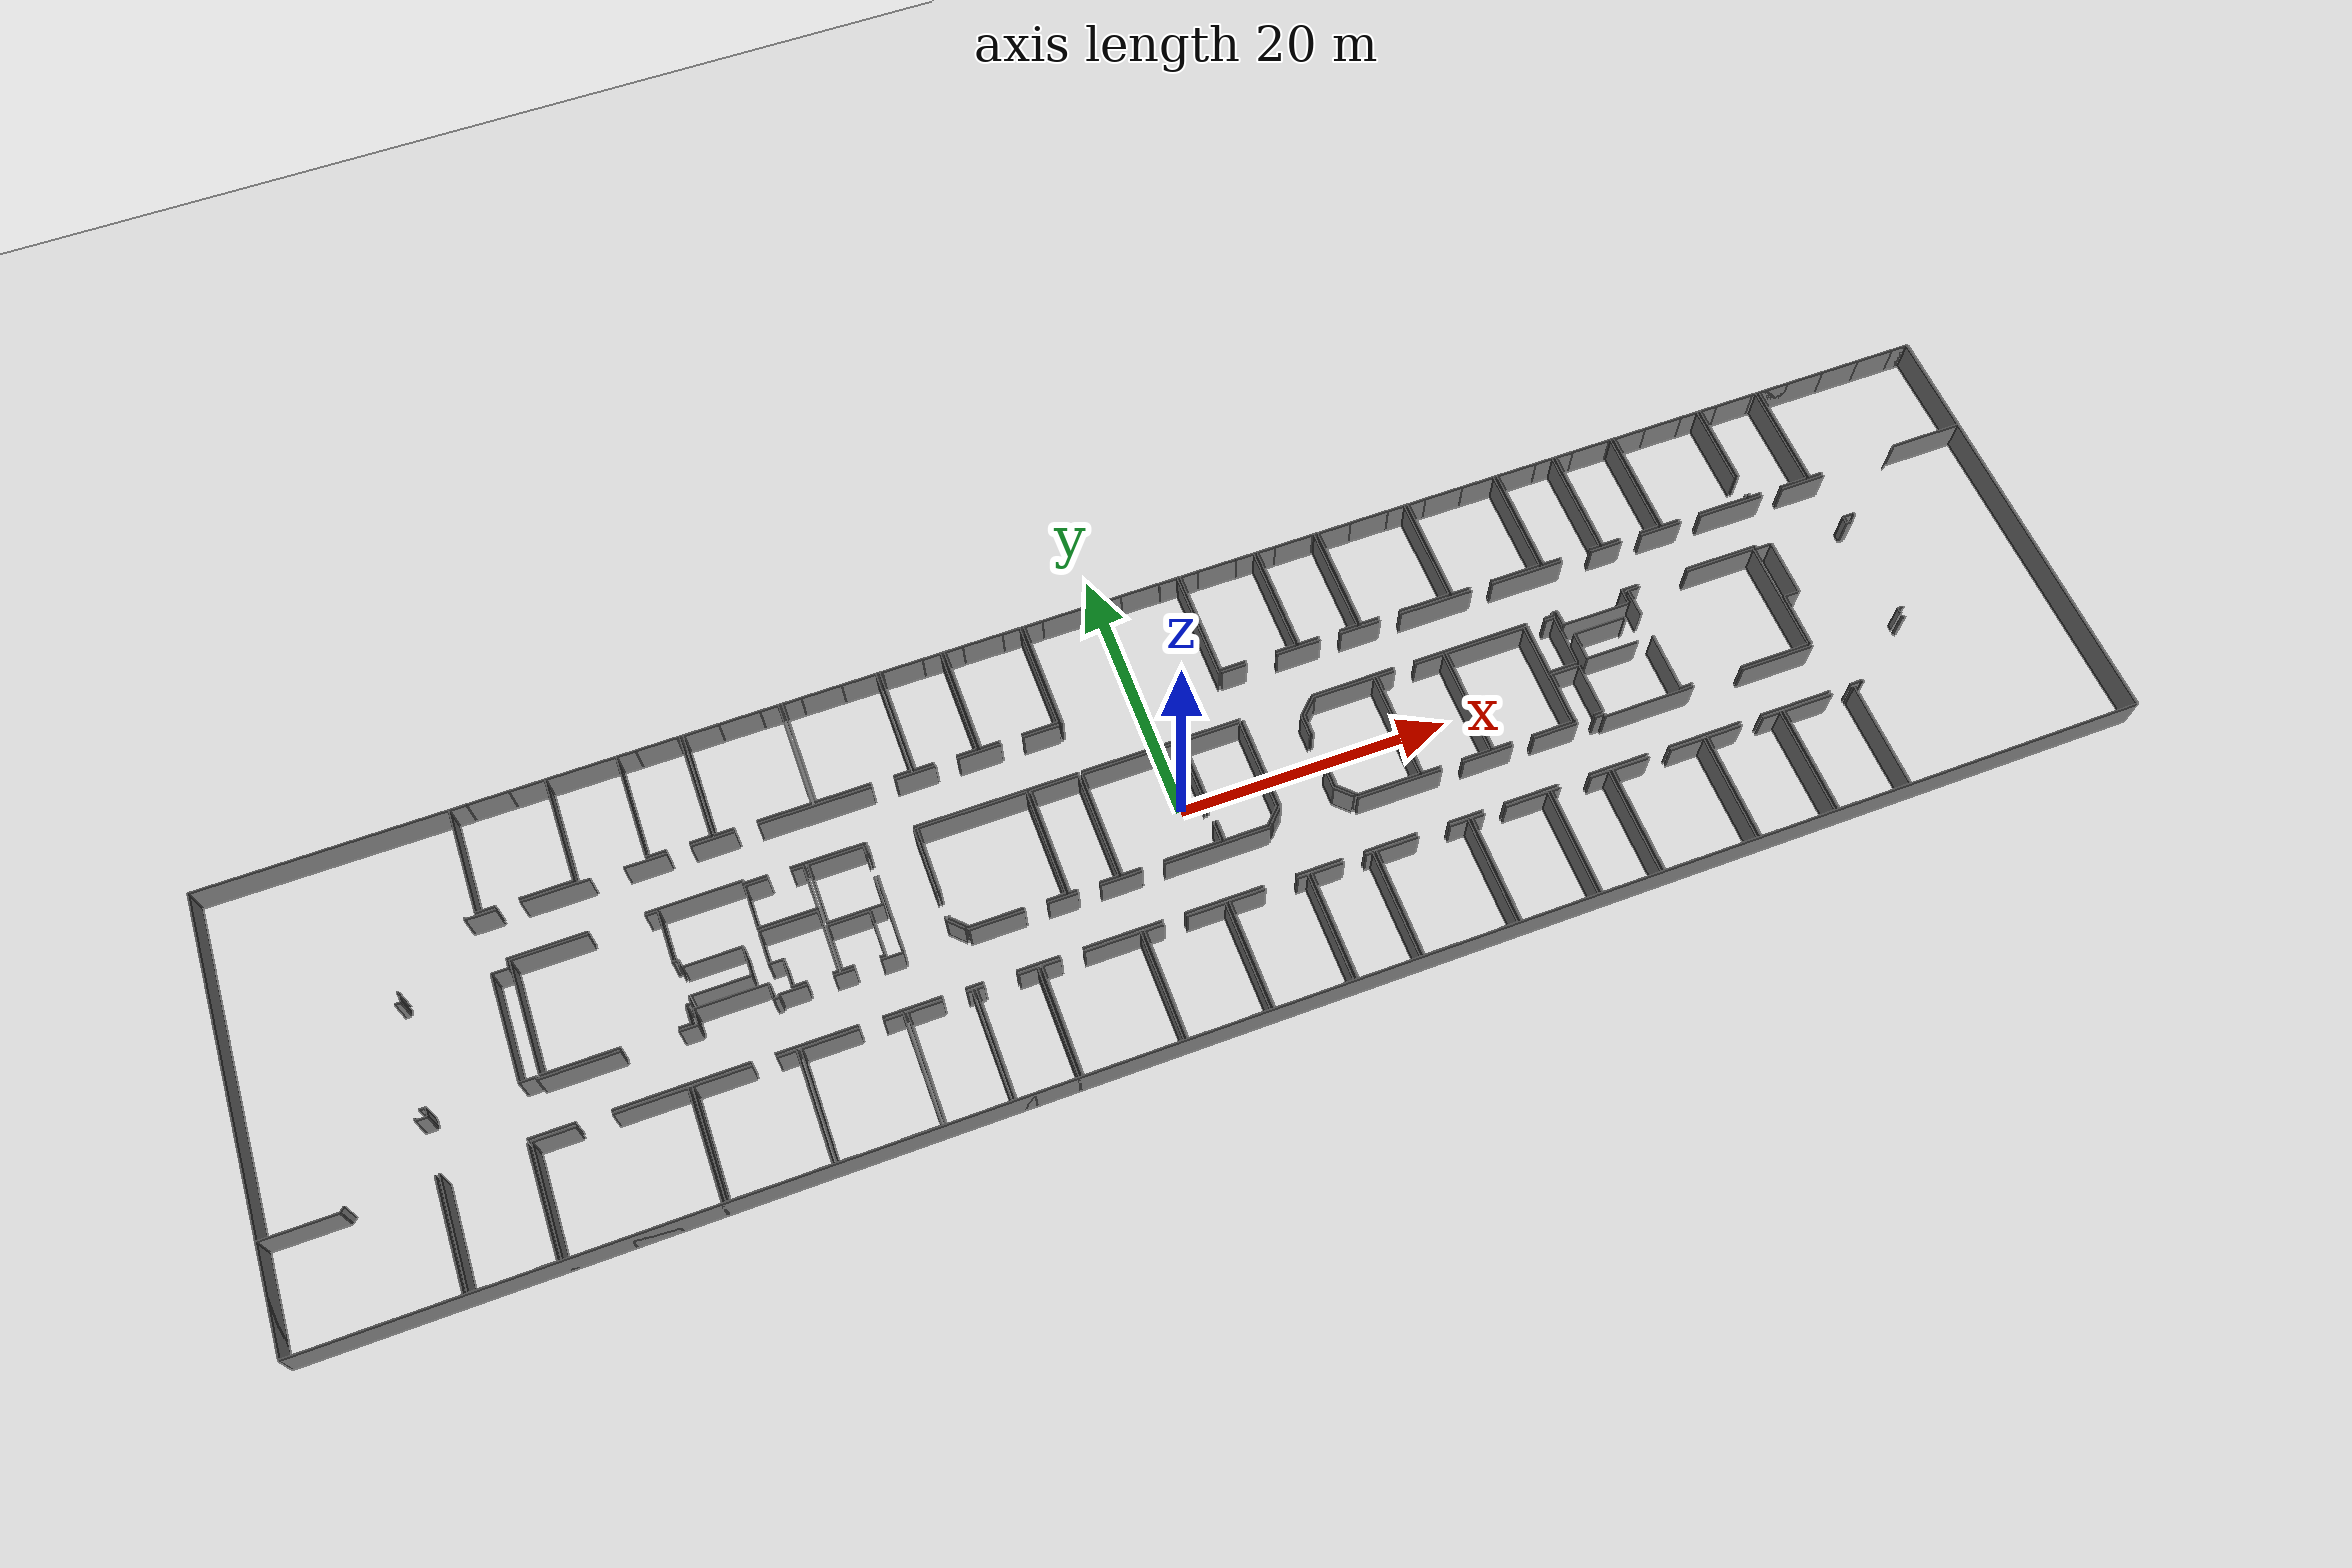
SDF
<sdf version="1.6">
  <world name="default">
    <light name="sun" type="directional">
      <cast_shadows>1</cast_shadows>
      <pose frame="">0 0 10 0 -0 0</pose>
      <diffuse>0.8 0.8 0.8 1</diffuse>
      <specular>0.1 0.1 0.1 1</specular>
      <attenuation>
        <range>1000</range>
        <constant>0.9</constant>
        <linear>0.01</linear>
        <quadratic>0.001</quadratic>
      </attenuation>
      <direction>-0.5 0.5 -1</direction>
    </light>
    <model name="ground_plane">
      <static>1</static>
      <link name="link">
        <collision name="collision">
          <geometry>
            <plane>
              <normal>0 0 1</normal>
              <size>100 100</size>
            </plane>
          </geometry>
          <surface>
            <friction>
              <ode>
                <mu>100</mu>
                <mu2>50</mu2>
              </ode>
              <torsional>
                <ode />
              </torsional>
            </friction>
            <contact>
              <ode />
            </contact>
            <bounce />
          </surface>
          <max_contacts>10</max_contacts>
        </collision>
        <visual name="visual">
          <cast_shadows>0</cast_shadows>
          <geometry>
            <plane>
              <normal>0 0 1</normal>
              <size>100 100</size>
            </plane>
          </geometry>
          <material>
            <script>
              <uri>file://media/materials/scripts/gazebo.material</uri>
              <name>Gazebo/Grey</name>
            </script>
          </material>
        </visual>
        <self_collide>0</self_collide>
        <kinematic>0</kinematic>
        <gravity>1</gravity>
      </link>
    </model>
    <gravity>0 0 -9.8</gravity>
    <magnetic_field>6e-06 2.3e-05 -4.2e-05</magnetic_field>
    <atmosphere type="adiabatic" />
    <physics default="0" name="default_physics" type="ode">
      <max_step_size>0.001</max_step_size>
      <real_time_factor>1</real_time_factor>
      <real_time_update_rate>1000</real_time_update_rate>
    </physics>
    <scene>
      <ambient>0.4 0.4 0.4 1</ambient>
      <background>0.7 0.7 0.7 1</background>
      <shadows>1</shadows>
    </scene>
    <spherical_coordinates>
      <surface_model>EARTH_WGS84</surface_model>
      <latitude_deg>0</latitude_deg>
      <longitude_deg>0</longitude_deg>
      <elevation>0</elevation>
      <heading_deg>0</heading_deg>
    </spherical_coordinates>
  <model name="50041171">
		<static>1</static>
		<link name="Wall_0">
			<collision name="Wall_0_Collision">
				<geometry>
					<box>
						<size>2.7097945375 0.1 2.5</size>
					</box>
				</geometry>
				<pose frame="">1.35489726875 0 1.25 0 0 0</pose>
			</collision>
			<visual name="Wall_0_Visual">
				<pose frame="">1.35489726875 0 1.25 0 0 0</pose>
				<geometry>
					<box>
						<size>2.7097945375 0.1 2.5</size>
					</box>
				</geometry>
				<material>
					<script>
						<uri>file://media/materials/scripts/gazebo.material</uri>
						<name>Gazebo/Grey</name>
					</script>
					<ambient>1 1 1 1</ambient>
				</material>
			</visual>
			<pose frame="">59.5393120783 -8.49105346341 0 0 0 3.14159265359</pose>
		</link>
		<link name="Wall_1">
			<collision name="Wall_1_Collision">
				<geometry>
					<box>
						<size>3.16096149086 0.1 2.5</size>
					</box>
				</geometry>
				<pose frame="">1.58048074543 0 1.25 0 0 0</pose>
			</collision>
			<visual name="Wall_1_Visual">
				<pose frame="">1.58048074543 0 1.25 0 0 0</pose>
				<geometry>
					<box>
						<size>3.16096149086 0.1 2.5</size>
					</box>
				</geometry>
				<material>
					<script>
						<uri>file://media/materials/scripts/gazebo.material</uri>
						<name>Gazebo/Grey</name>
					</script>
					<ambient>1 1 1 1</ambient>
				</material>
			</visual>
			<pose frame="">55.1907684691 -8.49105346341 0 0 0 3.14159265359</pose>
		</link>
		<link name="Wall_2">
			<collision name="Wall_2_Collision">
				<geometry>
					<box>
						<size>2.95302354218 0.1 2.5</size>
					</box>
				</geometry>
				<pose frame="">1.47651177109 0 1.25 0 0 0</pose>
			</collision>
			<visual name="Wall_2_Visual">
				<pose frame="">1.47651177109 0 1.25 0 0 0</pose>
				<geometry>
					<box>
						<size>2.95302354218 0.1 2.5</size>
					</box>
				</geometry>
				<material>
					<script>
						<uri>file://media/materials/scripts/gazebo.material</uri>
						<name>Gazebo/Grey</name>
					</script>
					<ambient>1 1 1 1</ambient>
				</material>
			</visual>
			<pose frame="">50.3991824662 -8.49105346341 0 0 0 3.14159265359</pose>
		</link>
		<link name="Wall_3">
			<collision name="Wall_3_Collision">
				<geometry>
					<box>
						<size>8.16822916336 0.1 2.5</size>
					</box>
				</geometry>
				<pose frame="">4.08411458168 0 1.25 0 0 0</pose>
			</collision>
			<visual name="Wall_3_Visual">
				<pose frame="">4.08411458168 0 1.25 0 0 0</pose>
				<geometry>
					<box>
						<size>8.16822916336 0.1 2.5</size>
					</box>
				</geometry>
				<material>
					<script>
						<uri>file://media/materials/scripts/gazebo.material</uri>
						<name>Gazebo/Grey</name>
					</script>
					<ambient>1 1 1 1</ambient>
				</material>
			</visual>
			<pose frame="">45.7487606873 -8.49105346341 0 0 0 3.14159265359</pose>
		</link>
		<link name="Wall_4">
			<collision name="Wall_4_Collision">
				<geometry>
					<box>
						<size>3.16096149086 0.1 2.5</size>
					</box>
				</geometry>
				<pose frame="">1.58048074543 0 1.25 0 0 0</pose>
			</collision>
			<visual name="Wall_4_Visual">
				<pose frame="">1.58048074543 0 1.25 0 0 0</pose>
				<geometry>
					<box>
						<size>3.16096149086 0.1 2.5</size>
					</box>
				</geometry>
				<material>
					<script>
						<uri>file://media/materials/scripts/gazebo.material</uri>
						<name>Gazebo/Grey</name>
					</script>
					<ambient>1 1 1 1</ambient>
				</material>
			</visual>
			<pose frame="">35.9584124103 -8.49105346341 0 0 0 3.14159265359</pose>
		</link>
		<link name="Wall_5">
			<collision name="Wall_5_Collision">
				<geometry>
					<box>
						<size>3.03401524624 0.1 2.5</size>
					</box>
				</geometry>
				<pose frame="">1.51700762312 0 1.25 0 0 0</pose>
			</collision>
			<visual name="Wall_5_Visual">
				<pose frame="">1.51700762312 0 1.25 0 0 0</pose>
				<geometry>
					<box>
						<size>3.03401524624 0.1 2.5</size>
					</box>
				</geometry>
				<material>
					<script>
						<uri>file://media/materials/scripts/gazebo.material</uri>
						<name>Gazebo/Grey</name>
					</script>
					<ambient>1 1 1 1</ambient>
				</material>
			</visual>
			<pose frame="">31.1598443639 -8.49105346341 0 0 0 3.14159265359</pose>
		</link>
		<link name="Wall_6">
			<collision name="Wall_6_Collision">
				<geometry>
					<box>
						<size>4.83500161856 0.1 2.5</size>
					</box>
				</geometry>
				<pose frame="">2.41750080928 0 1.25 0 0 0</pose>
			</collision>
			<visual name="Wall_6_Visual">
				<pose frame="">2.41750080928 0 1.25 0 0 0</pose>
				<geometry>
					<box>
						<size>4.83500161856 0.1 2.5</size>
					</box>
				</geometry>
				<material>
					<script>
						<uri>file://media/materials/scripts/gazebo.material</uri>
						<name>Gazebo/Grey</name>
					</script>
					<ambient>1 1 1 1</ambient>
				</material>
			</visual>
			<pose frame="">25.7751655062 -8.49105346341 0 0 0 3.14159265359</pose>
		</link>
		<link name="Wall_7">
			<collision name="Wall_7_Collision">
				<geometry>
					<box>
						<size>2.14475680273 0.1 2.5</size>
					</box>
				</geometry>
				<pose frame="">1.07237840137 0 1.25 0 0 0</pose>
			</collision>
			<visual name="Wall_7_Visual">
				<pose frame="">1.07237840137 0 1.25 0 0 0</pose>
				<geometry>
					<box>
						<size>2.14475680273 0.1 2.5</size>
					</box>
				</geometry>
				<material>
					<script>
						<uri>file://media/materials/scripts/gazebo.material</uri>
						<name>Gazebo/Grey</name>
					</script>
					<ambient>1 1 1 1</ambient>
				</material>
			</visual>
			<pose frame="">19.2976064286 -8.49105346341 0 0 0 3.14159265359</pose>
		</link>
		<link name="Wall_8">
			<collision name="Wall_8_Collision">
				<geometry>
					<box>
						<size>0.158555859521 0.1 2.5</size>
					</box>
				</geometry>
				<pose frame="">0.0792779297606 0 1.25 0 0 0</pose>
			</collision>
			<visual name="Wall_8_Visual">
				<pose frame="">0.0792779297606 0 1.25 0 0 0</pose>
				<geometry>
					<box>
						<size>0.158555859521 0.1 2.5</size>
					</box>
				</geometry>
				<material>
					<script>
						<uri>file://media/materials/scripts/gazebo.material</uri>
						<name>Gazebo/Grey</name>
					</script>
					<ambient>1 1 1 1</ambient>
				</material>
			</visual>
			<pose frame="">17.1528496258 -8.49105346341 0 0 0 1.57079632679</pose>
		</link>
		<link name="Wall_9">
			<collision name="Wall_9_Collision">
				<geometry>
					<box>
						<size>0.174634712345 0.1 2.5</size>
					</box>
				</geometry>
				<pose frame="">0.0873173561724 0 1.25 0 0 0</pose>
			</collision>
			<visual name="Wall_9_Visual">
				<pose frame="">0.0873173561724 0 1.25 0 0 0</pose>
				<geometry>
					<box>
						<size>0.174634712345 0.1 2.5</size>
					</box>
				</geometry>
				<material>
					<script>
						<uri>file://media/materials/scripts/gazebo.material</uri>
						<name>Gazebo/Grey</name>
					</script>
					<ambient>1 1 1 1</ambient>
				</material>
			</visual>
			<pose frame="">11.7778186827 -12.0637016255 0 0 0 -0.807502531758</pose>
		</link>
		<link name="Wall_10">
			<collision name="Wall_10_Collision">
				<geometry>
					<box>
						<size>0.0660120471986 0.1 2.5</size>
					</box>
				</geometry>
				<pose frame="">0.0330060235993 0 1.25 0 0 0</pose>
			</collision>
			<visual name="Wall_10_Visual">
				<pose frame="">0.0330060235993 0 1.25 0 0 0</pose>
				<geometry>
					<box>
						<size>0.0660120471986 0.1 2.5</size>
					</box>
				</geometry>
				<material>
					<script>
						<uri>file://media/materials/scripts/gazebo.material</uri>
						<name>Gazebo/Grey</name>
					</script>
					<ambient>1 1 1 1</ambient>
				</material>
			</visual>
			<pose frame="">11.8985445613 -12.1898861927 0 0 0 -1.57079632679</pose>
		</link>
		<link name="Wall_11">
			<collision name="Wall_11_Collision">
				<geometry>
					<box>
						<size>5.60911981821 0.1 2.5</size>
					</box>
				</geometry>
				<pose frame="">2.80455990911 0 1.25 0 0 0</pose>
			</collision>
			<visual name="Wall_11_Visual">
				<pose frame="">2.80455990911 0 1.25 0 0 0</pose>
				<geometry>
					<box>
						<size>5.60911981821 0.1 2.5</size>
					</box>
				</geometry>
				<material>
					<script>
						<uri>file://media/materials/scripts/gazebo.material</uri>
						<name>Gazebo/Grey</name>
					</script>
					<ambient>1 1 1 1</ambient>
				</material>
			</visual>
			<pose frame="">19.1014744806 -12.2558982399 0 0 0 0.0</pose>
		</link>
		<link name="Wall_12">
			<collision name="Wall_12_Collision">
				<geometry>
					<box>
						<size>6.82209118549 0.1 2.5</size>
					</box>
				</geometry>
				<pose frame="">3.41104559274 0 1.25 0 0 0</pose>
			</collision>
			<visual name="Wall_12_Visual">
				<pose frame="">3.41104559274 0 1.25 0 0 0</pose>
				<geometry>
					<box>
						<size>6.82209118549 0.1 2.5</size>
					</box>
				</geometry>
				<material>
					<script>
						<uri>file://media/materials/scripts/gazebo.material</uri>
						<name>Gazebo/Grey</name>
					</script>
					<ambient>1 1 1 1</ambient>
				</material>
			</visual>
			<pose frame="">28.6230775578 -12.2558982399 0 0 0 0.0</pose>
		</link>
		<link name="Wall_13">
			<collision name="Wall_13_Collision">
				<geometry>
					<box>
						<size>0.196005001682 0.1 2.5</size>
					</box>
				</geometry>
				<pose frame="">0.098002500841 0 1.25 0 0 0</pose>
			</collision>
			<visual name="Wall_13_Visual">
				<pose frame="">0.098002500841 0 1.25 0 0 0</pose>
				<geometry>
					<box>
						<size>0.196005001682 0.1 2.5</size>
					</box>
				</geometry>
				<material>
					<script>
						<uri>file://media/materials/scripts/gazebo.material</uri>
						<name>Gazebo/Grey</name>
					</script>
					<ambient>1 1 1 1</ambient>
				</material>
			</visual>
			<pose frame="">35.4451687433 -12.2558982399 0 0 0 -1.57079632679</pose>
		</link>
		<link name="Wall_14">
			<collision name="Wall_14_Collision">
				<geometry>
					<box>
						<size>1.67112036408 0.1 2.5</size>
					</box>
				</geometry>
				<pose frame="">0.835560182041 0 1.25 0 0 0</pose>
			</collision>
			<visual name="Wall_14_Visual">
				<pose frame="">0.835560182041 0 1.25 0 0 0</pose>
				<geometry>
					<box>
						<size>1.67112036408 0.1 2.5</size>
					</box>
				</geometry>
				<material>
					<script>
						<uri>file://media/materials/scripts/gazebo.material</uri>
						<name>Gazebo/Grey</name>
					</script>
					<ambient>1 1 1 1</ambient>
				</material>
			</visual>
			<pose frame="">35.4451687433 -12.4519032416 0 0 0 0.0</pose>
		</link>
		<link name="Wall_15">
			<collision name="Wall_15_Collision">
				<geometry>
					<box>
						<size>5.40740223552 0.1 2.5</size>
					</box>
				</geometry>
				<pose frame="">2.70370111776 0 1.25 0 0 0</pose>
			</collision>
			<visual name="Wall_15_Visual">
				<pose frame="">2.70370111776 0 1.25 0 0 0</pose>
				<geometry>
					<box>
						<size>5.40740223552 0.1 2.5</size>
					</box>
				</geometry>
				<material>
					<script>
						<uri>file://media/materials/scripts/gazebo.material</uri>
						<name>Gazebo/Grey</name>
					</script>
					<ambient>1 1 1 1</ambient>
				</material>
			</visual>
			<pose frame="">38.7348537262 -12.4519032416 0 0 0 0.0</pose>
		</link>
		<link name="Wall_16">
			<collision name="Wall_16_Collision">
				<geometry>
					<box>
						<size>12.0161724886 0.1 2.5</size>
					</box>
				</geometry>
				<pose frame="">6.00808624431 0 1.25 0 0 0</pose>
			</collision>
			<visual name="Wall_16_Visual">
				<pose frame="">6.00808624431 0 1.25 0 0 0</pose>
				<geometry>
					<box>
						<size>12.0161724886 0.1 2.5</size>
					</box>
				</geometry>
				<material>
					<script>
						<uri>file://media/materials/scripts/gazebo.material</uri>
						<name>Gazebo/Grey</name>
					</script>
					<ambient>1 1 1 1</ambient>
				</material>
			</visual>
			<pose frame="">47.5232152945 -12.4519032416 0 0 0 -0.00354971833229</pose>
		</link>
		<link name="Wall_17">
			<collision name="Wall_17_Collision">
				<geometry>
					<box>
						<size>3.74631062477 0.1 2.5</size>
					</box>
				</geometry>
				<pose frame="">1.87315531238 0 1.25 0 0 0</pose>
			</collision>
			<visual name="Wall_17_Visual">
				<pose frame="">1.87315531238 0 1.25 0 0 0</pose>
				<geometry>
					<box>
						<size>3.74631062477 0.1 2.5</size>
					</box>
				</geometry>
				<material>
					<script>
						<uri>file://media/materials/scripts/gazebo.material</uri>
						<name>Gazebo/Grey</name>
					</script>
					<ambient>1 1 1 1</ambient>
				</material>
			</visual>
			<pose frame="">24.6860936736 -8.23017893073 0 0 0 3.14159265359</pose>
		</link>
		<link name="Wall_18">
			<collision name="Wall_18_Collision">
				<geometry>
					<box>
						<size>1.37444699042 0.1 2.5</size>
					</box>
				</geometry>
				<pose frame="">0.687223495211 0 1.25 0 0 0</pose>
			</collision>
			<visual name="Wall_18_Visual">
				<pose frame="">0.687223495211 0 1.25 0 0 0</pose>
				<geometry>
					<box>
						<size>1.37444699042 0.1 2.5</size>
					</box>
				</geometry>
				<material>
					<script>
						<uri>file://media/materials/scripts/gazebo.material</uri>
						<name>Gazebo/Grey</name>
					</script>
					<ambient>1 1 1 1</ambient>
				</material>
			</visual>
			<pose frame="">19.2929094175 -8.23017893073 0 0 0 3.14159265359</pose>
		</link>
		<link name="Wall_19">
			<collision name="Wall_19_Collision">
				<geometry>
					<box>
						<size>8.21342202644 0.1 2.5</size>
					</box>
				</geometry>
				<pose frame="">4.10671101322 0 1.25 0 0 0</pose>
			</collision>
			<visual name="Wall_19_Visual">
				<pose frame="">4.10671101322 0 1.25 0 0 0</pose>
				<geometry>
					<box>
						<size>8.21342202644 0.1 2.5</size>
					</box>
				</geometry>
				<material>
					<script>
						<uri>file://media/materials/scripts/gazebo.material</uri>
						<name>Gazebo/Grey</name>
					</script>
					<ambient>1 1 1 1</ambient>
				</material>
			</visual>
			<pose frame="">17.9184624271 -8.23017893073 0 0 0 1.57079632679</pose>
		</link>
		<link name="Wall_20">
			<collision name="Wall_20_Collision">
				<geometry>
					<box>
						<size>1.22541209925 0.1 2.5</size>
					</box>
				</geometry>
				<pose frame="">0.612706049623 0 1.25 0 0 0</pose>
			</collision>
			<visual name="Wall_20_Visual">
				<pose frame="">0.612706049623 0 1.25 0 0 0</pose>
				<geometry>
					<box>
						<size>1.22541209925 0.1 2.5</size>
					</box>
				</geometry>
				<material>
					<script>
						<uri>file://media/materials/scripts/gazebo.material</uri>
						<name>Gazebo/Grey</name>
					</script>
					<ambient>1 1 1 1</ambient>
				</material>
			</visual>
			<pose frame="">17.9184624271 -0.0167569042889 0 0 0 0.0</pose>
		</link>
		<link name="Wall_21">
			<collision name="Wall_21_Collision">
				<geometry>
					<box>
						<size>2.57624708817 0.1 2.5</size>
					</box>
				</geometry>
				<pose frame="">1.28812354409 0 1.25 0 0 0</pose>
			</collision>
			<visual name="Wall_21_Visual">
				<pose frame="">1.28812354409 0 1.25 0 0 0</pose>
				<geometry>
					<box>
						<size>2.57624708817 0.1 2.5</size>
					</box>
				</geometry>
				<material>
					<script>
						<uri>file://media/materials/scripts/gazebo.material</uri>
						<name>Gazebo/Grey</name>
					</script>
					<ambient>1 1 1 1</ambient>
				</material>
			</visual>
			<pose frame="">22.1060381981 -0.0167569042889 0 0 0 0.0</pose>
		</link>
		<link name="Wall_22">
			<collision name="Wall_22_Collision">
				<geometry>
					<box>
						<size>8.21342290938 0.1 2.5</size>
					</box>
				</geometry>
				<pose frame="">4.10671145469 0 1.25 0 0 0</pose>
			</collision>
			<visual name="Wall_22_Visual">
				<pose frame="">4.10671145469 0 1.25 0 0 0</pose>
				<geometry>
					<box>
						<size>8.21342290938 0.1 2.5</size>
					</box>
				</geometry>
				<material>
					<script>
						<uri>file://media/materials/scripts/gazebo.material</uri>
						<name>Gazebo/Grey</name>
					</script>
					<ambient>1 1 1 1</ambient>
				</material>
			</visual>
			<pose frame="">24.6822852863 -0.0167569042889 0 0 0 -1.57033264831</pose>
		</link>
		<link name="Wall_23">
			<collision name="Wall_23_Collision">
				<geometry>
					<box>
						<size>0.837083536976 0.1 2.5</size>
					</box>
				</geometry>
				<pose frame="">0.418541768488 0 1.25 0 0 0</pose>
			</collision>
			<visual name="Wall_23_Visual">
				<pose frame="">0.418541768488 0 1.25 0 0 0</pose>
				<geometry>
					<box>
						<size>0.837083536976 0.1 2.5</size>
					</box>
				</geometry>
				<material>
					<script>
						<uri>file://media/materials/scripts/gazebo.material</uri>
						<name>Gazebo/Grey</name>
					</script>
					<ambient>1 1 1 1</ambient>
				</material>
			</visual>
			<pose frame="">29.4874545374 -21.0527652066 0 0 0 3.14159265359</pose>
		</link>
		<link name="Wall_24">
			<collision name="Wall_24_Collision">
				<geometry>
					<box>
						<size>5.40003935334 0.1 2.5</size>
					</box>
				</geometry>
				<pose frame="">2.70001967667 0 1.25 0 0 0</pose>
			</collision>
			<visual name="Wall_24_Visual">
				<pose frame="">2.70001967667 0 1.25 0 0 0</pose>
				<geometry>
					<box>
						<size>5.40003935334 0.1 2.5</size>
					</box>
				</geometry>
				<material>
					<script>
						<uri>file://media/materials/scripts/gazebo.material</uri>
						<name>Gazebo/Grey</name>
					</script>
					<ambient>1 1 1 1</ambient>
				</material>
			</visual>
			<pose frame="">24.7119907075 -21.0527652066 0 0 0 3.14159265359</pose>
		</link>
		<link name="Wall_25">
			<collision name="Wall_25_Collision">
				<geometry>
					<box>
						<size>8.60809790094 0.1 2.5</size>
					</box>
				</geometry>
				<pose frame="">4.30404895047 0 1.25 0 0 0</pose>
			</collision>
			<visual name="Wall_25_Visual">
				<pose frame="">4.30404895047 0 1.25 0 0 0</pose>
				<geometry>
					<box>
						<size>8.60809790094 0.1 2.5</size>
					</box>
				</geometry>
				<material>
					<script>
						<uri>file://media/materials/scripts/gazebo.material</uri>
						<name>Gazebo/Grey</name>
					</script>
					<ambient>1 1 1 1</ambient>
				</material>
			</visual>
			<pose frame="">19.3119513542 -21.0527652066 0 0 0 1.57079632679</pose>
		</link>
		<link name="Wall_26">
			<collision name="Wall_26_Collision">
				<geometry>
					<box>
						<size>5.38556748145 0.1 2.5</size>
					</box>
				</geometry>
				<pose frame="">2.69278374072 0 1.25 0 0 0</pose>
			</collision>
			<visual name="Wall_26_Visual">
				<pose frame="">2.69278374072 0 1.25 0 0 0</pose>
				<geometry>
					<box>
						<size>5.38556748145 0.1 2.5</size>
					</box>
				</geometry>
				<material>
					<script>
						<uri>file://media/materials/scripts/gazebo.material</uri>
						<name>Gazebo/Grey</name>
					</script>
					<ambient>1 1 1 1</ambient>
				</material>
			</visual>
			<pose frame="">19.3119513542 -12.4446673056 0 0 0 0.0</pose>
		</link>
		<link name="Wall_27">
			<collision name="Wall_27_Collision">
				<geometry>
					<box>
						<size>0.876436872806 0.1 2.5</size>
					</box>
				</geometry>
				<pose frame="">0.438218436403 0 1.25 0 0 0</pose>
			</collision>
			<visual name="Wall_27_Visual">
				<pose frame="">0.438218436403 0 1.25 0 0 0</pose>
				<geometry>
					<box>
						<size>0.876436872806 0.1 2.5</size>
					</box>
				</geometry>
				<material>
					<script>
						<uri>file://media/materials/scripts/gazebo.material</uri>
						<name>Gazebo/Grey</name>
					</script>
					<ambient>1 1 1 1</ambient>
				</material>
			</visual>
			<pose frame="">28.6086056859 -12.4446673056 0 0 0 0.0</pose>
		</link>
		<link name="Wall_28">
			<collision name="Wall_28_Collision">
				<geometry>
					<box>
						<size>3.95094797108 0.1 2.5</size>
					</box>
				</geometry>
				<pose frame="">1.97547398554 0 1.25 0 0 0</pose>
			</collision>
			<visual name="Wall_28_Visual">
				<pose frame="">1.97547398554 0 1.25 0 0 0</pose>
				<geometry>
					<box>
						<size>3.95094797108 0.1 2.5</size>
					</box>
				</geometry>
				<material>
					<script>
						<uri>file://media/materials/scripts/gazebo.material</uri>
						<name>Gazebo/Grey</name>
					</script>
					<ambient>1 1 1 1</ambient>
				</material>
			</visual>
			<pose frame="">29.4850425587 -12.4446673056 0 0 0 -1.57079632679</pose>
		</link>
		<link name="Wall_29">
			<collision name="Wall_29_Collision">
				<geometry>
					<box>
						<size>0.367255485665 0.1 2.5</size>
					</box>
				</geometry>
				<pose frame="">0.183627742832 0 1.25 0 0 0</pose>
			</collision>
			<visual name="Wall_29_Visual">
				<pose frame="">0.183627742832 0 1.25 0 0 0</pose>
				<geometry>
					<box>
						<size>0.367255485665 0.1 2.5</size>
					</box>
				</geometry>
				<material>
					<script>
						<uri>file://media/materials/scripts/gazebo.material</uri>
						<name>Gazebo/Grey</name>
					</script>
					<ambient>1 1 1 1</ambient>
				</material>
			</visual>
			<pose frame="">29.4850425587 -16.3956152767 0 0 0 0.0</pose>
		</link>
		<link name="Wall_30">
			<collision name="Wall_30_Collision">
				<geometry>
					<box>
						<size>0.517559839286 0.1 2.5</size>
					</box>
				</geometry>
				<pose frame="">0.258779919643 0 1.25 0 0 0</pose>
			</collision>
			<visual name="Wall_30_Visual">
				<pose frame="">0.258779919643 0 1.25 0 0 0</pose>
				<geometry>
					<box>
						<size>0.517559839286 0.1 2.5</size>
					</box>
				</geometry>
				<material>
					<script>
						<uri>file://media/materials/scripts/gazebo.material</uri>
						<name>Gazebo/Grey</name>
					</script>
					<ambient>1 1 1 1</ambient>
				</material>
			</visual>
			<pose frame="">29.8522980444 -16.3956152767 0 0 0 -1.57079632679</pose>
		</link>
		<link name="Wall_31">
			<collision name="Wall_31_Collision">
				<geometry>
					<box>
						<size>0.555389820181 0.1 2.5</size>
					</box>
				</geometry>
				<pose frame="">0.27769491009 0 1.25 0 0 0</pose>
			</collision>
			<visual name="Wall_31_Visual">
				<pose frame="">0.27769491009 0 1.25 0 0 0</pose>
				<geometry>
					<box>
						<size>0.555389820181 0.1 2.5</size>
					</box>
				</geometry>
				<material>
					<script>
						<uri>file://media/materials/scripts/gazebo.material</uri>
						<name>Gazebo/Grey</name>
					</script>
					<ambient>1 1 1 1</ambient>
				</material>
			</visual>
			<pose frame="">29.8522980444 -19.1174697075 0 0 0 -1.57079632679</pose>
		</link>
		<link name="Wall_32">
			<collision name="Wall_32_Collision">
				<geometry>
					<box>
						<size>0.356845893606 0.1 2.5</size>
					</box>
				</geometry>
				<pose frame="">0.178422946803 0 1.25 0 0 0</pose>
			</collision>
			<visual name="Wall_32_Visual">
				<pose frame="">0.178422946803 0 1.25 0 0 0</pose>
				<geometry>
					<box>
						<size>0.356845893606 0.1 2.5</size>
					</box>
				</geometry>
				<material>
					<script>
						<uri>file://media/materials/scripts/gazebo.material</uri>
						<name>Gazebo/Grey</name>
					</script>
					<ambient>1 1 1 1</ambient>
				</material>
			</visual>
			<pose frame="">29.8522980444 -19.6728595276 0 0 0 3.14159265359</pose>
		</link>
		<link name="Wall_33">
			<collision name="Wall_33_Collision">
				<geometry>
					<box>
						<size>1.3799288549 0.1 2.5</size>
					</box>
				</geometry>
				<pose frame="">0.689964427451 0 1.25 0 0 0</pose>
			</collision>
			<visual name="Wall_33_Visual">
				<pose frame="">0.689964427451 0 1.25 0 0 0</pose>
				<geometry>
					<box>
						<size>1.3799288549 0.1 2.5</size>
					</box>
				</geometry>
				<material>
					<script>
						<uri>file://media/materials/scripts/gazebo.material</uri>
						<name>Gazebo/Grey</name>
					</script>
					<ambient>1 1 1 1</ambient>
				</material>
			</visual>
			<pose frame="">29.4954521508 -19.6728595276 0 0 0 -1.57659203007</pose>
		</link>
		<link name="Wall_34">
			<collision name="Wall_34_Collision">
				<geometry>
					<box>
						<size>1.50126628879 0.1 2.5</size>
					</box>
				</geometry>
				<pose frame="">0.750633144395 0 1.25 0 0 0</pose>
			</collision>
			<visual name="Wall_34_Visual">
				<pose frame="">0.750633144395 0 1.25 0 0 0</pose>
				<geometry>
					<box>
						<size>1.50126628879 0.1 2.5</size>
					</box>
				</geometry>
				<material>
					<script>
						<uri>file://media/materials/scripts/gazebo.material</uri>
						<name>Gazebo/Grey</name>
					</script>
					<ambient>1 1 1 1</ambient>
				</material>
			</visual>
			<pose frame="">34.3062070366 -8.22852862955 0 0 0 3.14159265359</pose>
		</link>
		<link name="Wall_35">
			<collision name="Wall_35_Collision">
				<geometry>
					<box>
						<size>1.40224821799 0.1 2.5</size>
					</box>
				</geometry>
				<pose frame="">0.701124108996 0 1.25 0 0 0</pose>
			</collision>
			<visual name="Wall_35_Visual">
				<pose frame="">0.701124108996 0 1.25 0 0 0</pose>
				<geometry>
					<box>
						<size>1.40224821799 0.1 2.5</size>
					</box>
				</geometry>
				<material>
					<script>
						<uri>file://media/materials/scripts/gazebo.material</uri>
						<name>Gazebo/Grey</name>
					</script>
					<ambient>1 1 1 1</ambient>
				</material>
			</visual>
			<pose frame="">31.1460072232 -8.22852862955 0 0 0 3.14159265359</pose>
		</link>
		<link name="Wall_36">
			<collision name="Wall_36_Collision">
				<geometry>
					<box>
						<size>8.22319688728 0.1 2.5</size>
					</box>
				</geometry>
				<pose frame="">4.11159844364 0 1.25 0 0 0</pose>
			</collision>
			<visual name="Wall_36_Visual">
				<pose frame="">4.11159844364 0 1.25 0 0 0</pose>
				<geometry>
					<box>
						<size>8.22319688728 0.1 2.5</size>
					</box>
				</geometry>
				<material>
					<script>
						<uri>file://media/materials/scripts/gazebo.material</uri>
						<name>Gazebo/Grey</name>
					</script>
					<ambient>1 1 1 1</ambient>
				</material>
			</visual>
			<pose frame="">29.7437590052 -8.22852862955 0 0 0 1.57079632679</pose>
		</link>
		<link name="Wall_37">
			<collision name="Wall_37_Collision">
				<geometry>
					<box>
						<size>1.38396795877 0.1 2.5</size>
					</box>
				</geometry>
				<pose frame="">0.691983979384 0 1.25 0 0 0</pose>
			</collision>
			<visual name="Wall_37_Visual">
				<pose frame="">0.691983979384 0 1.25 0 0 0</pose>
				<geometry>
					<box>
						<size>1.38396795877 0.1 2.5</size>
					</box>
				</geometry>
				<material>
					<script>
						<uri>file://media/materials/scripts/gazebo.material</uri>
						<name>Gazebo/Grey</name>
					</script>
					<ambient>1 1 1 1</ambient>
				</material>
			</visual>
			<pose frame="">29.7437590052 -0.00533174227373 0 0 0 0.0</pose>
		</link>
		<link name="Wall_38">
			<collision name="Wall_38_Collision">
				<geometry>
					<box>
						<size>0.190927151898 0.1 2.5</size>
					</box>
				</geometry>
				<pose frame="">0.0954635759488 0 1.25 0 0 0</pose>
			</collision>
			<visual name="Wall_38_Visual">
				<pose frame="">0.0954635759488 0 1.25 0 0 0</pose>
				<geometry>
					<box>
						<size>0.190927151898 0.1 2.5</size>
					</box>
				</geometry>
				<material>
					<script>
						<uri>file://media/materials/scripts/gazebo.material</uri>
						<name>Gazebo/Grey</name>
					</script>
					<ambient>1 1 1 1</ambient>
				</material>
			</visual>
			<pose frame="">34.0990307654 -0.00533174227373 0 0 0 0.0</pose>
		</link>
		<link name="Wall_39">
			<collision name="Wall_39_Collision">
				<geometry>
					<box>
						<size>8.22321294147 0.1 2.5</size>
					</box>
				</geometry>
				<pose frame="">4.11160647074 0 1.25 0 0 0</pose>
			</collision>
			<visual name="Wall_39_Visual">
				<pose frame="">4.11160647074 0 1.25 0 0 0</pose>
				<geometry>
					<box>
						<size>8.22321294147 0.1 2.5</size>
					</box>
				</geometry>
				<material>
					<script>
						<uri>file://media/materials/scripts/gazebo.material</uri>
						<name>Gazebo/Grey</name>
					</script>
					<ambient>1 1 1 1</ambient>
				</material>
			</visual>
			<pose frame="">34.2899579173 -0.00533174227373 0 0 0 -1.56882031936</pose>
		</link>
		<link name="Wall_40">
			<collision name="Wall_40_Collision">
				<geometry>
					<box>
						<size>3.90270839813 0.1 2.5</size>
					</box>
				</geometry>
				<pose frame="">1.95135419906 0 1.25 0 0 0</pose>
			</collision>
			<visual name="Wall_40_Visual">
				<pose frame="">1.95135419906 0 1.25 0 0 0</pose>
				<geometry>
					<box>
						<size>3.90270839813 0.1 2.5</size>
					</box>
				</geometry>
				<material>
					<script>
						<uri>file://media/materials/scripts/gazebo.material</uri>
						<name>Gazebo/Grey</name>
					</script>
					<ambient>1 1 1 1</ambient>
				</material>
			</visual>
			<pose frame="">41.4958076003 -8.24782445873 0 0 0 3.14159265359</pose>
		</link>
		<link name="Wall_41">
			<collision name="Wall_41_Collision">
				<geometry>
					<box>
						<size>1.40224821799 0.1 2.5</size>
					</box>
				</geometry>
				<pose frame="">0.701124108996 0 1.25 0 0 0</pose>
			</collision>
			<visual name="Wall_41_Visual">
				<pose frame="">0.701124108996 0 1.25 0 0 0</pose>
				<geometry>
					<box>
						<size>1.40224821799 0.1 2.5</size>
					</box>
				</geometry>
				<material>
					<script>
						<uri>file://media/materials/scripts/gazebo.material</uri>
						<name>Gazebo/Grey</name>
					</script>
					<ambient>1 1 1 1</ambient>
				</material>
			</visual>
			<pose frame="">35.9622207976 -8.24782445873 0 0 0 3.14159265359</pose>
		</link>
		<link name="Wall_42">
			<collision name="Wall_42_Collision">
				<geometry>
					<box>
						<size>8.22929030702 0.1 2.5</size>
					</box>
				</geometry>
				<pose frame="">4.11464515351 0 1.25 0 0 0</pose>
			</collision>
			<visual name="Wall_42_Visual">
				<pose frame="">4.11464515351 0 1.25 0 0 0</pose>
				<geometry>
					<box>
						<size>8.22929030702 0.1 2.5</size>
					</box>
				</geometry>
				<material>
					<script>
						<uri>file://media/materials/scripts/gazebo.material</uri>
						<name>Gazebo/Grey</name>
					</script>
					<ambient>1 1 1 1</ambient>
				</material>
			</visual>
			<pose frame="">34.5599725796 -8.24782445873 0 0 0 1.57079632679</pose>
		</link>
		<link name="Wall_43">
			<collision name="Wall_43_Collision">
				<geometry>
					<box>
						<size>2.55707820523 0.1 2.5</size>
					</box>
				</geometry>
				<pose frame="">1.27853910262 0 1.25 0 0 0</pose>
			</collision>
			<visual name="Wall_43_Visual">
				<pose frame="">1.27853910262 0 1.25 0 0 0</pose>
				<geometry>
					<box>
						<size>2.55707820523 0.1 2.5</size>
					</box>
				</geometry>
				<material>
					<script>
						<uri>file://media/materials/scripts/gazebo.material</uri>
						<name>Gazebo/Grey</name>
					</script>
					<ambient>1 1 1 1</ambient>
				</material>
			</visual>
			<pose frame="">34.5599725796 -0.0185341517135 0 0 0 0.0</pose>
		</link>
		<link name="Wall_44">
			<collision name="Wall_44_Collision">
				<geometry>
					<box>
						<size>1.37762064654 0.1 2.5</size>
					</box>
				</geometry>
				<pose frame="">0.688810323269 0 1.25 0 0 0</pose>
			</collision>
			<visual name="Wall_44_Visual">
				<pose frame="">0.688810323269 0 1.25 0 0 0</pose>
				<geometry>
					<box>
						<size>1.37762064654 0.1 2.5</size>
					</box>
				</geometry>
				<material>
					<script>
						<uri>file://media/materials/scripts/gazebo.material</uri>
						<name>Gazebo/Grey</name>
					</script>
					<ambient>1 1 1 1</ambient>
				</material>
			</visual>
			<pose frame="">40.1080312542 -0.0185341517135 0 0 0 0.0</pose>
		</link>
		<link name="Wall_45">
			<collision name="Wall_45_Collision">
				<geometry>
					<box>
						<size>8.22929657355 0.1 2.5</size>
					</box>
				</geometry>
				<pose frame="">4.11464828677 0 1.25 0 0 0</pose>
			</collision>
			<visual name="Wall_45_Visual">
				<pose frame="">4.11464828677 0 1.25 0 0 0</pose>
				<geometry>
					<box>
						<size>8.22929657355 0.1 2.5</size>
					</box>
				</geometry>
				<material>
					<script>
						<uri>file://media/materials/scripts/gazebo.material</uri>
						<name>Gazebo/Grey</name>
					</script>
					<ambient>1 1 1 1</ambient>
				</material>
			</visual>
			<pose frame="">41.4856519007 -0.0185341517135 0 0 0 -1.56956223564</pose>
		</link>
		<link name="Wall_46">
			<collision name="Wall_46_Collision">
				<geometry>
					<box>
						<size>1.24381930472 0.1 2.5</size>
					</box>
				</geometry>
				<pose frame="">0.621909652358 0 1.25 0 0 0</pose>
			</collision>
			<visual name="Wall_46_Visual">
				<pose frame="">0.621909652358 0 1.25 0 0 0</pose>
				<geometry>
					<box>
						<size>1.24381930472 0.1 2.5</size>
					</box>
				</geometry>
				<material>
					<script>
						<uri>file://media/materials/scripts/gazebo.material</uri>
						<name>Gazebo/Grey</name>
					</script>
					<ambient>1 1 1 1</ambient>
				</material>
			</visual>
			<pose frame="">48.6746177331 -8.22395856475 0 0 0 3.14159265359</pose>
		</link>
		<link name="Wall_47">
			<collision name="Wall_47_Collision">
				<geometry>
					<box>
						<size>3.99817197408 0.1 2.5</size>
					</box>
				</geometry>
				<pose frame="">1.99908598704 0 1.25 0 0 0</pose>
			</collision>
			<visual name="Wall_47_Visual">
				<pose frame="">1.99908598704 0 1.25 0 0 0</pose>
				<geometry>
					<box>
						<size>3.99817197408 0.1 2.5</size>
					</box>
				</geometry>
				<material>
					<script>
						<uri>file://media/materials/scripts/gazebo.material</uri>
						<name>Gazebo/Grey</name>
					</script>
					<ambient>1 1 1 1</ambient>
				</material>
			</visual>
			<pose frame="">45.7698337639 -8.22395856475 0 0 0 3.14159265359</pose>
		</link>
		<link name="Wall_48">
			<collision name="Wall_48_Collision">
				<geometry>
					<box>
						<size>8.21773819876 0.1 2.5</size>
					</box>
				</geometry>
				<pose frame="">4.10886909938 0 1.25 0 0 0</pose>
			</collision>
			<visual name="Wall_48_Visual">
				<pose frame="">4.10886909938 0 1.25 0 0 0</pose>
				<geometry>
					<box>
						<size>8.21773819876 0.1 2.5</size>
					</box>
				</geometry>
				<material>
					<script>
						<uri>file://media/materials/scripts/gazebo.material</uri>
						<name>Gazebo/Grey</name>
					</script>
					<ambient>1 1 1 1</ambient>
				</material>
			</visual>
			<pose frame="">41.7716617898 -8.22395856475 0 0 0 1.57079632679</pose>
		</link>
		<link name="Wall_49">
			<collision name="Wall_49_Collision">
				<geometry>
					<box>
						<size>1.35654756993 0.1 2.5</size>
					</box>
				</geometry>
				<pose frame="">0.678273784966 0 1.25 0 0 0</pose>
			</collision>
			<visual name="Wall_49_Visual">
				<pose frame="">0.678273784966 0 1.25 0 0 0</pose>
				<geometry>
					<box>
						<size>1.35654756993 0.1 2.5</size>
					</box>
				</geometry>
				<material>
					<script>
						<uri>file://media/materials/scripts/gazebo.material</uri>
						<name>Gazebo/Grey</name>
					</script>
					<ambient>1 1 1 1</ambient>
				</material>
			</visual>
			<pose frame="">41.7716617898 -0.00622036598602 0 0 0 0.0</pose>
		</link>
		<link name="Wall_50">
			<collision name="Wall_50_Collision">
				<geometry>
					<box>
						<size>2.5814518842 0.1 2.5</size>
					</box>
				</geometry>
				<pose frame="">1.2907259421 0 1.25 0 0 0</pose>
			</collision>
			<visual name="Wall_50_Visual">
				<pose frame="">1.2907259421 0 1.25 0 0 0</pose>
				<geometry>
					<box>
						<size>2.5814518842 0.1 2.5</size>
					</box>
				</geometry>
				<material>
					<script>
						<uri>file://media/materials/scripts/gazebo.material</uri>
						<name>Gazebo/Grey</name>
					</script>
					<ambient>1 1 1 1</ambient>
				</material>
			</visual>
			<pose frame="">46.1072568821 -0.00622036598602 0 0 0 0.0</pose>
		</link>
		<link name="Wall_51">
			<collision name="Wall_51_Collision">
				<geometry>
					<box>
						<size>8.21775027976 0.1 2.5</size>
					</box>
				</geometry>
				<pose frame="">4.10887513988 0 1.25 0 0 0</pose>
			</collision>
			<visual name="Wall_51_Visual">
				<pose frame="">4.10887513988 0 1.25 0 0 0</pose>
				<geometry>
					<box>
						<size>8.21775027976 0.1 2.5</size>
					</box>
				</geometry>
				<material>
					<script>
						<uri>file://media/materials/scripts/gazebo.material</uri>
						<name>Gazebo/Grey</name>
					</script>
					<ambient>1 1 1 1</ambient>
				</material>
			</visual>
			<pose frame="">48.6887087663 -0.00622036598602 0 0 0 -1.57251103454</pose>
		</link>
		<link name="Wall_52">
			<collision name="Wall_52_Collision">
				<geometry>
					<box>
						<size>1.48984112677 0.1 2.5</size>
					</box>
				</geometry>
				<pose frame="">0.744920563387 0 1.25 0 0 0</pose>
			</collision>
			<visual name="Wall_52_Visual">
				<pose frame="">0.744920563387 0 1.25 0 0 0</pose>
				<geometry>
					<box>
						<size>1.48984112677 0.1 2.5</size>
					</box>
				</geometry>
				<material>
					<script>
						<uri>file://media/materials/scripts/gazebo.material</uri>
						<name>Gazebo/Grey</name>
					</script>
					<ambient>1 1 1 1</ambient>
				</material>
			</visual>
			<pose frame="">53.5074612655 -8.24071546903 0 0 0 3.14159265359</pose>
		</link>
		<link name="Wall_53">
			<collision name="Wall_53_Collision">
				<geometry>
					<box>
						<size>1.36302182841 0.1 2.5</size>
					</box>
				</geometry>
				<pose frame="">0.681510914203 0 1.25 0 0 0</pose>
			</collision>
			<visual name="Wall_53_Visual">
				<pose frame="">0.681510914203 0 1.25 0 0 0</pose>
				<geometry>
					<box>
						<size>1.36302182841 0.1 2.5</size>
					</box>
				</geometry>
				<material>
					<script>
						<uri>file://media/materials/scripts/gazebo.material</uri>
						<name>Gazebo/Grey</name>
					</script>
					<ambient>1 1 1 1</ambient>
				</material>
			</visual>
			<pose frame="">50.3364710213 -8.24071546903 0 0 0 3.14159265359</pose>
		</link>
		<link name="Wall_54">
			<collision name="Wall_54_Collision">
				<geometry>
					<box>
						<size>8.22890946829 0.1 2.5</size>
					</box>
				</geometry>
				<pose frame="">4.11445473414 0 1.25 0 0 0</pose>
			</collision>
			<visual name="Wall_54_Visual">
				<pose frame="">4.11445473414 0 1.25 0 0 0</pose>
				<geometry>
					<box>
						<size>8.22890946829 0.1 2.5</size>
					</box>
				</geometry>
				<material>
					<script>
						<uri>file://media/materials/scripts/gazebo.material</uri>
						<name>Gazebo/Grey</name>
					</script>
					<ambient>1 1 1 1</ambient>
				</material>
			</visual>
			<pose frame="">48.9734491929 -8.24071546903 0 0 0 1.57079632679</pose>
		</link>
		<link name="Wall_55">
			<collision name="Wall_55_Collision">
				<geometry>
					<box>
						<size>0.163125924327 0.1 2.5</size>
					</box>
				</geometry>
				<pose frame="">0.0815629621637 0 1.25 0 0 0</pose>
			</collision>
			<visual name="Wall_55_Visual">
				<pose frame="">0.0815629621637 0 1.25 0 0 0</pose>
				<geometry>
					<box>
						<size>0.163125924327 0.1 2.5</size>
					</box>
				</geometry>
				<material>
					<script>
						<uri>file://media/materials/scripts/gazebo.material</uri>
						<name>Gazebo/Grey</name>
					</script>
					<ambient>1 1 1 1</ambient>
				</material>
			</visual>
			<pose frame="">48.9734491929 -0.011806000749 0 0 0 0.0</pose>
		</link>
		<link name="Wall_56">
			<collision name="Wall_56_Collision">
				<geometry>
					<box>
						<size>1.40745301402 0.1 2.5</size>
					</box>
				</geometry>
				<pose frame="">0.703726507011 0 1.25 0 0 0</pose>
			</collision>
			<visual name="Wall_56_Visual">
				<pose frame="">0.703726507011 0 1.25 0 0 0</pose>
				<geometry>
					<box>
						<size>1.40745301402 0.1 2.5</size>
					</box>
				</geometry>
				<material>
					<script>
						<uri>file://media/materials/scripts/gazebo.material</uri>
						<name>Gazebo/Grey</name>
					</script>
					<ambient>1 1 1 1</ambient>
				</material>
			</visual>
			<pose frame="">52.1031819076 -0.011806000749 0 0 0 0.0</pose>
		</link>
		<link name="Wall_57">
			<collision name="Wall_57_Collision">
				<geometry>
					<box>
						<size>8.22891008028 0.1 2.5</size>
					</box>
				</geometry>
				<pose frame="">4.11445504014 0 1.25 0 0 0</pose>
			</collision>
			<visual name="Wall_57_Visual">
				<pose frame="">4.11445504014 0 1.25 0 0 0</pose>
				<geometry>
					<box>
						<size>8.22891008028 0.1 2.5</size>
					</box>
				</geometry>
				<material>
					<script>
						<uri>file://media/materials/scripts/gazebo.material</uri>
						<name>Gazebo/Grey</name>
					</script>
					<ambient>1 1 1 1</ambient>
				</material>
			</visual>
			<pose frame="">53.5106349216 -0.011806000749 0 0 0 -1.57118199831</pose>
		</link>
		<link name="Wall_58">
			<collision name="Wall_58_Collision">
				<geometry>
					<box>
						<size>2.65888909341 0.1 2.5</size>
					</box>
				</geometry>
				<pose frame="">1.32944454671 0 1.25 0 0 0</pose>
			</collision>
			<visual name="Wall_58_Visual">
				<pose frame="">1.32944454671 0 1.25 0 0 0</pose>
				<geometry>
					<box>
						<size>2.65888909341 0.1 2.5</size>
					</box>
				</geometry>
				<material>
					<script>
						<uri>file://media/materials/scripts/gazebo.material</uri>
						<name>Gazebo/Grey</name>
					</script>
					<ambient>1 1 1 1</ambient>
				</material>
			</visual>
			<pose frame="">59.5005934737 -8.23233701689 0 0 0 3.14159265359</pose>
		</link>
		<link name="Wall_59">
			<collision name="Wall_59_Collision">
				<geometry>
					<box>
						<size>1.4008518093 0.1 2.5</size>
					</box>
				</geometry>
				<pose frame="">0.700425904651 0 1.25 0 0 0</pose>
			</collision>
			<visual name="Wall_59_Visual">
				<pose frame="">0.700425904651 0 1.25 0 0 0</pose>
				<geometry>
					<box>
						<size>1.4008518093 0.1 2.5</size>
					</box>
				</geometry>
				<material>
					<script>
						<uri>file://media/materials/scripts/gazebo.material</uri>
						<name>Gazebo/Grey</name>
					</script>
					<ambient>1 1 1 1</ambient>
				</material>
			</visual>
			<pose frame="">55.181882232 -8.23233701689 0 0 0 3.14159265359</pose>
		</link>
		<link name="Wall_60">
			<collision name="Wall_60_Collision">
				<geometry>
					<box>
						<size>8.21342202644 0.1 2.5</size>
					</box>
				</geometry>
				<pose frame="">4.10671101322 0 1.25 0 0 0</pose>
			</collision>
			<visual name="Wall_60_Visual">
				<pose frame="">4.10671101322 0 1.25 0 0 0</pose>
				<geometry>
					<box>
						<size>8.21342202644 0.1 2.5</size>
					</box>
				</geometry>
				<material>
					<script>
						<uri>file://media/materials/scripts/gazebo.material</uri>
						<name>Gazebo/Grey</name>
					</script>
					<ambient>1 1 1 1</ambient>
				</material>
			</visual>
			<pose frame="">53.7810304227 -8.23233701689 0 0 0 1.57079632679</pose>
		</link>
		<link name="Wall_61">
			<collision name="Wall_61_Collision">
				<geometry>
					<box>
						<size>1.34537630041 0.1 2.5</size>
					</box>
				</geometry>
				<pose frame="">0.672688150203 0 1.25 0 0 0</pose>
			</collision>
			<visual name="Wall_61_Visual">
				<pose frame="">0.672688150203 0 1.25 0 0 0</pose>
				<geometry>
					<box>
						<size>1.34537630041 0.1 2.5</size>
					</box>
				</geometry>
				<material>
					<script>
						<uri>file://media/materials/scripts/gazebo.material</uri>
						<name>Gazebo/Grey</name>
					</script>
					<ambient>1 1 1 1</ambient>
				</material>
			</visual>
			<pose frame="">53.7810304227 -0.0189149904473 0 0 0 0.0</pose>
		</link>
		<link name="Wall_62">
			<collision name="Wall_62_Collision">
				<geometry>
					<box>
						<size>1.36962303313 0.1 2.5</size>
					</box>
				</geometry>
				<pose frame="">0.684811516563 0 1.25 0 0 0</pose>
			</collision>
			<visual name="Wall_62_Visual">
				<pose frame="">0.684811516563 0 1.25 0 0 0</pose>
				<geometry>
					<box>
						<size>1.36962303313 0.1 2.5</size>
					</box>
				</geometry>
				<material>
					<script>
						<uri>file://media/materials/scripts/gazebo.material</uri>
						<name>Gazebo/Grey</name>
					</script>
					<ambient>1 1 1 1</ambient>
				</material>
			</visual>
			<pose frame="">58.1116746114 -0.0189149904473 0 0 0 0.0</pose>
		</link>
		<link name="Wall_63">
			<collision name="Wall_63_Collision">
				<geometry>
					<box>
						<size>8.2134446923 0.1 2.5</size>
					</box>
				</geometry>
				<pose frame="">4.10672234615 0 1.25 0 0 0</pose>
			</collision>
			<visual name="Wall_63_Visual">
				<pose frame="">4.10672234615 0 1.25 0 0 0</pose>
				<geometry>
					<box>
						<size>8.2134446923 0.1 2.5</size>
					</box>
				</geometry>
				<material>
					<script>
						<uri>file://media/materials/scripts/gazebo.material</uri>
						<name>Gazebo/Grey</name>
					</script>
					<ambient>1 1 1 1</ambient>
				</material>
			</visual>
			<pose frame="">59.4812976445 -0.0189149904473 0 0 0 -1.56844702663</pose>
		</link>
		<link name="Wall_64">
			<collision name="Wall_64_Collision">
				<geometry>
					<box>
						<size>8.46921870934 0.1 2.5</size>
					</box>
				</geometry>
				<pose frame="">4.23460935467 0 1.25 0 0 0</pose>
			</collision>
			<visual name="Wall_64_Visual">
				<pose frame="">4.23460935467 0 1.25 0 0 0</pose>
				<geometry>
					<box>
						<size>8.46921870934 0.1 2.5</size>
					</box>
				</geometry>
				<material>
					<script>
						<uri>file://media/materials/scripts/gazebo.material</uri>
						<name>Gazebo/Grey</name>
					</script>
					<ambient>1 1 1 1</ambient>
				</material>
			</visual>
			<pose frame="">71.5414447752 -8.48775286105 0 0 0 1.57079632679</pose>
		</link>
		<link name="Wall_65">
			<collision name="Wall_65_Collision">
				<geometry>
					<box>
						<size>1.44388658623 0.1 2.5</size>
					</box>
				</geometry>
				<pose frame="">0.721943293113 0 1.25 0 0 0</pose>
			</collision>
			<visual name="Wall_65_Visual">
				<pose frame="">0.721943293113 0 1.25 0 0 0</pose>
				<geometry>
					<box>
						<size>1.44388658623 0.1 2.5</size>
					</box>
				</geometry>
				<material>
					<script>
						<uri>file://media/materials/scripts/gazebo.material</uri>
						<name>Gazebo/Grey</name>
					</script>
					<ambient>1 1 1 1</ambient>
				</material>
			</visual>
			<pose frame="">71.5414447752 -0.0185341517135 0 0 0 3.14159265359</pose>
		</link>
		<link name="Wall_66">
			<collision name="Wall_66_Collision">
				<geometry>
					<box>
						<size>3.04048950472 0.1 2.5</size>
					</box>
				</geometry>
				<pose frame="">1.52024475236 0 1.25 0 0 0</pose>
			</collision>
			<visual name="Wall_66_Visual">
				<pose frame="">1.52024475236 0 1.25 0 0 0</pose>
				<geometry>
					<box>
						<size>3.04048950472 0.1 2.5</size>
					</box>
				</geometry>
				<material>
					<script>
						<uri>file://media/materials/scripts/gazebo.material</uri>
						<name>Gazebo/Grey</name>
					</script>
					<ambient>1 1 1 1</ambient>
				</material>
			</visual>
			<pose frame="">67.1485969266 -0.0185341517135 0 0 0 3.14159265359</pose>
		</link>
		<link name="Wall_67">
			<collision name="Wall_67_Collision">
				<geometry>
					<box>
						<size>1.37203501177 0.1 2.5</size>
					</box>
				</geometry>
				<pose frame="">0.686017505887 0 1.25 0 0 0</pose>
			</collision>
			<visual name="Wall_67_Visual">
				<pose frame="">0.686017505887 0 1.25 0 0 0</pose>
				<geometry>
					<box>
						<size>1.37203501177 0.1 2.5</size>
					</box>
				</geometry>
				<material>
					<script>
						<uri>file://media/materials/scripts/gazebo.material</uri>
						<name>Gazebo/Grey</name>
					</script>
					<ambient>1 1 1 1</ambient>
				</material>
			</visual>
			<pose frame="">61.1389617067 -0.0185341517135 0 0 0 3.14159265359</pose>
		</link>
		<link name="Wall_68">
			<collision name="Wall_68_Collision">
				<geometry>
					<box>
						<size>8.43075399722 0.1 2.5</size>
					</box>
				</geometry>
				<pose frame="">4.21537699861 0 1.25 0 0 0</pose>
			</collision>
			<visual name="Wall_68_Visual">
				<pose frame="">4.21537699861 0 1.25 0 0 0</pose>
				<geometry>
					<box>
						<size>8.43075399722 0.1 2.5</size>
					</box>
				</geometry>
				<material>
					<script>
						<uri>file://media/materials/scripts/gazebo.material</uri>
						<name>Gazebo/Grey</name>
					</script>
					<ambient>1 1 1 1</ambient>
				</material>
			</visual>
			<pose frame="">59.7669266949 -0.0185341517135 0 0 0 -1.57079632679</pose>
		</link>
		<link name="Wall_69">
			<collision name="Wall_69_Collision">
				<geometry>
					<box>
						<size>11.7745249236 0.1 2.5</size>
					</box>
				</geometry>
				<pose frame="">5.88726246182 0 1.25 0 0 0</pose>
			</collision>
			<visual name="Wall_69_Visual">
				<pose frame="">5.88726246182 0 1.25 0 0 0</pose>
				<geometry>
					<box>
						<size>11.7745249236 0.1 2.5</size>
					</box>
				</geometry>
				<material>
					<script>
						<uri>file://media/materials/scripts/gazebo.material</uri>
						<name>Gazebo/Grey</name>
					</script>
					<ambient>1 1 1 1</ambient>
				</material>
			</visual>
			<pose frame="">59.7669266949 -12.4736110494 0 0 0 -0.00107814344977</pose>
		</link>
		<link name="Wall_70">
			<collision name="Wall_70_Collision">
				<geometry>
					<box>
						<size>4.16866078059 0.1 2.5</size>
					</box>
				</geometry>
				<pose frame="">2.0843303903 0 1.25 0 0 0</pose>
			</collision>
			<visual name="Wall_70_Visual">
				<pose frame="">2.0843303903 0 1.25 0 0 0</pose>
				<geometry>
					<box>
						<size>4.16866078059 0.1 2.5</size>
					</box>
				</geometry>
				<material>
					<script>
						<uri>file://media/materials/scripts/gazebo.material</uri>
						<name>Gazebo/Grey</name>
					</script>
					<ambient>1 1 1 1</ambient>
				</material>
			</visual>
			<pose frame="">34.1646619739 -19.1455248275 0 0 0 3.14159265359</pose>
		</link>
		<link name="Wall_71">
			<collision name="Wall_71_Collision">
				<geometry>
					<box>
						<size>4.16827994186 0.1 2.5</size>
					</box>
				</geometry>
				<pose frame="">2.08413997093 0 1.25 0 0 0</pose>
			</collision>
			<visual name="Wall_71_Visual">
				<pose frame="">2.08413997093 0 1.25 0 0 0</pose>
				<geometry>
					<box>
						<size>4.16827994186 0.1 2.5</size>
					</box>
				</geometry>
				<material>
					<script>
						<uri>file://media/materials/scripts/gazebo.material</uri>
						<name>Gazebo/Grey</name>
					</script>
					<ambient>1 1 1 1</ambient>
				</material>
			</visual>
			<pose frame="">29.9960011933 -16.942753591 0 0 0 0.0</pose>
		</link>
		<link name="Wall_72">
			<collision name="Wall_72_Collision">
				<geometry>
					<box>
						<size>2.20277126944 0.1 2.5</size>
					</box>
				</geometry>
				<pose frame="">1.10138563472 0 1.25 0 0 0</pose>
			</collision>
			<visual name="Wall_72_Visual">
				<pose frame="">1.10138563472 0 1.25 0 0 0</pose>
				<geometry>
					<box>
						<size>2.20277126944 0.1 2.5</size>
					</box>
				</geometry>
				<material>
					<script>
						<uri>file://media/materials/scripts/gazebo.material</uri>
						<name>Gazebo/Grey</name>
					</script>
					<ambient>1 1 1 1</ambient>
				</material>
			</visual>
			<pose frame="">34.1642811352 -16.942753591 0 0 0 -1.57062343606</pose>
		</link>
		<link name="Wall_73">
			<collision name="Wall_73_Collision">
				<geometry>
					<box>
						<size>4.19011469593 0.1 2.5</size>
					</box>
				</geometry>
				<pose frame="">2.09505734797 0 1.25 0 0 0</pose>
			</collision>
			<visual name="Wall_73_Visual">
				<pose frame="">2.09505734797 0 1.25 0 0 0</pose>
				<geometry>
					<box>
						<size>4.19011469593 0.1 2.5</size>
					</box>
				</geometry>
				<material>
					<script>
						<uri>file://media/materials/scripts/gazebo.material</uri>
						<name>Gazebo/Grey</name>
					</script>
					<ambient>1 1 1 1</ambient>
				</material>
			</visual>
			<pose frame="">39.6515325585 -15.9949729287 0 0 0 3.14159265359</pose>
		</link>
		<link name="Wall_74">
			<collision name="Wall_74_Collision">
				<geometry>
					<box>
						<size>3.30542631723 0.1 2.5</size>
					</box>
				</geometry>
				<pose frame="">1.65271315861 0 1.25 0 0 0</pose>
			</collision>
			<visual name="Wall_74_Visual">
				<pose frame="">1.65271315861 0 1.25 0 0 0</pose>
				<geometry>
					<box>
						<size>3.30542631723 0.1 2.5</size>
					</box>
				</geometry>
				<material>
					<script>
						<uri>file://media/materials/scripts/gazebo.material</uri>
						<name>Gazebo/Grey</name>
					</script>
					<ambient>1 1 1 1</ambient>
				</material>
			</visual>
			<pose frame="">35.4614178626 -15.9949729287 0 0 0 1.57079632679</pose>
		</link>
		<link name="Wall_75">
			<collision name="Wall_75_Collision">
				<geometry>
					<box>
						<size>1.66934311666 0.1 2.5</size>
					</box>
				</geometry>
				<pose frame="">0.834671558329 0 1.25 0 0 0</pose>
			</collision>
			<visual name="Wall_75_Visual">
				<pose frame="">0.834671558329 0 1.25 0 0 0</pose>
				<geometry>
					<box>
						<size>1.66934311666 0.1 2.5</size>
					</box>
				</geometry>
				<material>
					<script>
						<uri>file://media/materials/scripts/gazebo.material</uri>
						<name>Gazebo/Grey</name>
					</script>
					<ambient>1 1 1 1</ambient>
				</material>
			</visual>
			<pose frame="">35.4614178626 -12.6895466115 0 0 0 0.0</pose>
		</link>
		<link name="Wall_76">
			<collision name="Wall_76_Collision">
				<geometry>
					<box>
						<size>0.870978184288 0.1 2.5</size>
					</box>
				</geometry>
				<pose frame="">0.435489092144 0 1.25 0 0 0</pose>
			</collision>
			<visual name="Wall_76_Visual">
				<pose frame="">0.435489092144 0 1.25 0 0 0</pose>
				<geometry>
					<box>
						<size>0.870978184288 0.1 2.5</size>
					</box>
				</geometry>
				<material>
					<script>
						<uri>file://media/materials/scripts/gazebo.material</uri>
						<name>Gazebo/Grey</name>
					</script>
					<ambient>1 1 1 1</ambient>
				</material>
			</visual>
			<pose frame="">38.7420896621 -12.6895466115 0 0 0 0.0</pose>
		</link>
		<link name="Wall_77">
			<collision name="Wall_77_Collision">
				<geometry>
					<box>
						<size>3.30565011347 0.1 2.5</size>
					</box>
				</geometry>
				<pose frame="">1.65282505674 0 1.25 0 0 0</pose>
			</collision>
			<visual name="Wall_77_Visual">
				<pose frame="">1.65282505674 0 1.25 0 0 0</pose>
				<geometry>
					<box>
						<size>3.30565011347 0.1 2.5</size>
					</box>
				</geometry>
				<material>
					<script>
						<uri>file://media/materials/scripts/gazebo.material</uri>
						<name>Gazebo/Grey</name>
					</script>
					<ambient>1 1 1 1</ambient>
				</material>
			</visual>
			<pose frame="">39.6130678464 -12.6895466115 0 0 0 -1.55916001356</pose>
		</link>
		<link name="Wall_78">
			<collision name="Wall_78_Collision">
				<geometry>
					<box>
						<size>0.184706785912 0.1 2.5</size>
					</box>
				</geometry>
				<pose frame="">0.0923533929558 0 1.25 0 0 0</pose>
			</collision>
			<visual name="Wall_78_Visual">
				<pose frame="">0.0923533929558 0 1.25 0 0 0</pose>
				<geometry>
					<box>
						<size>0.184706785912 0.1 2.5</size>
					</box>
				</geometry>
				<material>
					<script>
						<uri>file://media/materials/scripts/gazebo.material</uri>
						<name>Gazebo/Grey</name>
					</script>
					<ambient>1 1 1 1</ambient>
				</material>
			</visual>
			<pose frame="">19.0999511257 -21.2779678445 0 0 0 1.57079632679</pose>
		</link>
		<link name="Wall_79">
			<collision name="Wall_79_Collision">
				<geometry>
					<box>
						<size>1.16790545044 0.1 2.5</size>
					</box>
				</geometry>
				<pose frame="">0.583952725219 0 1.25 0 0 0</pose>
			</collision>
			<visual name="Wall_79_Visual">
				<pose frame="">0.583952725219 0 1.25 0 0 0</pose>
				<geometry>
					<box>
						<size>1.16790545044 0.1 2.5</size>
					</box>
				</geometry>
				<material>
					<script>
						<uri>file://media/materials/scripts/gazebo.material</uri>
						<name>Gazebo/Grey</name>
					</script>
					<ambient>1 1 1 1</ambient>
				</material>
			</visual>
			<pose frame="">19.0999511257 -21.0932610586 0 0 0 3.14159265359</pose>
		</link>
		<link name="Wall_80">
			<collision name="Wall_80_Collision">
				<geometry>
					<box>
						<size>8.12278240779 0.1 2.5</size>
					</box>
				</geometry>
				<pose frame="">4.06139120389 0 1.25 0 0 0</pose>
			</collision>
			<visual name="Wall_80_Visual">
				<pose frame="">4.06139120389 0 1.25 0 0 0</pose>
				<geometry>
					<box>
						<size>8.12278240779 0.1 2.5</size>
					</box>
				</geometry>
				<material>
					<script>
						<uri>file://media/materials/scripts/gazebo.material</uri>
						<name>Gazebo/Grey</name>
					</script>
					<ambient>1 1 1 1</ambient>
				</material>
			</visual>
			<pose frame="">17.9320456753 -21.0932610586 0 0 0 1.57079632679</pose>
		</link>
		<link name="Wall_81">
			<collision name="Wall_81_Collision">
				<geometry>
					<box>
						<size>1.1982456029 0.1 2.5</size>
					</box>
				</geometry>
				<pose frame="">0.59912280145 0 1.25 0 0 0</pose>
			</collision>
			<visual name="Wall_81_Visual">
				<pose frame="">0.59912280145 0 1.25 0 0 0</pose>
				<geometry>
					<box>
						<size>1.1982456029 0.1 2.5</size>
					</box>
				</geometry>
				<material>
					<script>
						<uri>file://media/materials/scripts/gazebo.material</uri>
						<name>Gazebo/Grey</name>
					</script>
					<ambient>1 1 1 1</ambient>
				</material>
			</visual>
			<pose frame="">17.9320456753 -12.9704786508 0 0 0 0.0</pose>
		</link>
		<link name="Wall_82">
			<collision name="Wall_82_Collision">
				<geometry>
					<box>
						<size>0.505119107314 0.1 2.5</size>
					</box>
				</geometry>
				<pose frame="">0.252559553657 0 1.25 0 0 0</pose>
			</collision>
			<visual name="Wall_82_Visual">
				<pose frame="">0.252559553657 0 1.25 0 0 0</pose>
				<geometry>
					<box>
						<size>0.505119107314 0.1 2.5</size>
					</box>
				</geometry>
				<material>
					<script>
						<uri>file://media/materials/scripts/gazebo.material</uri>
						<name>Gazebo/Grey</name>
					</script>
					<ambient>1 1 1 1</ambient>
				</material>
			</visual>
			<pose frame="">19.1302912782 -12.9704786508 0 0 0 1.57079632679</pose>
		</link>
		<link name="Wall_83">
			<collision name="Wall_83_Collision">
				<geometry>
					<box>
						<size>0.399499831796 0.1 2.5</size>
					</box>
				</geometry>
				<pose frame="">0.199749915898 0 1.25 0 0 0</pose>
			</collision>
			<visual name="Wall_83_Visual">
				<pose frame="">0.199749915898 0 1.25 0 0 0</pose>
				<geometry>
					<box>
						<size>0.399499831796 0.1 2.5</size>
					</box>
				</geometry>
				<material>
					<script>
						<uri>file://media/materials/scripts/gazebo.material</uri>
						<name>Gazebo/Grey</name>
					</script>
					<ambient>1 1 1 1</ambient>
				</material>
			</visual>
			<pose frame="">11.8941014427 -12.4653595435 0 0 0 -1.57079632679</pose>
		</link>
		<link name="Wall_84">
			<collision name="Wall_84_Collision">
				<geometry>
					<box>
						<size>0.430474715482 0.1 2.5</size>
					</box>
				</geometry>
				<pose frame="">0.215237357741 0 1.25 0 0 0</pose>
			</collision>
			<visual name="Wall_84_Visual">
				<pose frame="">0.215237357741 0 1.25 0 0 0</pose>
				<geometry>
					<box>
						<size>0.430474715482 0.1 2.5</size>
					</box>
				</geometry>
				<material>
					<script>
						<uri>file://media/materials/scripts/gazebo.material</uri>
						<name>Gazebo/Grey</name>
					</script>
					<ambient>1 1 1 1</ambient>
				</material>
			</visual>
			<pose frame="">11.8941014427 -12.8648593753 0 0 0 3.14159265359</pose>
		</link>
		<link name="Wall_85">
			<collision name="Wall_85_Collision">
				<geometry>
					<box>
						<size>0.418414822244 0.1 2.5</size>
					</box>
				</geometry>
				<pose frame="">0.209207411122 0 1.25 0 0 0</pose>
			</collision>
			<visual name="Wall_85_Visual">
				<pose frame="">0.209207411122 0 1.25 0 0 0</pose>
				<geometry>
					<box>
						<size>0.418414822244 0.1 2.5</size>
					</box>
				</geometry>
				<material>
					<script>
						<uri>file://media/materials/scripts/gazebo.material</uri>
						<name>Gazebo/Grey</name>
					</script>
					<ambient>1 1 1 1</ambient>
				</material>
			</visual>
			<pose frame="">11.4636267273 -20.6472989013 0 0 0 0.0</pose>
		</link>
		<link name="Wall_86">
			<collision name="Wall_86_Collision">
				<geometry>
					<box>
						<size>0.630688375831 0.1 2.5</size>
					</box>
				</geometry>
				<pose frame="">0.315344187915 0 1.25 0 0 0</pose>
			</collision>
			<visual name="Wall_86_Visual">
				<pose frame="">0.315344187915 0 1.25 0 0 0</pose>
				<geometry>
					<box>
						<size>0.630688375831 0.1 2.5</size>
					</box>
				</geometry>
				<material>
					<script>
						<uri>file://media/materials/scripts/gazebo.material</uri>
						<name>Gazebo/Grey</name>
					</script>
					<ambient>1 1 1 1</ambient>
				</material>
			</visual>
			<pose frame="">11.8820415495 -20.6472989013 0 0 0 -1.57864640709</pose>
		</link>
		<link name="Wall_87">
			<collision name="Wall_87_Collision">
				<geometry>
					<box>
						<size>0.893701562074 0.1 2.5</size>
					</box>
				</geometry>
				<pose frame="">0.446850781037 0 1.25 0 0 0</pose>
			</collision>
			<visual name="Wall_87_Visual">
				<pose frame="">0.446850781037 0 1.25 0 0 0</pose>
				<geometry>
					<box>
						<size>0.893701562074 0.1 2.5</size>
					</box>
				</geometry>
				<material>
					<script>
						<uri>file://media/materials/scripts/gazebo.material</uri>
						<name>Gazebo/Grey</name>
					</script>
					<ambient>1 1 1 1</ambient>
				</material>
			</visual>
			<pose frame="">114.084939732 -25.0291024266 0 0 0 3.14159265359</pose>
		</link>
		<link name="Wall_88">
			<collision name="Wall_88_Collision">
				<geometry>
					<box>
						<size>5.42060464496 0.1 2.5</size>
					</box>
				</geometry>
				<pose frame="">2.71030232248 0 1.25 0 0 0</pose>
			</collision>
			<visual name="Wall_88_Visual">
				<pose frame="">2.71030232248 0 1.25 0 0 0</pose>
				<geometry>
					<box>
						<size>5.42060464496 0.1 2.5</size>
					</box>
				</geometry>
				<material>
					<script>
						<uri>file://media/materials/scripts/gazebo.material</uri>
						<name>Gazebo/Grey</name>
					</script>
					<ambient>1 1 1 1</ambient>
				</material>
			</visual>
			<pose frame="">111.516817204 -25.0291024266 0 0 0 3.14159265359</pose>
		</link>
		<link name="Wall_89">
			<collision name="Wall_89_Collision">
				<geometry>
					<box>
						<size>5.54755088958 0.1 2.5</size>
					</box>
				</geometry>
				<pose frame="">2.77377544479 0 1.25 0 0 0</pose>
			</collision>
			<visual name="Wall_89_Visual">
				<pose frame="">2.77377544479 0 1.25 0 0 0</pose>
				<geometry>
					<box>
						<size>5.54755088958 0.1 2.5</size>
					</box>
				</geometry>
				<material>
					<script>
						<uri>file://media/materials/scripts/gazebo.material</uri>
						<name>Gazebo/Grey</name>
					</script>
					<ambient>1 1 1 1</ambient>
				</material>
			</visual>
			<pose frame="">104.458606003 -25.0291024266 0 0 0 3.14159265359</pose>
		</link>
		<link name="Wall_90">
			<collision name="Wall_90_Collision">
				<geometry>
					<box>
						<size>4.45263952979 0.1 2.5</size>
					</box>
				</geometry>
				<pose frame="">2.2263197649 0 1.25 0 0 0</pose>
			</collision>
			<visual name="Wall_90_Visual">
				<pose frame="">2.2263197649 0 1.25 0 0 0</pose>
				<geometry>
					<box>
						<size>4.45263952979 0.1 2.5</size>
					</box>
				</geometry>
				<material>
					<script>
						<uri>file://media/materials/scripts/gazebo.material</uri>
						<name>Gazebo/Grey</name>
					</script>
					<ambient>1 1 1 1</ambient>
				</material>
			</visual>
			<pose frame="">97.2334604912 -25.0291024266 0 0 0 3.14159265359</pose>
		</link>
		<link name="Wall_91">
			<collision name="Wall_91_Collision">
				<geometry>
					<box>
						<size>4.07967146312 0.1 2.5</size>
					</box>
				</geometry>
				<pose frame="">2.03983573156 0 1.25 0 0 0</pose>
			</collision>
			<visual name="Wall_91_Visual">
				<pose frame="">2.03983573156 0 1.25 0 0 0</pose>
				<geometry>
					<box>
						<size>4.07967146312 0.1 2.5</size>
					</box>
				</geometry>
				<material>
					<script>
						<uri>file://media/materials/scripts/gazebo.material</uri>
						<name>Gazebo/Grey</name>
					</script>
					<ambient>1 1 1 1</ambient>
				</material>
			</visual>
			<pose frame="">90.3807752607 -25.0291024266 0 0 0 3.14159265359</pose>
		</link>
		<link name="Wall_92">
			<collision name="Wall_92_Collision">
				<geometry>
					<box>
						<size>2.54996921554 0.1 2.5</size>
					</box>
				</geometry>
				<pose frame="">1.27498460777 0 1.25 0 0 0</pose>
			</collision>
			<visual name="Wall_92_Visual">
				<pose frame="">1.27498460777 0 1.25 0 0 0</pose>
				<geometry>
					<box>
						<size>2.54996921554 0.1 2.5</size>
					</box>
				</geometry>
				<material>
					<script>
						<uri>file://media/materials/scripts/gazebo.material</uri>
						<name>Gazebo/Grey</name>
					</script>
					<ambient>1 1 1 1</ambient>
				</material>
			</visual>
			<pose frame="">84.6671786832 -25.0291024266 0 0 0 3.14159265359</pose>
		</link>
		<link name="Wall_93">
			<collision name="Wall_93_Collision">
				<geometry>
					<box>
						<size>3.88760179502 0.1 2.5</size>
					</box>
				</geometry>
				<pose frame="">1.94380089751 0 1.25 0 0 0</pose>
			</collision>
			<visual name="Wall_93_Visual">
				<pose frame="">1.94380089751 0 1.25 0 0 0</pose>
				<geometry>
					<box>
						<size>3.88760179502 0.1 2.5</size>
					</box>
				</geometry>
				<material>
					<script>
						<uri>file://media/materials/scripts/gazebo.material</uri>
						<name>Gazebo/Grey</name>
					</script>
					<ambient>1 1 1 1</ambient>
				</material>
			</visual>
			<pose frame="">79.7381098974 -25.0291024266 0 0 0 3.14159265359</pose>
		</link>
		<link name="Wall_94">
			<collision name="Wall_94_Collision">
				<geometry>
					<box>
						<size>3.35582397634 0.1 2.5</size>
					</box>
				</geometry>
				<pose frame="">1.67791198817 0 1.25 0 0 0</pose>
			</collision>
			<visual name="Wall_94_Visual">
				<pose frame="">1.67791198817 0 1.25 0 0 0</pose>
				<geometry>
					<box>
						<size>3.35582397634 0.1 2.5</size>
					</box>
				</geometry>
				<material>
					<script>
						<uri>file://media/materials/scripts/gazebo.material</uri>
						<name>Gazebo/Grey</name>
					</script>
					<ambient>1 1 1 1</ambient>
				</material>
			</visual>
			<pose frame="">74.1913206853 -25.0291024266 0 0 0 3.14159265359</pose>
		</link>
		<link name="Wall_95">
			<collision name="Wall_95_Collision">
				<geometry>
					<box>
						<size>5.66180250973 0.1 2.5</size>
					</box>
				</geometry>
				<pose frame="">2.83090125486 0 1.25 0 0 0</pose>
			</collision>
			<visual name="Wall_95_Visual">
				<pose frame="">2.83090125486 0 1.25 0 0 0</pose>
				<geometry>
					<box>
						<size>5.66180250973 0.1 2.5</size>
					</box>
				</geometry>
				<material>
					<script>
						<uri>file://media/materials/scripts/gazebo.material</uri>
						<name>Gazebo/Grey</name>
					</script>
					<ambient>1 1 1 1</ambient>
				</material>
			</visual>
			<pose frame="">68.4312617822 -25.0291024266 0 0 0 3.14159265359</pose>
		</link>
		<link name="Wall_96">
			<collision name="Wall_96_Collision">
				<geometry>
					<box>
						<size>5.64910788527 0.1 2.5</size>
					</box>
				</geometry>
				<pose frame="">2.82455394263 0 1.25 0 0 0</pose>
			</collision>
			<visual name="Wall_96_Visual">
				<pose frame="">2.82455394263 0 1.25 0 0 0</pose>
				<geometry>
					<box>
						<size>5.64910788527 0.1 2.5</size>
					</box>
				</geometry>
				<material>
					<script>
						<uri>file://media/materials/scripts/gazebo.material</uri>
						<name>Gazebo/Grey</name>
					</script>
					<ambient>1 1 1 1</ambient>
				</material>
			</visual>
			<pose frame="">61.1191580925 -25.0291024266 0 0 0 3.14159265359</pose>
		</link>
		<link name="Wall_97">
			<collision name="Wall_97_Collision">
				<geometry>
					<box>
						<size>3.0620703663 0.1 2.5</size>
					</box>
				</geometry>
				<pose frame="">1.53103518315 0 1.25 0 0 0</pose>
			</collision>
			<visual name="Wall_97_Visual">
				<pose frame="">1.53103518315 0 1.25 0 0 0</pose>
				<geometry>
					<box>
						<size>3.0620703663 0.1 2.5</size>
					</box>
				</geometry>
				<material>
					<script>
						<uri>file://media/materials/scripts/gazebo.material</uri>
						<name>Gazebo/Grey</name>
					</script>
					<ambient>1 1 1 1</ambient>
				</material>
			</visual>
			<pose frame="">53.8112436289 -25.0291024266 0 0 0 3.14159265359</pose>
		</link>
		<link name="Wall_98">
			<collision name="Wall_98_Collision">
				<geometry>
					<box>
						<size>1.21017854989 0.1 2.5</size>
					</box>
				</geometry>
				<pose frame="">0.605089274947 0 1.25 0 0 0</pose>
			</collision>
			<visual name="Wall_98_Visual">
				<pose frame="">0.605089274947 0 1.25 0 0 0</pose>
				<geometry>
					<box>
						<size>1.21017854989 0.1 2.5</size>
					</box>
				</geometry>
				<material>
					<script>
						<uri>file://media/materials/scripts/gazebo.material</uri>
						<name>Gazebo/Grey</name>
					</script>
					<ambient>1 1 1 1</ambient>
				</material>
			</visual>
			<pose frame="">48.4156473941 -25.0291024266 0 0 0 3.14159265359</pose>
		</link>
		<link name="Wall_99">
			<collision name="Wall_99_Collision">
				<geometry>
					<box>
						<size>4.12994217599 0.1 2.5</size>
					</box>
				</geometry>
				<pose frame="">2.06497108799 0 1.25 0 0 0</pose>
			</collision>
			<visual name="Wall_99_Visual">
				<pose frame="">2.06497108799 0 1.25 0 0 0</pose>
				<geometry>
					<box>
						<size>4.12994217599 0.1 2.5</size>
					</box>
				</geometry>
				<material>
					<script>
						<uri>file://media/materials/scripts/gazebo.material</uri>
						<name>Gazebo/Grey</name>
					</script>
					<ambient>1 1 1 1</ambient>
				</material>
			</visual>
			<pose frame="">45.5648155788 -25.0291024266 0 0 0 3.14159265359</pose>
		</link>
		<link name="Wall_100">
			<collision name="Wall_100_Collision">
				<geometry>
					<box>
						<size>5.67487797292 0.1 2.5</size>
					</box>
				</geometry>
				<pose frame="">2.83743898646 0 1.25 0 0 0</pose>
			</collision>
			<visual name="Wall_100_Visual">
				<pose frame="">2.83743898646 0 1.25 0 0 0</pose>
				<geometry>
					<box>
						<size>5.67487797292 0.1 2.5</size>
					</box>
				</geometry>
				<material>
					<script>
						<uri>file://media/materials/scripts/gazebo.material</uri>
						<name>Gazebo/Grey</name>
					</script>
					<ambient>1 1 1 1</ambient>
				</material>
			</visual>
			<pose frame="">39.7794943731 -25.0291024266 0 0 0 3.14159265359</pose>
		</link>
		<link name="Wall_101">
			<collision name="Wall_101_Collision">
				<geometry>
					<box>
						<size>9.36901369115 0.1 2.5</size>
					</box>
				</geometry>
				<pose frame="">4.68450684558 0 1.25 0 0 0</pose>
			</collision>
			<visual name="Wall_101_Visual">
				<pose frame="">4.68450684558 0 1.25 0 0 0</pose>
				<geometry>
					<box>
						<size>9.36901369115 0.1 2.5</size>
					</box>
				</geometry>
				<material>
					<script>
						<uri>file://media/materials/scripts/gazebo.material</uri>
						<name>Gazebo/Grey</name>
					</script>
					<ambient>1 1 1 1</ambient>
				</material>
			</visual>
			<pose frame="">32.4732302107 -25.0291024266 0 0 0 3.14159265359</pose>
		</link>
		<link name="Wall_102">
			<collision name="Wall_102_Collision">
				<geometry>
					<box>
						<size>3.18025732004 0.1 2.5</size>
					</box>
				</geometry>
				<pose frame="">1.59012866002 0 1.25 0 0 0</pose>
			</collision>
			<visual name="Wall_102_Visual">
				<pose frame="">1.59012866002 0 1.25 0 0 0</pose>
				<geometry>
					<box>
						<size>3.18025732004 0.1 2.5</size>
					</box>
				</geometry>
				<material>
					<script>
						<uri>file://media/materials/scripts/gazebo.material</uri>
						<name>Gazebo/Grey</name>
					</script>
					<ambient>1 1 1 1</ambient>
				</material>
			</visual>
			<pose frame="">20.7375576812 -25.0291024266 0 0 0 3.14159265359</pose>
		</link>
		<link name="Wall_103">
			<collision name="Wall_103_Collision">
				<geometry>
					<box>
						<size>0.181406183552 0.1 2.5</size>
					</box>
				</geometry>
				<pose frame="">0.0907030917758 0 1.25 0 0 0</pose>
			</collision>
			<visual name="Wall_103_Visual">
				<pose frame="">0.0907030917758 0 1.25 0 0 0</pose>
				<geometry>
					<box>
						<size>0.181406183552 0.1 2.5</size>
					</box>
				</geometry>
				<material>
					<script>
						<uri>file://media/materials/scripts/gazebo.material</uri>
						<name>Gazebo/Grey</name>
					</script>
					<ambient>1 1 1 1</ambient>
				</material>
			</visual>
			<pose frame="">11.0739017563 -21.1181425225 0 0 0 -1.57079632679</pose>
		</link>
		<link name="Wall_104">
			<collision name="Wall_104_Collision">
				<geometry>
					<box>
						<size>0.812836804255 0.1 2.5</size>
					</box>
				</geometry>
				<pose frame="">0.406418402128 0 1.25 0 0 0</pose>
			</collision>
			<visual name="Wall_104_Visual">
				<pose frame="">0.406418402128 0 1.25 0 0 0</pose>
				<geometry>
					<box>
						<size>0.812836804255 0.1 2.5</size>
					</box>
				</geometry>
				<material>
					<script>
						<uri>file://media/materials/scripts/gazebo.material</uri>
						<name>Gazebo/Grey</name>
					</script>
					<ambient>1 1 1 1</ambient>
				</material>
			</visual>
			<pose frame="">11.0739017563 -21.2995487061 0 0 0 0.0</pose>
		</link>
		<link name="Wall_105">
			<collision name="Wall_105_Collision">
				<geometry>
					<box>
						<size>5.59820244118 0.1 2.5</size>
					</box>
				</geometry>
				<pose frame="">2.79910122059 0 1.25 0 0 0</pose>
			</collision>
			<visual name="Wall_105_Visual">
				<pose frame="">2.79910122059 0 1.25 0 0 0</pose>
				<geometry>
					<box>
						<size>5.59820244118 0.1 2.5</size>
					</box>
				</geometry>
				<material>
					<script>
						<uri>file://media/materials/scripts/gazebo.material</uri>
						<name>Gazebo/Grey</name>
					</script>
					<ambient>1 1 1 1</ambient>
				</material>
			</visual>
			<pose frame="">19.0942385447 -21.2995487061 0 0 0 0.0</pose>
		</link>
		<link name="Wall_106">
			<collision name="Wall_106_Collision">
				<geometry>
					<box>
						<size>1.28964689902 0.1 2.5</size>
					</box>
				</geometry>
				<pose frame="">0.64482344951 0 1.25 0 0 0</pose>
			</collision>
			<visual name="Wall_106_Visual">
				<pose frame="">0.64482344951 0 1.25 0 0 0</pose>
				<geometry>
					<box>
						<size>1.28964689902 0.1 2.5</size>
					</box>
				</geometry>
				<material>
					<script>
						<uri>file://media/materials/scripts/gazebo.material</uri>
						<name>Gazebo/Grey</name>
					</script>
					<ambient>1 1 1 1</ambient>
				</material>
			</visual>
			<pose frame="">28.6120332345 -21.2995487061 0 0 0 0.0</pose>
		</link>
		<link name="Wall_107">
			<collision name="Wall_107_Collision">
				<geometry>
					<box>
						<size>0.410290262588 0.1 2.5</size>
					</box>
				</geometry>
				<pose frame="">0.205145131294 0 1.25 0 0 0</pose>
			</collision>
			<visual name="Wall_107_Visual">
				<pose frame="">0.205145131294 0 1.25 0 0 0</pose>
				<geometry>
					<box>
						<size>0.410290262588 0.1 2.5</size>
					</box>
				</geometry>
				<material>
					<script>
						<uri>file://media/materials/scripts/gazebo.material</uri>
						<name>Gazebo/Grey</name>
					</script>
					<ambient>1 1 1 1</ambient>
				</material>
			</visual>
			<pose frame="">35.0432569329 -21.2995487061 0 0 0 0.0</pose>
		</link>
		<link name="Wall_108">
			<collision name="Wall_108_Collision">
				<geometry>
					<box>
						<size>0.200321173999 0.1 2.5</size>
					</box>
				</geometry>
				<pose frame="">0.100160586999 0 1.25 0 0 0</pose>
			</collision>
			<visual name="Wall_108_Visual">
				<pose frame="">0.100160586999 0 1.25 0 0 0</pose>
				<geometry>
					<box>
						<size>0.200321173999 0.1 2.5</size>
					</box>
				</geometry>
				<material>
					<script>
						<uri>file://media/materials/scripts/gazebo.material</uri>
						<name>Gazebo/Grey</name>
					</script>
					<ambient>1 1 1 1</ambient>
				</material>
			</visual>
			<pose frame="">35.4535471954 -21.2995487061 0 0 0 1.57079632679</pose>
		</link>
		<link name="Wall_109">
			<collision name="Wall_109_Collision">
				<geometry>
					<box>
						<size>1.97769554482 0.1 2.5</size>
					</box>
				</geometry>
				<pose frame="">0.988847772411 0 1.25 0 0 0</pose>
			</collision>
			<visual name="Wall_109_Visual">
				<pose frame="">0.988847772411 0 1.25 0 0 0</pose>
				<geometry>
					<box>
						<size>1.97769554482 0.1 2.5</size>
					</box>
				</geometry>
				<material>
					<script>
						<uri>file://media/materials/scripts/gazebo.material</uri>
						<name>Gazebo/Grey</name>
					</script>
					<ambient>1 1 1 1</ambient>
				</material>
			</visual>
			<pose frame="">35.4535471954 -21.0992275321 0 0 0 0.0</pose>
		</link>
		<link name="Wall_110">
			<collision name="Wall_110_Collision">
				<geometry>
					<box>
						<size>1.48120878214 0.1 2.5</size>
					</box>
				</geometry>
				<pose frame="">0.740604391071 0 1.25 0 0 0</pose>
			</collision>
			<visual name="Wall_110_Visual">
				<pose frame="">0.740604391071 0 1.25 0 0 0</pose>
				<geometry>
					<box>
						<size>1.48120878214 0.1 2.5</size>
					</box>
				</geometry>
				<material>
					<script>
						<uri>file://media/materials/scripts/gazebo.material</uri>
						<name>Gazebo/Grey</name>
					</script>
					<ambient>1 1 1 1</ambient>
				</material>
			</visual>
			<pose frame="">39.2496207481 -21.0992275321 0 0 0 0.0</pose>
		</link>
		<link name="Wall_111">
			<collision name="Wall_111_Collision">
				<geometry>
					<box>
						<size>1.59342926238 0.1 2.5</size>
					</box>
				</geometry>
				<pose frame="">0.796714631189 0 1.25 0 0 0</pose>
			</collision>
			<visual name="Wall_111_Visual">
				<pose frame="">0.796714631189 0 1.25 0 0 0</pose>
				<geometry>
					<box>
						<size>1.59342926238 0.1 2.5</size>
					</box>
				</geometry>
				<material>
					<script>
						<uri>file://media/materials/scripts/gazebo.material</uri>
						<name>Gazebo/Grey</name>
					</script>
					<ambient>1 1 1 1</ambient>
				</material>
			</visual>
			<pose frame="">42.5324506338 -21.0992275321 0 0 0 0.0</pose>
		</link>
		<link name="Wall_112">
			<collision name="Wall_112_Collision">
				<geometry>
					<box>
						<size>3.97443302634 0.1 2.5</size>
					</box>
				</geometry>
				<pose frame="">1.98721651317 0 1.25 0 0 0</pose>
			</collision>
			<visual name="Wall_112_Visual">
				<pose frame="">1.98721651317 0 1.25 0 0 0</pose>
				<geometry>
					<box>
						<size>3.97443302634 0.1 2.5</size>
					</box>
				</geometry>
				<material>
					<script>
						<uri>file://media/materials/scripts/gazebo.material</uri>
						<name>Gazebo/Grey</name>
					</script>
					<ambient>1 1 1 1</ambient>
				</material>
			</visual>
			<pose frame="">48.7137171765 -21.0992275321 0 0 0 0.0</pose>
		</link>
		<link name="Wall_113">
			<collision name="Wall_113_Collision">
				<geometry>
					<box>
						<size>2.1808095362 0.1 2.5</size>
					</box>
				</geometry>
				<pose frame="">1.0904047681 0 1.25 0 0 0</pose>
			</collision>
			<visual name="Wall_113_Visual">
				<pose frame="">1.0904047681 0 1.25 0 0 0</pose>
				<geometry>
					<box>
						<size>2.1808095362 0.1 2.5</size>
					</box>
				</geometry>
				<material>
					<script>
						<uri>file://media/materials/scripts/gazebo.material</uri>
						<name>Gazebo/Grey</name>
					</script>
					<ambient>1 1 1 1</ambient>
				</material>
			</visual>
			<pose frame="">54.3148393813 -21.0992275321 0 0 0 0.0</pose>
		</link>
		<link name="Wall_114">
			<collision name="Wall_114_Collision">
				<geometry>
					<box>
						<size>3.02462122414 0.1 2.5</size>
					</box>
				</geometry>
				<pose frame="">1.51231061207 0 1.25 0 0 0</pose>
			</collision>
			<visual name="Wall_114_Visual">
				<pose frame="">1.51231061207 0 1.25 0 0 0</pose>
				<geometry>
					<box>
						<size>3.02462122414 0.1 2.5</size>
					</box>
				</geometry>
				<material>
					<script>
						<uri>file://media/materials/scripts/gazebo.material</uri>
						<name>Gazebo/Grey</name>
					</script>
					<ambient>1 1 1 1</ambient>
				</material>
			</visual>
			<pose frame="">58.0966949545 -21.0992275321 0 0 0 0.0</pose>
		</link>
		<link name="Wall_115">
			<collision name="Wall_115_Collision">
				<geometry>
					<box>
						<size>7.76288980431 0.1 2.5</size>
					</box>
				</geometry>
				<pose frame="">3.88144490216 0 1.25 0 0 0</pose>
			</collision>
			<visual name="Wall_115_Visual">
				<pose frame="">3.88144490216 0 1.25 0 0 0</pose>
				<geometry>
					<box>
						<size>7.76288980431 0.1 2.5</size>
					</box>
				</geometry>
				<material>
					<script>
						<uri>file://media/materials/scripts/gazebo.material</uri>
						<name>Gazebo/Grey</name>
					</script>
					<ambient>1 1 1 1</ambient>
				</material>
			</visual>
			<pose frame="">62.7313753991 -21.0992275321 0 0 0 0.0</pose>
		</link>
		<link name="Wall_116">
			<collision name="Wall_116_Collision">
				<geometry>
					<box>
						<size>6.28383910833 0.1 2.5</size>
					</box>
				</geometry>
				<pose frame="">3.14191955416 0 1.25 0 0 0</pose>
			</collision>
			<visual name="Wall_116_Visual">
				<pose frame="">3.14191955416 0 1.25 0 0 0</pose>
				<geometry>
					<box>
						<size>6.28383910833 0.1 2.5</size>
					</box>
				</geometry>
				<material>
					<script>
						<uri>file://media/materials/scripts/gazebo.material</uri>
						<name>Gazebo/Grey</name>
					</script>
					<ambient>1 1 1 1</ambient>
				</material>
			</visual>
			<pose frame="">77.012827918 -21.0992275321 0 0 0 0.0</pose>
		</link>
		<link name="Wall_117">
			<collision name="Wall_117_Collision">
				<geometry>
					<box>
						<size>3.7372974414 0.1 2.5</size>
					</box>
				</geometry>
				<pose frame="">1.8686487207 0 1.25 0 0 0</pose>
			</collision>
			<visual name="Wall_117_Visual">
				<pose frame="">1.8686487207 0 1.25 0 0 0</pose>
				<geometry>
					<box>
						<size>3.7372974414 0.1 2.5</size>
					</box>
				</geometry>
				<material>
					<script>
						<uri>file://media/materials/scripts/gazebo.material</uri>
						<name>Gazebo/Grey</name>
					</script>
					<ambient>1 1 1 1</ambient>
				</material>
			</visual>
			<pose frame="">84.9704532616 -21.0992275321 0 0 0 0.0</pose>
		</link>
		<link name="Wall_118">
			<collision name="Wall_118_Collision">
				<geometry>
					<box>
						<size>3.34198683567 0.1 2.5</size>
					</box>
				</geometry>
				<pose frame="">1.67099341784 0 1.25 0 0 0</pose>
			</collision>
			<visual name="Wall_118_Visual">
				<pose frame="">1.67099341784 0 1.25 0 0 0</pose>
				<geometry>
					<box>
						<size>3.34198683567 0.1 2.5</size>
					</box>
				</geometry>
				<material>
					<script>
						<uri>file://media/materials/scripts/gazebo.material</uri>
						<name>Gazebo/Grey</name>
					</script>
					<ambient>1 1 1 1</ambient>
				</material>
			</visual>
			<pose frame="">90.3548782268 -21.0992275321 0 0 0 0.0</pose>
		</link>
		<link name="Wall_119">
			<collision name="Wall_119_Collision">
				<geometry>
					<box>
						<size>0.682209118549 0.1 2.5</size>
					</box>
				</geometry>
				<pose frame="">0.341104559274 0 1.25 0 0 0</pose>
			</collision>
			<visual name="Wall_119_Visual">
				<pose frame="">0.341104559274 0 1.25 0 0 0</pose>
				<geometry>
					<box>
						<size>0.682209118549 0.1 2.5</size>
					</box>
				</geometry>
				<material>
					<script>
						<uri>file://media/materials/scripts/gazebo.material</uri>
						<name>Gazebo/Grey</name>
					</script>
					<ambient>1 1 1 1</ambient>
				</material>
			</visual>
			<pose frame="">95.1092689801 -21.0992275321 0 0 0 0.0</pose>
		</link>
		<link name="Wall_120">
			<collision name="Wall_120_Collision">
				<geometry>
					<box>
						<size>0.185849302113 0.1 2.5</size>
					</box>
				</geometry>
				<pose frame="">0.0929246510565 0 1.25 0 0 0</pose>
			</collision>
			<visual name="Wall_120_Visual">
				<pose frame="">0.0929246510565 0 1.25 0 0 0</pose>
				<geometry>
					<box>
						<size>0.185849302113 0.1 2.5</size>
					</box>
				</geometry>
				<material>
					<script>
						<uri>file://media/materials/scripts/gazebo.material</uri>
						<name>Gazebo/Grey</name>
					</script>
					<ambient>1 1 1 1</ambient>
				</material>
			</visual>
			<pose frame="">95.7914780986 -21.0992275321 0 0 0 -1.57079632679</pose>
		</link>
		<link name="Wall_121">
			<collision name="Wall_121_Collision">
				<geometry>
					<box>
						<size>6.85395469289 0.1 2.5</size>
					</box>
				</geometry>
				<pose frame="">3.42697734644 0 1.25 0 0 0</pose>
			</collision>
			<visual name="Wall_121_Visual">
				<pose frame="">3.42697734644 0 1.25 0 0 0</pose>
				<geometry>
					<box>
						<size>6.85395469289 0.1 2.5</size>
					</box>
				</geometry>
				<material>
					<script>
						<uri>file://media/materials/scripts/gazebo.material</uri>
						<name>Gazebo/Grey</name>
					</script>
					<ambient>1 1 1 1</ambient>
				</material>
			</visual>
			<pose frame="">95.7914780986 -21.2850768342 0 0 0 0.0</pose>
		</link>
		<link name="Wall_122">
			<collision name="Wall_122_Collision">
				<geometry>
					<box>
						<size>5.54755088958 0.1 2.5</size>
					</box>
				</geometry>
				<pose frame="">2.77377544479 0 1.25 0 0 0</pose>
			</collision>
			<visual name="Wall_122_Visual">
				<pose frame="">2.77377544479 0 1.25 0 0 0</pose>
				<geometry>
					<box>
						<size>5.54755088958 0.1 2.5</size>
					</box>
				</geometry>
				<material>
					<script>
						<uri>file://media/materials/scripts/gazebo.material</uri>
						<name>Gazebo/Grey</name>
					</script>
					<ambient>1 1 1 1</ambient>
				</material>
			</visual>
			<pose frame="">106.565913664 -21.2850768342 0 0 0 0.0</pose>
		</link>
		<link name="Wall_123">
			<collision name="Wall_123_Collision">
				<geometry>
					<box>
						<size>0.094067167258 0.1 2.5</size>
					</box>
				</geometry>
				<pose frame="">0.047033583629 0 1.25 0 0 0</pose>
			</collision>
			<visual name="Wall_123_Visual">
				<pose frame="">0.047033583629 0 1.25 0 0 0</pose>
				<geometry>
					<box>
						<size>0.094067167258 0.1 2.5</size>
					</box>
				</geometry>
				<material>
					<script>
						<uri>file://media/materials/scripts/gazebo.material</uri>
						<name>Gazebo/Grey</name>
					</script>
					<ambient>1 1 1 1</ambient>
				</material>
			</visual>
			<pose frame="">119.353208884 -21.2850768342 0 0 0 -1.57079632679</pose>
		</link>
		<link name="Wall_124">
			<collision name="Wall_124_Collision">
				<geometry>
					<box>
						<size>0.168532268071 0.1 2.5</size>
					</box>
				</geometry>
				<pose frame="">0.0842661340355 0 1.25 0 0 0</pose>
			</collision>
			<visual name="Wall_124_Visual">
				<pose frame="">0.0842661340355 0 1.25 0 0 0</pose>
				<geometry>
					<box>
						<size>0.168532268071 0.1 2.5</size>
					</box>
				</geometry>
				<material>
					<script>
						<uri>file://media/materials/scripts/gazebo.material</uri>
						<name>Gazebo/Grey</name>
					</script>
					<ambient>1 1 1 1</ambient>
				</material>
			</visual>
			<pose frame="">119.353208884 -21.3791440015 0 0 0 -0.762493272624</pose>
		</link>
		<link name="Wall_125">
			<collision name="Wall_125_Collision">
				<geometry>
					<box>
						<size>0.167694019101 0.1 2.5</size>
					</box>
				</geometry>
				<pose frame="">0.0838470095503 0 1.25 0 0 0</pose>
			</collision>
			<visual name="Wall_125_Visual">
				<pose frame="">0.0838470095503 0 1.25 0 0 0</pose>
				<geometry>
					<box>
						<size>0.167694019101 0.1 2.5</size>
					</box>
				</geometry>
				<material>
					<script>
						<uri>file://media/materials/scripts/gazebo.material</uri>
						<name>Gazebo/Grey</name>
					</script>
					<ambient>1 1 1 1</ambient>
				</material>
			</visual>
			<pose frame="">114.106520594 -25.195402007 0 0 0 1.69984612253</pose>
		</link>
		<link name="Wall_126">
			<collision name="Wall_126_Collision">
				<geometry>
					<box>
						<size>1.13921559915 0.1 2.5</size>
					</box>
				</geometry>
				<pose frame="">0.569607799577 0 1.25 0 0 0</pose>
			</collision>
			<visual name="Wall_126_Visual">
				<pose frame="">0.569607799577 0 1.25 0 0 0</pose>
				<geometry>
					<box>
						<size>1.13921559915 0.1 2.5</size>
					</box>
				</geometry>
				<material>
					<script>
						<uri>file://media/materials/scripts/gazebo.material</uri>
						<name>Gazebo/Grey</name>
					</script>
					<ambient>1 1 1 1</ambient>
				</material>
			</visual>
			<pose frame="">29.9106933169 -21.2408995411 0 0 0 1.57079632679</pose>
		</link>
		<link name="Wall_127">
			<collision name="Wall_127_Collision">
				<geometry>
					<box>
						<size>5.14817800402 0.1 2.5</size>
					</box>
				</geometry>
				<pose frame="">2.57408900201 0 1.25 0 0 0</pose>
			</collision>
			<visual name="Wall_127_Visual">
				<pose frame="">2.57408900201 0 1.25 0 0 0</pose>
				<geometry>
					<box>
						<size>5.14817800402 0.1 2.5</size>
					</box>
				</geometry>
				<material>
					<script>
						<uri>file://media/materials/scripts/gazebo.material</uri>
						<name>Gazebo/Grey</name>
					</script>
					<ambient>1 1 1 1</ambient>
				</material>
			</visual>
			<pose frame="">29.9106933169 -20.1016839419 0 0 0 0.0</pose>
		</link>
		<link name="Wall_128">
			<collision name="Wall_128_Collision">
				<geometry>
					<box>
						<size>1.13924106168 0.1 2.5</size>
					</box>
				</geometry>
				<pose frame="">0.569620530839 0 1.25 0 0 0</pose>
			</collision>
			<visual name="Wall_128_Visual">
				<pose frame="">0.569620530839 0 1.25 0 0 0</pose>
				<geometry>
					<box>
						<size>1.13924106168 0.1 2.5</size>
					</box>
				</geometry>
				<material>
					<script>
						<uri>file://media/materials/scripts/gazebo.material</uri>
						<name>Gazebo/Grey</name>
					</script>
					<ambient>1 1 1 1</ambient>
				</material>
			</visual>
			<pose frame="">35.0588713209 -20.1016839419 0 0 0 -1.5774822089</pose>
		</link>
		<link name="Wall_129">
			<collision name="Wall_129_Collision">
				<geometry>
					<box>
						<size>0.393406412055 0.1 2.5</size>
					</box>
				</geometry>
				<pose frame="">0.196703206027 0 1.25 0 0 0</pose>
			</collision>
			<visual name="Wall_129_Visual">
				<pose frame="">0.196703206027 0 1.25 0 0 0</pose>
				<geometry>
					<box>
						<size>0.393406412055 0.1 2.5</size>
					</box>
				</geometry>
				<material>
					<script>
						<uri>file://media/materials/scripts/gazebo.material</uri>
						<name>Gazebo/Grey</name>
					</script>
					<ambient>1 1 1 1</ambient>
				</material>
			</visual>
			<pose frame="">39.652802021 -20.8608224847 0 0 0 3.14159265359</pose>
		</link>
		<link name="Wall_130">
			<collision name="Wall_130_Collision">
				<geometry>
					<box>
						<size>1.01747415057 0.1 2.5</size>
					</box>
				</geometry>
				<pose frame="">0.508737075285 0 1.25 0 0 0</pose>
			</collision>
			<visual name="Wall_130_Visual">
				<pose frame="">0.508737075285 0 1.25 0 0 0</pose>
				<geometry>
					<box>
						<size>1.01747415057 0.1 2.5</size>
					</box>
				</geometry>
				<material>
					<script>
						<uri>file://media/materials/scripts/gazebo.material</uri>
						<name>Gazebo/Grey</name>
					</script>
					<ambient>1 1 1 1</ambient>
				</material>
			</visual>
			<pose frame="">37.4642487639 -20.8608224847 0 0 0 3.14159265359</pose>
		</link>
		<link name="Wall_131">
			<collision name="Wall_131_Collision">
				<geometry>
					<box>
						<size>2.0925818962 0.1 2.5</size>
					</box>
				</geometry>
				<pose frame="">1.0462909481 0 1.25 0 0 0</pose>
			</collision>
			<visual name="Wall_131_Visual">
				<pose frame="">1.0462909481 0 1.25 0 0 0</pose>
				<geometry>
					<box>
						<size>2.0925818962 0.1 2.5</size>
					</box>
				</geometry>
				<material>
					<script>
						<uri>file://media/materials/scripts/gazebo.material</uri>
						<name>Gazebo/Grey</name>
					</script>
					<ambient>1 1 1 1</ambient>
				</material>
			</visual>
			<pose frame="">36.4467746133 -20.8608224847 0 0 0 1.57079632679</pose>
		</link>
		<link name="Wall_132">
			<collision name="Wall_132_Collision">
				<geometry>
					<box>
						<size>0.992592686627 0.1 2.5</size>
					</box>
				</geometry>
				<pose frame="">0.496296343313 0 1.25 0 0 0</pose>
			</collision>
			<visual name="Wall_132_Visual">
				<pose frame="">0.496296343313 0 1.25 0 0 0</pose>
				<geometry>
					<box>
						<size>0.992592686627 0.1 2.5</size>
					</box>
				</geometry>
				<material>
					<script>
						<uri>file://media/materials/scripts/gazebo.material</uri>
						<name>Gazebo/Grey</name>
					</script>
					<ambient>1 1 1 1</ambient>
				</material>
			</visual>
			<pose frame="">36.4467746133 -18.7682405885 0 0 0 3.14159265359</pose>
		</link>
		<link name="Wall_133">
			<collision name="Wall_133_Collision">
				<geometry>
					<box>
						<size>2.52039074054 0.1 2.5</size>
					</box>
				</geometry>
				<pose frame="">1.26019537027 0 1.25 0 0 0</pose>
			</collision>
			<visual name="Wall_133_Visual">
				<pose frame="">1.26019537027 0 1.25 0 0 0</pose>
				<geometry>
					<box>
						<size>2.52039074054 0.1 2.5</size>
					</box>
				</geometry>
				<material>
					<script>
						<uri>file://media/materials/scripts/gazebo.material</uri>
						<name>Gazebo/Grey</name>
					</script>
					<ambient>1 1 1 1</ambient>
				</material>
			</visual>
			<pose frame="">35.4541819267 -18.7682405885 0 0 0 1.57079632679</pose>
		</link>
		<link name="Wall_134">
			<collision name="Wall_134_Collision">
				<geometry>
					<box>
						<size>4.1661218557 0.1 2.5</size>
					</box>
				</geometry>
				<pose frame="">2.08306092785 0 1.25 0 0 0</pose>
			</collision>
			<visual name="Wall_134_Visual">
				<pose frame="">2.08306092785 0 1.25 0 0 0</pose>
				<geometry>
					<box>
						<size>4.1661218557 0.1 2.5</size>
					</box>
				</geometry>
				<material>
					<script>
						<uri>file://media/materials/scripts/gazebo.material</uri>
						<name>Gazebo/Grey</name>
					</script>
					<ambient>1 1 1 1</ambient>
				</material>
			</visual>
			<pose frame="">35.4541819267 -16.247849848 0 0 0 0.0</pose>
		</link>
		<link name="Wall_135">
			<collision name="Wall_135_Collision">
				<geometry>
					<box>
						<size>4.61308710982 0.1 2.5</size>
					</box>
				</geometry>
				<pose frame="">2.30654355491 0 1.25 0 0 0</pose>
			</collision>
			<visual name="Wall_135_Visual">
				<pose frame="">2.30654355491 0 1.25 0 0 0</pose>
				<geometry>
					<box>
						<size>4.61308710982 0.1 2.5</size>
					</box>
				</geometry>
				<material>
					<script>
						<uri>file://media/materials/scripts/gazebo.material</uri>
						<name>Gazebo/Grey</name>
					</script>
					<ambient>1 1 1 1</ambient>
				</material>
			</visual>
			<pose frame="">39.6203037824 -16.247849848 0 0 0 -1.56375147664</pose>
		</link>
		<link name="Wall_136">
			<collision name="Wall_136_Collision">
				<geometry>
					<box>
						<size>0.384647121177 0.1 2.5</size>
					</box>
				</geometry>
				<pose frame="">0.192323560588 0 1.25 0 0 0</pose>
			</collision>
			<visual name="Wall_136_Visual">
				<pose frame="">0.192323560588 0 1.25 0 0 0</pose>
				<geometry>
					<box>
						<size>0.384647121177 0.1 2.5</size>
					</box>
				</geometry>
				<material>
					<script>
						<uri>file://media/materials/scripts/gazebo.material</uri>
						<name>Gazebo/Grey</name>
					</script>
					<ambient>1 1 1 1</ambient>
				</material>
			</visual>
			<pose frame="">42.9300462719 -20.8641230871 0 0 0 3.14159265359</pose>
		</link>
		<link name="Wall_137">
			<collision name="Wall_137_Collision">
				<geometry>
					<box>
						<size>0.861076377208 0.1 2.5</size>
					</box>
				</geometry>
				<pose frame="">0.430538188604 0 1.25 0 0 0</pose>
			</collision>
			<visual name="Wall_137_Visual">
				<pose frame="">0.430538188604 0 1.25 0 0 0</pose>
				<geometry>
					<box>
						<size>0.861076377208 0.1 2.5</size>
					</box>
				</geometry>
				<material>
					<script>
						<uri>file://media/materials/scripts/gazebo.material</uri>
						<name>Gazebo/Grey</name>
					</script>
					<ambient>1 1 1 1</ambient>
				</material>
			</visual>
			<pose frame="">40.7327337239 -20.8641230871 0 0 0 3.14159265359</pose>
		</link>
		<link name="Wall_138">
			<collision name="Wall_138_Collision">
				<geometry>
					<box>
						<size>3.38552939758 0.1 2.5</size>
					</box>
				</geometry>
				<pose frame="">1.69276469879 0 1.25 0 0 0</pose>
			</collision>
			<visual name="Wall_138_Visual">
				<pose frame="">1.69276469879 0 1.25 0 0 0</pose>
				<geometry>
					<box>
						<size>3.38552939758 0.1 2.5</size>
					</box>
				</geometry>
				<material>
					<script>
						<uri>file://media/materials/scripts/gazebo.material</uri>
						<name>Gazebo/Grey</name>
					</script>
					<ambient>1 1 1 1</ambient>
				</material>
			</visual>
			<pose frame="">39.8716573467 -20.8641230871 0 0 0 1.57079632679</pose>
		</link>
		<link name="Wall_139">
			<collision name="Wall_139_Collision">
				<geometry>
					<box>
						<size>3.02208229925 0.1 2.5</size>
					</box>
				</geometry>
				<pose frame="">1.51104114963 0 1.25 0 0 0</pose>
			</collision>
			<visual name="Wall_139_Visual">
				<pose frame="">1.51104114963 0 1.25 0 0 0</pose>
				<geometry>
					<box>
						<size>3.02208229925 0.1 2.5</size>
					</box>
				</geometry>
				<material>
					<script>
						<uri>file://media/materials/scripts/gazebo.material</uri>
						<name>Gazebo/Grey</name>
					</script>
					<ambient>1 1 1 1</ambient>
				</material>
			</visual>
			<pose frame="">39.8716573467 -17.4785936895 0 0 0 0.0</pose>
		</link>
		<link name="Wall_140">
			<collision name="Wall_140_Collision">
				<geometry>
					<box>
						<size>3.38572406923 0.1 2.5</size>
					</box>
				</geometry>
				<pose frame="">1.69286203461 0 1.25 0 0 0</pose>
			</collision>
			<visual name="Wall_140_Visual">
				<pose frame="">1.69286203461 0 1.25 0 0 0</pose>
				<geometry>
					<box>
						<size>3.38572406923 0.1 2.5</size>
					</box>
				</geometry>
				<material>
					<script>
						<uri>file://media/materials/scripts/gazebo.material</uri>
						<name>Gazebo/Grey</name>
					</script>
					<ambient>1 1 1 1</ambient>
				</material>
			</visual>
			<pose frame="">42.8937396459 -17.4785936895 0 0 0 -1.56007267623</pose>
		</link>
		<link name="Wall_141">
			<collision name="Wall_141_Collision">
				<geometry>
					<box>
						<size>3.9834462097 0.1 2.5</size>
					</box>
				</geometry>
				<pose frame="">1.99172310485 0 1.25 0 0 0</pose>
			</collision>
			<visual name="Wall_141_Visual">
				<pose frame="">1.99172310485 0 1.25 0 0 0</pose>
				<geometry>
					<box>
						<size>3.9834462097 0.1 2.5</size>
					</box>
				</geometry>
				<material>
					<script>
						<uri>file://media/materials/scripts/gazebo.material</uri>
						<name>Gazebo/Grey</name>
					</script>
					<ambient>1 1 1 1</ambient>
				</material>
			</visual>
			<pose frame="">43.9242892597 -17.2611347725 0 0 0 3.14159265359</pose>
		</link>
		<link name="Wall_142">
			<collision name="Wall_142_Collision">
				<geometry>
					<box>
						<size>4.57704684951 0.1 2.5</size>
					</box>
				</geometry>
				<pose frame="">2.28852342476 0 1.25 0 0 0</pose>
			</collision>
			<visual name="Wall_142_Visual">
				<pose frame="">2.28852342476 0 1.25 0 0 0</pose>
				<geometry>
					<box>
						<size>4.57704684951 0.1 2.5</size>
					</box>
				</geometry>
				<material>
					<script>
						<uri>file://media/materials/scripts/gazebo.material</uri>
						<name>Gazebo/Grey</name>
					</script>
					<ambient>1 1 1 1</ambient>
				</material>
			</visual>
			<pose frame="">39.94084305 -17.2611347725 0 0 0 1.57079632679</pose>
		</link>
		<link name="Wall_143">
			<collision name="Wall_143_Collision">
				<geometry>
					<box>
						<size>3.970624639 0.1 2.5</size>
					</box>
				</geometry>
				<pose frame="">1.9853123195 0 1.25 0 0 0</pose>
			</collision>
			<visual name="Wall_143_Visual">
				<pose frame="">1.9853123195 0 1.25 0 0 0</pose>
				<geometry>
					<box>
						<size>3.970624639 0.1 2.5</size>
					</box>
				</geometry>
				<material>
					<script>
						<uri>file://media/materials/scripts/gazebo.material</uri>
						<name>Gazebo/Grey</name>
					</script>
					<ambient>1 1 1 1</ambient>
				</material>
			</visual>
			<pose frame="">39.94084305 -12.684087923 0 0 0 0.0</pose>
		</link>
		<link name="Wall_144">
			<collision name="Wall_144_Collision">
				<geometry>
					<box>
						<size>0.68030492488 0.1 2.5</size>
					</box>
				</geometry>
				<pose frame="">0.34015246244 0 1.25 0 0 0</pose>
			</collision>
			<visual name="Wall_144_Visual">
				<pose frame="">0.34015246244 0 1.25 0 0 0</pose>
				<geometry>
					<box>
						<size>0.68030492488 0.1 2.5</size>
					</box>
				</geometry>
				<material>
					<script>
						<uri>file://media/materials/scripts/gazebo.material</uri>
						<name>Gazebo/Grey</name>
					</script>
					<ambient>1 1 1 1</ambient>
				</material>
			</visual>
			<pose frame="">43.911467689 -12.684087923 0 0 0 -1.57079632679</pose>
		</link>
		<link name="Wall_145">
			<collision name="Wall_145_Collision">
				<geometry>
					<box>
						<size>2.10925082405 0.1 2.5</size>
					</box>
				</geometry>
				<pose frame="">1.05462541202 0 1.25 0 0 0</pose>
			</collision>
			<visual name="Wall_145_Visual">
				<pose frame="">1.05462541202 0 1.25 0 0 0</pose>
				<geometry>
					<box>
						<size>2.10925082405 0.1 2.5</size>
					</box>
				</geometry>
				<material>
					<script>
						<uri>file://media/materials/scripts/gazebo.material</uri>
						<name>Gazebo/Grey</name>
					</script>
					<ambient>1 1 1 1</ambient>
				</material>
			</visual>
			<pose frame="">43.911467689 -15.1519229182 0 0 0 -1.56471755725</pose>
		</link>
		<link name="Wall_146">
			<collision name="Wall_146_Collision">
				<geometry>
					<box>
						<size>1.44050423501 0.1 2.5</size>
					</box>
				</geometry>
				<pose frame="">0.720252117505 0 1.25 0 0 0</pose>
			</collision>
			<visual name="Wall_146_Visual">
				<pose frame="">0.720252117505 0 1.25 0 0 0</pose>
				<geometry>
					<box>
						<size>1.44050423501 0.1 2.5</size>
					</box>
				</geometry>
				<material>
					<script>
						<uri>file://media/materials/scripts/gazebo.material</uri>
						<name>Gazebo/Grey</name>
					</script>
					<ambient>1 1 1 1</ambient>
				</material>
			</visual>
			<pose frame="">48.5271061969 -20.9006836055 0 0 0 2.34765727628</pose>
		</link>
		<link name="Wall_147">
			<collision name="Wall_147_Collision">
				<geometry>
					<box>
						<size>0.226725992878 0.1 2.5</size>
					</box>
				</geometry>
				<pose frame="">0.113362996439 0 1.25 0 0 0</pose>
			</collision>
			<visual name="Wall_147_Visual">
				<pose frame="">0.113362996439 0 1.25 0 0 0</pose>
				<geometry>
					<box>
						<size>0.226725992878 0.1 2.5</size>
					</box>
				</geometry>
				<material>
					<script>
						<uri>file://media/materials/scripts/gazebo.material</uri>
						<name>Gazebo/Grey</name>
					</script>
					<ambient>1 1 1 1</ambient>
				</material>
			</visual>
			<pose frame="">47.517248821 -19.8734345941 0 0 0 1.57079632679</pose>
		</link>
		<link name="Wall_148">
			<collision name="Wall_148_Collision">
				<geometry>
					<box>
						<size>5.00802934997 0.1 2.5</size>
					</box>
				</geometry>
				<pose frame="">2.50401467499 0 1.25 0 0 0</pose>
			</collision>
			<visual name="Wall_148_Visual">
				<pose frame="">2.50401467499 0 1.25 0 0 0</pose>
				<geometry>
					<box>
						<size>5.00802934997 0.1 2.5</size>
					</box>
				</geometry>
				<material>
					<script>
						<uri>file://media/materials/scripts/gazebo.material</uri>
						<name>Gazebo/Grey</name>
					</script>
					<ambient>1 1 1 1</ambient>
				</material>
			</visual>
			<pose frame="">47.517248821 -17.6893244556 0 0 0 1.57079632679</pose>
		</link>
		<link name="Wall_149">
			<collision name="Wall_149_Collision">
				<geometry>
					<box>
						<size>0.667737246663 0.1 2.5</size>
					</box>
				</geometry>
				<pose frame="">0.333868623331 0 1.25 0 0 0</pose>
			</collision>
			<visual name="Wall_149_Visual">
				<pose frame="">0.333868623331 0 1.25 0 0 0</pose>
				<geometry>
					<box>
						<size>0.667737246663 0.1 2.5</size>
					</box>
				</geometry>
				<material>
					<script>
						<uri>file://media/materials/scripts/gazebo.material</uri>
						<name>Gazebo/Grey</name>
					</script>
					<ambient>1 1 1 1</ambient>
				</material>
			</visual>
			<pose frame="">44.1210559389 -12.6812951056 0 0 0 -1.57079632679</pose>
		</link>
		<link name="Wall_150">
			<collision name="Wall_150_Collision">
				<geometry>
					<box>
						<size>5.74052080501 0.1 2.5</size>
					</box>
				</geometry>
				<pose frame="">2.87026040251 0 1.25 0 0 0</pose>
			</collision>
			<visual name="Wall_150_Visual">
				<pose frame="">2.87026040251 0 1.25 0 0 0</pose>
				<geometry>
					<box>
						<size>5.74052080501 0.1 2.5</size>
					</box>
				</geometry>
				<material>
					<script>
						<uri>file://media/materials/scripts/gazebo.material</uri>
						<name>Gazebo/Grey</name>
					</script>
					<ambient>1 1 1 1</ambient>
				</material>
			</visual>
			<pose frame="">44.1210559389 -15.1601744241 0 0 0 -1.56878394561</pose>
		</link>
		<link name="Wall_151">
			<collision name="Wall_151_Collision">
				<geometry>
					<box>
						<size>1.372669743 0.1 2.5</size>
					</box>
				</geometry>
				<pose frame="">0.686334871499 0 1.25 0 0 0</pose>
			</collision>
			<visual name="Wall_151_Visual">
				<pose frame="">0.686334871499 0 1.25 0 0 0</pose>
				<geometry>
					<box>
						<size>1.372669743 0.1 2.5</size>
					</box>
				</geometry>
				<material>
					<script>
						<uri>file://media/materials/scripts/gazebo.material</uri>
						<name>Gazebo/Grey</name>
					</script>
					<ambient>1 1 1 1</ambient>
				</material>
			</visual>
			<pose frame="">55.7022348886 -20.8608224847 0 0 0 3.14159265359</pose>
		</link>
		<link name="Wall_152">
			<collision name="Wall_152_Collision">
				<geometry>
					<box>
						<size>3.8963610859 0.1 2.5</size>
					</box>
				</geometry>
				<pose frame="">1.94818054295 0 1.25 0 0 0</pose>
			</collision>
			<visual name="Wall_152_Visual">
				<pose frame="">1.94818054295 0 1.25 0 0 0</pose>
				<geometry>
					<box>
						<size>3.8963610859 0.1 2.5</size>
					</box>
				</geometry>
				<material>
					<script>
						<uri>file://media/materials/scripts/gazebo.material</uri>
						<name>Gazebo/Grey</name>
					</script>
					<ambient>1 1 1 1</ambient>
				</material>
			</visual>
			<pose frame="">52.6977981174 -20.8608224847 0 0 0 3.14159265359</pose>
		</link>
		<link name="Wall_153">
			<collision name="Wall_153_Collision">
				<geometry>
					<box>
						<size>1.50161336496 0.1 2.5</size>
					</box>
				</geometry>
				<pose frame="">0.75080668248 0 1.25 0 0 0</pose>
			</collision>
			<visual name="Wall_153_Visual">
				<pose frame="">0.75080668248 0 1.25 0 0 0</pose>
				<geometry>
					<box>
						<size>1.50161336496 0.1 2.5</size>
					</box>
				</geometry>
				<material>
					<script>
						<uri>file://media/materials/scripts/gazebo.material</uri>
						<name>Gazebo/Grey</name>
					</script>
					<ambient>1 1 1 1</ambient>
				</material>
			</visual>
			<pose frame="">48.8014370315 -20.8608224847 0 0 0 2.34346127513</pose>
		</link>
		<link name="Wall_154">
			<collision name="Wall_154_Collision">
				<geometry>
					<box>
						<size>0.126184567145 0.1 2.5</size>
					</box>
				</geometry>
				<pose frame="">0.0630922835725 0 1.25 0 0 0</pose>
			</collision>
			<visual name="Wall_154_Visual">
				<pose frame="">0.0630922835725 0 1.25 0 0 0</pose>
				<geometry>
					<box>
						<size>0.126184567145 0.1 2.5</size>
					</box>
				</geometry>
				<material>
					<script>
						<uri>file://media/materials/scripts/gazebo.material</uri>
						<name>Gazebo/Grey</name>
					</script>
					<ambient>1 1 1 1</ambient>
				</material>
			</visual>
			<pose frame="">47.7532418897 -19.7855877928 0 0 0 1.57079632679</pose>
		</link>
		<link name="Wall_155">
			<collision name="Wall_155_Collision">
				<geometry>
					<box>
						<size>5.04446292218 0.1 2.5</size>
					</box>
				</geometry>
				<pose frame="">2.52223146109 0 1.25 0 0 0</pose>
			</collision>
			<visual name="Wall_155_Visual">
				<pose frame="">2.52223146109 0 1.25 0 0 0</pose>
				<geometry>
					<box>
						<size>5.04446292218 0.1 2.5</size>
					</box>
				</geometry>
				<material>
					<script>
						<uri>file://media/materials/scripts/gazebo.material</uri>
						<name>Gazebo/Grey</name>
					</script>
					<ambient>1 1 1 1</ambient>
				</material>
			</visual>
			<pose frame="">47.7532418897 -17.6922442192 0 0 0 1.57079632679</pose>
		</link>
		<link name="Wall_156">
			<collision name="Wall_156_Collision">
				<geometry>
					<box>
						<size>7.9327438796 0.1 2.5</size>
					</box>
				</geometry>
				<pose frame="">3.9663719398 0 1.25 0 0 0</pose>
			</collision>
			<visual name="Wall_156_Visual">
				<pose frame="">3.9663719398 0 1.25 0 0 0</pose>
				<geometry>
					<box>
						<size>7.9327438796 0.1 2.5</size>
					</box>
				</geometry>
				<material>
					<script>
						<uri>file://media/materials/scripts/gazebo.material</uri>
						<name>Gazebo/Grey</name>
					</script>
					<ambient>1 1 1 1</ambient>
				</material>
			</visual>
			<pose frame="">47.7532418897 -12.647781297 0 0 0 0.0</pose>
		</link>
		<link name="Wall_157">
			<collision name="Wall_157_Collision">
				<geometry>
					<box>
						<size>8.21305726176 0.1 2.5</size>
					</box>
				</geometry>
				<pose frame="">4.10652863088 0 1.25 0 0 0</pose>
			</collision>
			<visual name="Wall_157_Visual">
				<pose frame="">4.10652863088 0 1.25 0 0 0</pose>
				<geometry>
					<box>
						<size>8.21305726176 0.1 2.5</size>
					</box>
				</geometry>
				<material>
					<script>
						<uri>file://media/materials/scripts/gazebo.material</uri>
						<name>Gazebo/Grey</name>
					</script>
					<ambient>1 1 1 1</ambient>
				</material>
			</visual>
			<pose frame="">55.6859857693 -12.647781297 0 0 0 -1.56881787597</pose>
		</link>
		<link name="Wall_158">
			<collision name="Wall_158_Collision">
				<geometry>
					<box>
						<size>1.37914400147 0.1 2.5</size>
					</box>
				</geometry>
				<pose frame="">0.689572000736 0 1.25 0 0 0</pose>
			</collision>
			<visual name="Wall_158_Visual">
				<pose frame="">0.689572000736 0 1.25 0 0 0</pose>
				<geometry>
					<box>
						<size>1.37914400147 0.1 2.5</size>
					</box>
				</geometry>
				<material>
					<script>
						<uri>file://media/materials/scripts/gazebo.material</uri>
						<name>Gazebo/Grey</name>
					</script>
					<ambient>1 1 1 1</ambient>
				</material>
			</visual>
			<pose frame="">59.5078294096 -20.8641230871 0 0 0 3.14159265359</pose>
		</link>
		<link name="Wall_159">
			<collision name="Wall_159_Collision">
				<geometry>
					<box>
						<size>0.529873625013 0.1 2.5</size>
					</box>
				</geometry>
				<pose frame="">0.264936812507 0 1.25 0 0 0</pose>
			</collision>
			<visual name="Wall_159_Visual">
				<pose frame="">0.264936812507 0 1.25 0 0 0</pose>
				<geometry>
					<box>
						<size>0.529873625013 0.1 2.5</size>
					</box>
				</geometry>
				<material>
					<script>
						<uri>file://media/materials/scripts/gazebo.material</uri>
						<name>Gazebo/Grey</name>
					</script>
					<ambient>1 1 1 1</ambient>
				</material>
			</visual>
			<pose frame="">56.4961567024 -20.8641230871 0 0 0 3.14159265359</pose>
		</link>
		<link name="Wall_160">
			<collision name="Wall_160_Collision">
				<geometry>
					<box>
						<size>8.17635372302 0.1 2.5</size>
					</box>
				</geometry>
				<pose frame="">4.08817686151 0 1.25 0 0 0</pose>
			</collision>
			<visual name="Wall_160_Visual">
				<pose frame="">4.08817686151 0 1.25 0 0 0</pose>
				<geometry>
					<box>
						<size>8.17635372302 0.1 2.5</size>
					</box>
				</geometry>
				<material>
					<script>
						<uri>file://media/materials/scripts/gazebo.material</uri>
						<name>Gazebo/Grey</name>
					</script>
					<ambient>1 1 1 1</ambient>
				</material>
			</visual>
			<pose frame="">55.9662830774 -20.8641230871 0 0 0 1.57079632679</pose>
		</link>
		<link name="Wall_161">
			<collision name="Wall_161_Collision">
				<geometry>
					<box>
						<size>3.51971157813 0.1 2.5</size>
					</box>
				</geometry>
				<pose frame="">1.75985578907 0 1.25 0 0 0</pose>
			</collision>
			<visual name="Wall_161_Visual">
				<pose frame="">1.75985578907 0 1.25 0 0 0</pose>
				<geometry>
					<box>
						<size>3.51971157813 0.1 2.5</size>
					</box>
				</geometry>
				<material>
					<script>
						<uri>file://media/materials/scripts/gazebo.material</uri>
						<name>Gazebo/Grey</name>
					</script>
					<ambient>1 1 1 1</ambient>
				</material>
			</visual>
			<pose frame="">55.9662830774 -12.6877693641 0 0 0 0.0</pose>
		</link>
		<link name="Wall_162">
			<collision name="Wall_162_Collision">
				<geometry>
					<box>
						<size>8.17638287755 0.1 2.5</size>
					</box>
				</geometry>
				<pose frame="">4.08819143878 0 1.25 0 0 0</pose>
			</collision>
			<visual name="Wall_162_Visual">
				<pose frame="">4.08819143878 0 1.25 0 0 0</pose>
				<geometry>
					<box>
						<size>8.17638287755 0.1 2.5</size>
					</box>
				</geometry>
				<material>
					<script>
						<uri>file://media/materials/scripts/gazebo.material</uri>
						<name>Gazebo/Grey</name>
					</script>
					<ambient>1 1 1 1</ambient>
				</material>
			</visual>
			<pose frame="">59.4859946556 -12.6877693641 0 0 0 -1.56812585743</pose>
		</link>
		<link name="Wall_163">
			<collision name="Wall_163_Collision">
				<geometry>
					<box>
						<size>4.2215973646 0.1 2.5</size>
					</box>
				</geometry>
				<pose frame="">2.1107986823 0 1.25 0 0 0</pose>
			</collision>
			<visual name="Wall_163_Visual">
				<pose frame="">2.1107986823 0 1.25 0 0 0</pose>
				<geometry>
					<box>
						<size>4.2215973646 0.1 2.5</size>
					</box>
				</geometry>
				<material>
					<script>
						<uri>file://media/materials/scripts/gazebo.material</uri>
						<name>Gazebo/Grey</name>
					</script>
					<ambient>1 1 1 1</ambient>
				</material>
			</visual>
			<pose frame="">66.9810278837 -20.8608224847 0 0 0 3.14159265359</pose>
		</link>
		<link name="Wall_164">
			<collision name="Wall_164_Collision">
				<geometry>
					<box>
						<size>1.3797787327 0.1 2.5</size>
					</box>
				</geometry>
				<pose frame="">0.689889366348 0 1.25 0 0 0</pose>
			</collision>
			<visual name="Wall_164_Visual">
				<pose frame="">0.689889366348 0 1.25 0 0 0</pose>
				<geometry>
					<box>
						<size>1.3797787327 0.1 2.5</size>
					</box>
				</geometry>
				<material>
					<script>
						<uri>file://media/materials/scripts/gazebo.material</uri>
						<name>Gazebo/Grey</name>
					</script>
					<ambient>1 1 1 1</ambient>
				</material>
			</visual>
			<pose frame="">61.1213161787 -20.8608224847 0 0 0 3.14159265359</pose>
		</link>
		<link name="Wall_165">
			<collision name="Wall_165_Collision">
				<geometry>
					<box>
						<size>8.16213574362 0.1 2.5</size>
					</box>
				</geometry>
				<pose frame="">4.08106787181 0 1.25 0 0 0</pose>
			</collision>
			<visual name="Wall_165_Visual">
				<pose frame="">4.08106787181 0 1.25 0 0 0</pose>
				<geometry>
					<box>
						<size>8.16213574362 0.1 2.5</size>
					</box>
				</geometry>
				<material>
					<script>
						<uri>file://media/materials/scripts/gazebo.material</uri>
						<name>Gazebo/Grey</name>
					</script>
					<ambient>1 1 1 1</ambient>
				</material>
			</visual>
			<pose frame="">59.741537446 -20.8608224847 0 0 0 1.57079632679</pose>
		</link>
		<link name="Wall_166">
			<collision name="Wall_166_Collision">
				<geometry>
					<box>
						<size>7.22768443703 0.1 2.5</size>
					</box>
				</geometry>
				<pose frame="">3.61384221851 0 1.25 0 0 0</pose>
			</collision>
			<visual name="Wall_166_Visual">
				<pose frame="">3.61384221851 0 1.25 0 0 0</pose>
				<geometry>
					<box>
						<size>7.22768443703 0.1 2.5</size>
					</box>
				</geometry>
				<material>
					<script>
						<uri>file://media/materials/scripts/gazebo.material</uri>
						<name>Gazebo/Grey</name>
					</script>
					<ambient>1 1 1 1</ambient>
				</material>
			</visual>
			<pose frame="">59.741537446 -12.6986867411 0 0 0 0.0</pose>
		</link>
		<link name="Wall_167">
			<collision name="Wall_167_Collision">
				<geometry>
					<box>
						<size>5.01361498473 0.1 2.5</size>
					</box>
				</geometry>
				<pose frame="">2.50680749237 0 1.25 0 0 0</pose>
			</collision>
			<visual name="Wall_167_Visual">
				<pose frame="">2.50680749237 0 1.25 0 0 0</pose>
				<geometry>
					<box>
						<size>5.01361498473 0.1 2.5</size>
					</box>
				</geometry>
				<material>
					<script>
						<uri>file://media/materials/scripts/gazebo.material</uri>
						<name>Gazebo/Grey</name>
					</script>
					<ambient>1 1 1 1</ambient>
				</material>
			</visual>
			<pose frame="">66.969221883 -12.6986867411 0 0 0 -1.57079632679</pose>
		</link>
		<link name="Wall_168">
			<collision name="Wall_168_Collision">
				<geometry>
					<box>
						<size>1.52632035903 0.1 2.5</size>
					</box>
				</geometry>
				<pose frame="">0.763160179516 0 1.25 0 0 0</pose>
			</collision>
			<visual name="Wall_168_Visual">
				<pose frame="">0.763160179516 0 1.25 0 0 0</pose>
				<geometry>
					<box>
						<size>1.52632035903 0.1 2.5</size>
					</box>
				</geometry>
				<material>
					<script>
						<uri>file://media/materials/scripts/gazebo.material</uri>
						<name>Gazebo/Grey</name>
					</script>
					<ambient>1 1 1 1</ambient>
				</material>
			</visual>
			<pose frame="">66.969221883 -19.3345477857 0 0 0 -1.56306130681</pose>
		</link>
		<link name="Wall_169">
			<collision name="Wall_169_Collision">
				<geometry>
					<box>
						<size>3.17797228763 0.1 2.5</size>
					</box>
				</geometry>
				<pose frame="">1.58898614382 0 1.25 0 0 0</pose>
			</collision>
			<visual name="Wall_169_Visual">
				<pose frame="">1.58898614382 0 1.25 0 0 0</pose>
				<geometry>
					<box>
						<size>3.17797228763 0.1 2.5</size>
					</box>
				</geometry>
				<material>
					<script>
						<uri>file://media/materials/scripts/gazebo.material</uri>
						<name>Gazebo/Grey</name>
					</script>
					<ambient>1 1 1 1</ambient>
				</material>
			</visual>
			<pose frame="">70.3939776702 -20.8675506357 0 0 0 3.14159265359</pose>
		</link>
		<link name="Wall_170">
			<collision name="Wall_170_Collision">
				<geometry>
					<box>
						<size>1.54214297956 0.1 2.5</size>
					</box>
				</geometry>
				<pose frame="">0.771071489778 0 1.25 0 0 0</pose>
			</collision>
			<visual name="Wall_170_Visual">
				<pose frame="">0.771071489778 0 1.25 0 0 0</pose>
				<geometry>
					<box>
						<size>1.54214297956 0.1 2.5</size>
					</box>
				</geometry>
				<material>
					<script>
						<uri>file://media/materials/scripts/gazebo.material</uri>
						<name>Gazebo/Grey</name>
					</script>
					<ambient>1 1 1 1</ambient>
				</material>
			</visual>
			<pose frame="">67.2160053825 -20.8675506357 0 0 0 1.57079632679</pose>
		</link>
		<link name="Wall_171">
			<collision name="Wall_171_Collision">
				<geometry>
					<box>
						<size>5.04446292218 0.1 2.5</size>
					</box>
				</geometry>
				<pose frame="">2.52223146109 0 1.25 0 0 0</pose>
			</collision>
			<visual name="Wall_171_Visual">
				<pose frame="">2.52223146109 0 1.25 0 0 0</pose>
				<geometry>
					<box>
						<size>5.04446292218 0.1 2.5</size>
					</box>
				</geometry>
				<material>
					<script>
						<uri>file://media/materials/scripts/gazebo.material</uri>
						<name>Gazebo/Grey</name>
					</script>
					<ambient>1 1 1 1</ambient>
				</material>
			</visual>
			<pose frame="">67.2160053825 -17.7285508451 0 0 0 1.57079632679</pose>
		</link>
		<link name="Wall_172">
			<collision name="Wall_172_Collision">
				<geometry>
					<box>
						<size>4.26780579763 0.1 2.5</size>
					</box>
				</geometry>
				<pose frame="">2.13390289882 0 1.25 0 0 0</pose>
			</collision>
			<visual name="Wall_172_Visual">
				<pose frame="">2.13390289882 0 1.25 0 0 0</pose>
				<geometry>
					<box>
						<size>4.26780579763 0.1 2.5</size>
					</box>
				</geometry>
				<material>
					<script>
						<uri>file://media/materials/scripts/gazebo.material</uri>
						<name>Gazebo/Grey</name>
					</script>
					<ambient>1 1 1 1</ambient>
				</material>
			</visual>
			<pose frame="">67.2160053825 -12.684087923 0 0 0 0.0</pose>
		</link>
		<link name="Wall_173">
			<collision name="Wall_173_Collision">
				<geometry>
					<box>
						<size>7.06862079253 0.1 2.5</size>
					</box>
				</geometry>
				<pose frame="">3.53431039626 0 1.25 0 0 0</pose>
			</collision>
			<visual name="Wall_173_Visual">
				<pose frame="">3.53431039626 0 1.25 0 0 0</pose>
				<geometry>
					<box>
						<size>7.06862079253 0.1 2.5</size>
					</box>
				</geometry>
				<material>
					<script>
						<uri>file://media/materials/scripts/gazebo.material</uri>
						<name>Gazebo/Grey</name>
					</script>
					<ambient>1 1 1 1</ambient>
				</material>
			</visual>
			<pose frame="">71.4838111802 -12.684087923 0 0 0 -1.57079632679</pose>
		</link>
		<link name="Wall_174">
			<collision name="Wall_174_Collision">
				<geometry>
					<box>
						<size>1.55904123952 0.1 2.5</size>
					</box>
				</geometry>
				<pose frame="">0.779520619761 0 1.25 0 0 0</pose>
			</collision>
			<visual name="Wall_174_Visual">
				<pose frame="">0.779520619761 0 1.25 0 0 0</pose>
				<geometry>
					<box>
						<size>1.55904123952 0.1 2.5</size>
					</box>
				</geometry>
				<material>
					<script>
						<uri>file://media/materials/scripts/gazebo.material</uri>
						<name>Gazebo/Grey</name>
					</script>
					<ambient>1 1 1 1</ambient>
				</material>
			</visual>
			<pose frame="">71.4838111802 -19.7527087155 0 0 0 -2.34485162434</pose>
		</link>
		<link name="Wall_175">
			<collision name="Wall_175_Collision">
				<geometry>
					<box>
						<size>1.86344392467 0.1 2.5</size>
					</box>
				</geometry>
				<pose frame="">0.931721962335 0 1.25 0 0 0</pose>
			</collision>
			<visual name="Wall_175_Visual">
				<pose frame="">0.931721962335 0 1.25 0 0 0</pose>
				<geometry>
					<box>
						<size>1.86344392467 0.1 2.5</size>
					</box>
				</geometry>
				<material>
					<script>
						<uri>file://media/materials/scripts/gazebo.material</uri>
						<name>Gazebo/Grey</name>
					</script>
					<ambient>1 1 1 1</ambient>
				</material>
			</visual>
			<pose frame="">71.7517947025 -8.49295765708 0 0 0 0.0</pose>
		</link>
		<link name="Wall_176">
			<collision name="Wall_176_Collision">
				<geometry>
					<box>
						<size>3.3025065536 0.1 2.5</size>
					</box>
				</geometry>
				<pose frame="">1.6512532768 0 1.25 0 0 0</pose>
			</collision>
			<visual name="Wall_176_Visual">
				<pose frame="">1.6512532768 0 1.25 0 0 0</pose>
				<geometry>
					<box>
						<size>3.3025065536 0.1 2.5</size>
					</box>
				</geometry>
				<material>
					<script>
						<uri>file://media/materials/scripts/gazebo.material</uri>
						<name>Gazebo/Grey</name>
					</script>
					<ambient>1 1 1 1</ambient>
				</material>
			</visual>
			<pose frame="">75.9718687122 -8.49295765708 0 0 0 0.0</pose>
		</link>
		<link name="Wall_177">
			<collision name="Wall_177_Collision">
				<geometry>
					<box>
						<size>3.04696376319 0.1 2.5</size>
					</box>
				</geometry>
				<pose frame="">1.5234818816 0 1.25 0 0 0</pose>
			</collision>
			<visual name="Wall_177_Visual">
				<pose frame="">1.5234818816 0 1.25 0 0 0</pose>
				<geometry>
					<box>
						<size>3.04696376319 0.1 2.5</size>
					</box>
				</geometry>
				<material>
					<script>
						<uri>file://media/materials/scripts/gazebo.material</uri>
						<name>Gazebo/Grey</name>
					</script>
					<ambient>1 1 1 1</ambient>
				</material>
			</visual>
			<pose frame="">80.8846883787 -8.49295765708 0 0 0 0.0</pose>
		</link>
		<link name="Wall_178">
			<collision name="Wall_178_Collision">
				<geometry>
					<box>
						<size>5.56024551404 0.1 2.5</size>
					</box>
				</geometry>
				<pose frame="">2.78012275702 0 1.25 0 0 0</pose>
			</collision>
			<visual name="Wall_178_Visual">
				<pose frame="">2.78012275702 0 1.25 0 0 0</pose>
				<geometry>
					<box>
						<size>5.56024551404 0.1 2.5</size>
					</box>
				</geometry>
				<material>
					<script>
						<uri>file://media/materials/scripts/gazebo.material</uri>
						<name>Gazebo/Grey</name>
					</script>
					<ambient>1 1 1 1</ambient>
				</material>
			</visual>
			<pose frame="">85.5563101805 -8.49295765708 0 0 0 0.0</pose>
		</link>
		<link name="Wall_179">
			<collision name="Wall_179_Collision">
				<geometry>
					<box>
						<size>5.54755088958 0.1 2.5</size>
					</box>
				</geometry>
				<pose frame="">2.77377544479 0 1.25 0 0 0</pose>
			</collision>
			<visual name="Wall_179_Visual">
				<pose frame="">2.77377544479 0 1.25 0 0 0</pose>
				<geometry>
					<box>
						<size>5.54755088958 0.1 2.5</size>
					</box>
				</geometry>
				<material>
					<script>
						<uri>file://media/materials/scripts/gazebo.material</uri>
						<name>Gazebo/Grey</name>
					</script>
					<ambient>1 1 1 1</ambient>
				</material>
			</visual>
			<pose frame="">92.7662221432 -8.49295765708 0 0 0 0.0</pose>
		</link>
		<link name="Wall_180">
			<collision name="Wall_180_Collision">
				<geometry>
					<box>
						<size>2.41743733616 0.1 2.5</size>
					</box>
				</geometry>
				<pose frame="">1.20871866808 0 1.25 0 0 0</pose>
			</collision>
			<visual name="Wall_180_Visual">
				<pose frame="">1.20871866808 0 1.25 0 0 0</pose>
				<geometry>
					<box>
						<size>2.41743733616 0.1 2.5</size>
					</box>
				</geometry>
				<material>
					<script>
						<uri>file://media/materials/scripts/gazebo.material</uri>
						<name>Gazebo/Grey</name>
					</script>
					<ambient>1 1 1 1</ambient>
				</material>
			</visual>
			<pose frame="">100.684494151 -8.49295765708 0 0 0 0.0</pose>
		</link>
		<link name="Wall_181">
			<collision name="Wall_181_Collision">
				<geometry>
					<box>
						<size>3.16096149086 0.1 2.5</size>
					</box>
				</geometry>
				<pose frame="">1.58048074543 0 1.25 0 0 0</pose>
			</collision>
			<visual name="Wall_181_Visual">
				<pose frame="">1.58048074543 0 1.25 0 0 0</pose>
				<geometry>
					<box>
						<size>3.16096149086 0.1 2.5</size>
					</box>
				</geometry>
				<material>
					<script>
						<uri>file://media/materials/scripts/gazebo.material</uri>
						<name>Gazebo/Grey</name>
					</script>
					<ambient>1 1 1 1</ambient>
				</material>
			</visual>
			<pose frame="">104.750582366 -8.49295765708 0 0 0 0.0</pose>
		</link>
		<link name="Wall_182">
			<collision name="Wall_182_Collision">
				<geometry>
					<box>
						<size>5.03595752379 0.1 2.5</size>
					</box>
				</geometry>
				<pose frame="">2.51797876189 0 1.25 0 0 0</pose>
			</collision>
			<visual name="Wall_182_Visual">
				<pose frame="">2.51797876189 0 1.25 0 0 0</pose>
				<geometry>
					<box>
						<size>5.03595752379 0.1 2.5</size>
					</box>
				</geometry>
				<material>
					<script>
						<uri>file://media/materials/scripts/gazebo.material</uri>
						<name>Gazebo/Grey</name>
					</script>
					<ambient>1 1 1 1</ambient>
				</material>
			</visual>
			<pose frame="">109.574539661 -8.49295765708 0 0 0 0.0</pose>
		</link>
		<link name="Wall_183">
			<collision name="Wall_183_Collision">
				<geometry>
					<box>
						<size>3.41612344253 0.1 2.5</size>
					</box>
				</geometry>
				<pose frame="">1.70806172126 0 1.25 0 0 0</pose>
			</collision>
			<visual name="Wall_183_Visual">
				<pose frame="">1.70806172126 0 1.25 0 0 0</pose>
				<geometry>
					<box>
						<size>3.41612344253 0.1 2.5</size>
					</box>
				</geometry>
				<material>
					<script>
						<uri>file://media/materials/scripts/gazebo.material</uri>
						<name>Gazebo/Grey</name>
					</script>
					<ambient>1 1 1 1</ambient>
				</material>
			</visual>
			<pose frame="">116.282379227 -8.49295765708 0 0 0 0.0</pose>
		</link>
		<link name="Wall_184">
			<collision name="Wall_184_Collision">
				<geometry>
					<box>
						<size>0.145226503837 0.1 2.5</size>
					</box>
				</geometry>
				<pose frame="">0.0726132519185 0 1.25 0 0 0</pose>
			</collision>
			<visual name="Wall_184_Visual">
				<pose frame="">0.0726132519185 0 1.25 0 0 0</pose>
				<geometry>
					<box>
						<size>0.145226503837 0.1 2.5</size>
					</box>
				</geometry>
				<material>
					<script>
						<uri>file://media/materials/scripts/gazebo.material</uri>
						<name>Gazebo/Grey</name>
					</script>
					<ambient>1 1 1 1</ambient>
				</material>
			</visual>
			<pose frame="">120.244371521 -12.4011247437 0 0 0 1.57079632679</pose>
		</link>
		<link name="Wall_185">
			<collision name="Wall_185_Collision">
				<geometry>
					<box>
						<size>0.886084787397 0.1 2.5</size>
					</box>
				</geometry>
				<pose frame="">0.443042393698 0 1.25 0 0 0</pose>
			</collision>
			<visual name="Wall_185_Visual">
				<pose frame="">0.443042393698 0 1.25 0 0 0</pose>
				<geometry>
					<box>
						<size>0.886084787397 0.1 2.5</size>
					</box>
				</geometry>
				<material>
					<script>
						<uri>file://media/materials/scripts/gazebo.material</uri>
						<name>Gazebo/Grey</name>
					</script>
					<ambient>1 1 1 1</ambient>
				</material>
			</visual>
			<pose frame="">120.244371521 -12.2558982399 0 0 0 3.14159265359</pose>
		</link>
		<link name="Wall_186">
			<collision name="Wall_186_Collision">
				<geometry>
					<box>
						<size>5.59337848388 0.1 2.5</size>
					</box>
				</geometry>
				<pose frame="">2.79668924194 0 1.25 0 0 0</pose>
			</collision>
			<visual name="Wall_186_Visual">
				<pose frame="">2.79668924194 0 1.25 0 0 0</pose>
				<geometry>
					<box>
						<size>5.59337848388 0.1 2.5</size>
					</box>
				</geometry>
				<material>
					<script>
						<uri>file://media/materials/scripts/gazebo.material</uri>
						<name>Gazebo/Grey</name>
					</script>
					<ambient>1 1 1 1</ambient>
				</material>
			</visual>
			<pose frame="">112.141392727 -12.2558982399 0 0 0 3.14159265359</pose>
		</link>
		<link name="Wall_187">
			<collision name="Wall_187_Collision">
				<geometry>
					<box>
						<size>1.32468406253 0.1 2.5</size>
					</box>
				</geometry>
				<pose frame="">0.662342031267 0 1.25 0 0 0</pose>
			</collision>
			<visual name="Wall_187_Visual">
				<pose frame="">0.662342031267 0 1.25 0 0 0</pose>
				<geometry>
					<box>
						<size>1.32468406253 0.1 2.5</size>
					</box>
				</geometry>
				<material>
					<script>
						<uri>file://media/materials/scripts/gazebo.material</uri>
						<name>Gazebo/Grey</name>
					</script>
					<ambient>1 1 1 1</ambient>
				</material>
			</visual>
			<pose frame="">102.660412448 -12.2558982399 0 0 0 3.14159265359</pose>
		</link>
		<link name="Wall_188">
			<collision name="Wall_188_Collision">
				<geometry>
					<box>
						<size>0.400642347998 0.1 2.5</size>
					</box>
				</geometry>
				<pose frame="">0.200321173999 0 1.25 0 0 0</pose>
			</collision>
			<visual name="Wall_188_Visual">
				<pose frame="">0.200321173999 0 1.25 0 0 0</pose>
				<geometry>
					<box>
						<size>0.400642347998 0.1 2.5</size>
					</box>
				</geometry>
				<material>
					<script>
						<uri>file://media/materials/scripts/gazebo.material</uri>
						<name>Gazebo/Grey</name>
					</script>
					<ambient>1 1 1 1</ambient>
				</material>
			</visual>
			<pose frame="">96.1852653494 -12.2558982399 0 0 0 3.14159265359</pose>
		</link>
		<link name="Wall_189">
			<collision name="Wall_189_Collision">
				<geometry>
					<box>
						<size>0.191561883121 0.1 2.5</size>
					</box>
				</geometry>
				<pose frame="">0.0957809415603 0 1.25 0 0 0</pose>
			</collision>
			<visual name="Wall_189_Visual">
				<pose frame="">0.0957809415603 0 1.25 0 0 0</pose>
				<geometry>
					<box>
						<size>0.191561883121 0.1 2.5</size>
					</box>
				</geometry>
				<material>
					<script>
						<uri>file://media/materials/scripts/gazebo.material</uri>
						<name>Gazebo/Grey</name>
					</script>
					<ambient>1 1 1 1</ambient>
				</material>
			</visual>
			<pose frame="">95.7846230014 -12.2558982399 0 0 0 -1.57079632679</pose>
		</link>
		<link name="Wall_190">
			<collision name="Wall_190_Collision">
				<geometry>
					<box>
						<size>0.651107288619 0.1 2.5</size>
					</box>
				</geometry>
				<pose frame="">0.325553644309 0 1.25 0 0 0</pose>
			</collision>
			<visual name="Wall_190_Visual">
				<pose frame="">0.325553644309 0 1.25 0 0 0</pose>
				<geometry>
					<box>
						<size>0.651107288619 0.1 2.5</size>
					</box>
				</geometry>
				<material>
					<script>
						<uri>file://media/materials/scripts/gazebo.material</uri>
						<name>Gazebo/Grey</name>
					</script>
					<ambient>1 1 1 1</ambient>
				</material>
			</visual>
			<pose frame="">95.7846230014 -12.447460123 0 0 0 3.14159265359</pose>
		</link>
		<link name="Wall_191">
			<collision name="Wall_191_Collision">
				<geometry>
					<box>
						<size>8.77249328772 0.1 2.5</size>
					</box>
				</geometry>
				<pose frame="">4.38624664386 0 1.25 0 0 0</pose>
			</collision>
			<visual name="Wall_191_Visual">
				<pose frame="">4.38624664386 0 1.25 0 0 0</pose>
				<geometry>
					<box>
						<size>8.77249328772 0.1 2.5</size>
					</box>
				</geometry>
				<material>
					<script>
						<uri>file://media/materials/scripts/gazebo.material</uri>
						<name>Gazebo/Grey</name>
					</script>
					<ambient>1 1 1 1</ambient>
				</material>
			</visual>
			<pose frame="">93.7145105905 -12.447460123 0 0 0 3.14159265359</pose>
		</link>
		<link name="Wall_192">
			<collision name="Wall_192_Collision">
				<geometry>
					<box>
						<size>6.30024356784 0.1 2.5</size>
					</box>
				</geometry>
				<pose frame="">3.15012178392 0 1.25 0 0 0</pose>
			</collision>
			<visual name="Wall_192_Visual">
				<pose frame="">3.15012178392 0 1.25 0 0 0</pose>
				<geometry>
					<box>
						<size>6.30024356784 0.1 2.5</size>
					</box>
				</geometry>
				<material>
					<script>
						<uri>file://media/materials/scripts/gazebo.material</uri>
						<name>Gazebo/Grey</name>
					</script>
					<ambient>1 1 1 1</ambient>
				</material>
			</visual>
			<pose frame="">83.3220562753 -12.447460123 0 0 0 -3.13859038572</pose>
		</link>
		<link name="Wall_193">
			<collision name="Wall_193_Collision">
				<geometry>
					<box>
						<size>1.49009501926 0.1 2.5</size>
					</box>
				</geometry>
				<pose frame="">0.745047509632 0 1.25 0 0 0</pose>
			</collision>
			<visual name="Wall_193_Visual">
				<pose frame="">0.745047509632 0 1.25 0 0 0</pose>
				<geometry>
					<box>
						<size>1.49009501926 0.1 2.5</size>
					</box>
				</geometry>
				<material>
					<script>
						<uri>file://media/materials/scripts/gazebo.material</uri>
						<name>Gazebo/Grey</name>
					</script>
					<ambient>1 1 1 1</ambient>
				</material>
			</visual>
			<pose frame="">77.5029673685 -8.23906516785 0 0 0 3.14159265359</pose>
		</link>
		<link name="Wall_194">
			<collision name="Wall_194_Collision">
				<geometry>
					<box>
						<size>1.88705592617 0.1 2.5</size>
					</box>
				</geometry>
				<pose frame="">0.943527963084 0 1.25 0 0 0</pose>
			</collision>
			<visual name="Wall_194_Visual">
				<pose frame="">0.943527963084 0 1.25 0 0 0</pose>
				<geometry>
					<box>
						<size>1.88705592617 0.1 2.5</size>
					</box>
				</geometry>
				<material>
					<script>
						<uri>file://media/materials/scripts/gazebo.material</uri>
						<name>Gazebo/Grey</name>
					</script>
					<ambient>1 1 1 1</ambient>
				</material>
			</visual>
			<pose frame="">73.6394853599 -8.23906516785 0 0 0 3.14159265359</pose>
		</link>
		<link name="Wall_195">
			<collision name="Wall_195_Collision">
				<geometry>
					<box>
						<size>8.22129269361 0.1 2.5</size>
					</box>
				</geometry>
				<pose frame="">4.1106463468 0 1.25 0 0 0</pose>
			</collision>
			<visual name="Wall_195_Visual">
				<pose frame="">4.1106463468 0 1.25 0 0 0</pose>
				<geometry>
					<box>
						<size>8.22129269361 0.1 2.5</size>
					</box>
				</geometry>
				<material>
					<script>
						<uri>file://media/materials/scripts/gazebo.material</uri>
						<name>Gazebo/Grey</name>
					</script>
					<ambient>1 1 1 1</ambient>
				</material>
			</visual>
			<pose frame="">71.7524294338 -8.23906516785 0 0 0 1.57079632679</pose>
		</link>
		<link name="Wall_196">
			<collision name="Wall_196_Collision">
				<geometry>
					<box>
						<size>1.37228890426 0.1 2.5</size>
					</box>
				</geometry>
				<pose frame="">0.686144452132 0 1.25 0 0 0</pose>
			</collision>
			<visual name="Wall_196_Visual">
				<pose frame="">0.686144452132 0 1.25 0 0 0</pose>
				<geometry>
					<box>
						<size>1.37228890426 0.1 2.5</size>
					</box>
				</geometry>
				<material>
					<script>
						<uri>file://media/materials/scripts/gazebo.material</uri>
						<name>Gazebo/Grey</name>
					</script>
					<ambient>1 1 1 1</ambient>
				</material>
			</visual>
			<pose frame="">71.7524294338 -0.0177724742458 0 0 0 0.0</pose>
		</link>
		<link name="Wall_197">
			<collision name="Wall_197_Collision">
				<geometry>
					<box>
						<size>1.4068182828 0.1 2.5</size>
					</box>
				</geometry>
				<pose frame="">0.703409141399 0 1.25 0 0 0</pose>
			</collision>
			<visual name="Wall_197_Visual">
				<pose frame="">0.703409141399 0 1.25 0 0 0</pose>
				<geometry>
					<box>
						<size>1.4068182828 0.1 2.5</size>
					</box>
				</geometry>
				<material>
					<script>
						<uri>file://media/materials/scripts/gazebo.material</uri>
						<name>Gazebo/Grey</name>
					</script>
					<ambient>1 1 1 1</ambient>
				</material>
			</visual>
			<pose frame="">76.0960221394 -0.0177724742458 0 0 0 0.0</pose>
		</link>
		<link name="Wall_198">
			<collision name="Wall_198_Collision">
				<geometry>
					<box>
						<size>8.22129269459 0.1 2.5</size>
					</box>
				</geometry>
				<pose frame="">4.11064634729 0 1.25 0 0 0</pose>
			</collision>
			<visual name="Wall_198_Visual">
				<pose frame="">4.11064634729 0 1.25 0 0 0</pose>
				<geometry>
					<box>
						<size>8.22129269459 0.1 2.5</size>
					</box>
				</geometry>
				<material>
					<script>
						<uri>file://media/materials/scripts/gazebo.material</uri>
						<name>Gazebo/Grey</name>
					</script>
					<ambient>1 1 1 1</ambient>
				</material>
			</visual>
			<pose frame="">77.5028404222 -0.0177724742458 0 0 0 -1.57078088564</pose>
		</link>
		<link name="Wall_199">
			<collision name="Wall_199_Collision">
				<geometry>
					<box>
						<size>1.3573092474 0.1 2.5</size>
					</box>
				</geometry>
				<pose frame="">0.6786546237 0 1.25 0 0 0</pose>
			</collision>
			<visual name="Wall_199_Visual">
				<pose frame="">0.6786546237 0 1.25 0 0 0</pose>
				<geometry>
					<box>
						<size>1.3573092474 0.1 2.5</size>
					</box>
				</geometry>
				<material>
					<script>
						<uri>file://media/materials/scripts/gazebo.material</uri>
						<name>Gazebo/Grey</name>
					</script>
					<ambient>1 1 1 1</ambient>
				</material>
			</visual>
			<pose frame="">82.2767808971 -8.2204040699 0 0 0 3.14159265359</pose>
		</link>
		<link name="Wall_200">
			<collision name="Wall_200_Collision">
				<geometry>
					<box>
						<size>1.50850222473 0.1 2.5</size>
					</box>
				</geometry>
				<pose frame="">0.754251112366 0 1.25 0 0 0</pose>
			</collision>
			<visual name="Wall_200_Visual">
				<pose frame="">0.754251112366 0 1.25 0 0 0</pose>
				<geometry>
					<box>
						<size>1.50850222473 0.1 2.5</size>
					</box>
				</geometry>
				<material>
					<script>
						<uri>file://media/materials/scripts/gazebo.material</uri>
						<name>Gazebo/Grey</name>
					</script>
					<ambient>1 1 1 1</ambient>
				</material>
			</visual>
			<pose frame="">79.2741213733 -8.2204040699 0 0 0 3.14159265359</pose>
		</link>
		<link name="Wall_201">
			<collision name="Wall_201_Collision">
				<geometry>
					<box>
						<size>8.20745555295 0.1 2.5</size>
					</box>
				</geometry>
				<pose frame="">4.10372777647 0 1.25 0 0 0</pose>
			</collision>
			<visual name="Wall_201_Visual">
				<pose frame="">4.10372777647 0 1.25 0 0 0</pose>
				<geometry>
					<box>
						<size>8.20745555295 0.1 2.5</size>
					</box>
				</geometry>
				<material>
					<script>
						<uri>file://media/materials/scripts/gazebo.material</uri>
						<name>Gazebo/Grey</name>
					</script>
					<ambient>1 1 1 1</ambient>
				</material>
			</visual>
			<pose frame="">77.7656191486 -8.2204040699 0 0 0 1.57079632679</pose>
		</link>
		<link name="Wall_202">
			<collision name="Wall_202_Collision">
				<geometry>
					<box>
						<size>1.36111763474 0.1 2.5</size>
					</box>
				</geometry>
				<pose frame="">0.680558817369 0 1.25 0 0 0</pose>
			</collision>
			<visual name="Wall_202_Visual">
				<pose frame="">0.680558817369 0 1.25 0 0 0</pose>
				<geometry>
					<box>
						<size>1.36111763474 0.1 2.5</size>
					</box>
				</geometry>
				<material>
					<script>
						<uri>file://media/materials/scripts/gazebo.material</uri>
						<name>Gazebo/Grey</name>
					</script>
					<ambient>1 1 1 1</ambient>
				</material>
			</visual>
			<pose frame="">77.7656191486 -0.0129485169505 0 0 0 0.0</pose>
		</link>
		<link name="Wall_203">
			<collision name="Wall_203_Collision">
				<geometry>
					<box>
						<size>0.187626549538 0.1 2.5</size>
					</box>
				</geometry>
				<pose frame="">0.0938132747688 0 1.25 0 0 0</pose>
			</collision>
			<visual name="Wall_203_Visual">
				<pose frame="">0.0938132747688 0 1.25 0 0 0</pose>
				<geometry>
					<box>
						<size>0.187626549538 0.1 2.5</size>
					</box>
				</geometry>
				<material>
					<script>
						<uri>file://media/materials/scripts/gazebo.material</uri>
						<name>Gazebo/Grey</name>
					</script>
					<ambient>1 1 1 1</ambient>
				</material>
			</visual>
			<pose frame="">82.0749363682 -0.0129485169505 0 0 0 0.0</pose>
		</link>
		<link name="Wall_204">
			<collision name="Wall_204_Collision">
				<geometry>
					<box>
						<size>8.20746786802 0.1 2.5</size>
					</box>
				</geometry>
				<pose frame="">4.10373393401 0 1.25 0 0 0</pose>
			</collision>
			<visual name="Wall_204_Visual">
				<pose frame="">4.10373393401 0 1.25 0 0 0</pose>
				<geometry>
					<box>
						<size>8.20746786802 0.1 2.5</size>
					</box>
				</geometry>
				<material>
					<script>
						<uri>file://media/materials/scripts/gazebo.material</uri>
						<name>Gazebo/Grey</name>
					</script>
					<ambient>1 1 1 1</ambient>
				</material>
			</visual>
			<pose frame="">82.2625629177 -0.0129485169505 0 0 0 -1.56906400365</pose>
		</link>
		<link name="Wall_205">
			<collision name="Wall_205_Collision">
				<geometry>
					<box>
						<size>3.88912514996 0.1 2.5</size>
					</box>
				</geometry>
				<pose frame="">1.94456257498 0 1.25 0 0 0</pose>
			</collision>
			<visual name="Wall_205_Visual">
				<pose frame="">1.94456257498 0 1.25 0 0 0</pose>
				<geometry>
					<box>
						<size>3.88912514996 0.1 2.5</size>
					</box>
				</geometry>
				<material>
					<script>
						<uri>file://media/materials/scripts/gazebo.material</uri>
						<name>Gazebo/Grey</name>
					</script>
					<ambient>1 1 1 1</ambient>
				</material>
			</visual>
			<pose frame="">89.4809802789 -8.20935974662 0 0 0 3.14159265359</pose>
		</link>
		<link name="Wall_206">
			<collision name="Wall_206_Collision">
				<geometry>
					<box>
						<size>1.38231765759 0.1 2.5</size>
					</box>
				</geometry>
				<pose frame="">0.691158828794 0 1.25 0 0 0</pose>
			</collision>
			<visual name="Wall_206_Visual">
				<pose frame="">0.691158828794 0 1.25 0 0 0</pose>
				<geometry>
					<box>
						<size>1.38231765759 0.1 2.5</size>
					</box>
				</geometry>
				<material>
					<script>
						<uri>file://media/materials/scripts/gazebo.material</uri>
						<name>Gazebo/Grey</name>
					</script>
					<ambient>1 1 1 1</ambient>
				</material>
			</visual>
			<pose frame="">83.9424425727 -8.20935974662 0 0 0 3.14159265359</pose>
		</link>
		<link name="Wall_207">
			<collision name="Wall_207_Collision">
				<geometry>
					<box>
						<size>8.19044475617 0.1 2.5</size>
					</box>
				</geometry>
				<pose frame="">4.09522237808 0 1.25 0 0 0</pose>
			</collision>
			<visual name="Wall_207_Visual">
				<pose frame="">4.09522237808 0 1.25 0 0 0</pose>
				<geometry>
					<box>
						<size>8.19044475617 0.1 2.5</size>
					</box>
				</geometry>
				<material>
					<script>
						<uri>file://media/materials/scripts/gazebo.material</uri>
						<name>Gazebo/Grey</name>
					</script>
					<ambient>1 1 1 1</ambient>
				</material>
			</visual>
			<pose frame="">82.5601249151 -8.20935974662 0 0 0 1.57079632679</pose>
		</link>
		<link name="Wall_208">
			<collision name="Wall_208_Collision">
				<geometry>
					<box>
						<size>2.54882669933 0.1 2.5</size>
					</box>
				</geometry>
				<pose frame="">1.27441334967 0 1.25 0 0 0</pose>
			</collision>
			<visual name="Wall_208_Visual">
				<pose frame="">1.27441334967 0 1.25 0 0 0</pose>
				<geometry>
					<box>
						<size>2.54882669933 0.1 2.5</size>
					</box>
				</geometry>
				<material>
					<script>
						<uri>file://media/materials/scripts/gazebo.material</uri>
						<name>Gazebo/Grey</name>
					</script>
					<ambient>1 1 1 1</ambient>
				</material>
			</visual>
			<pose frame="">82.5601249151 -0.0189149904473 0 0 0 0.0</pose>
		</link>
		<link name="Wall_209">
			<collision name="Wall_209_Collision">
				<geometry>
					<box>
						<size>1.35553199997 0.1 2.5</size>
					</box>
				</geometry>
				<pose frame="">0.677765999987 0 1.25 0 0 0</pose>
			</collision>
			<visual name="Wall_209_Visual">
				<pose frame="">0.677765999987 0 1.25 0 0 0</pose>
				<geometry>
					<box>
						<size>1.35553199997 0.1 2.5</size>
					</box>
				</geometry>
				<material>
					<script>
						<uri>file://media/materials/scripts/gazebo.material</uri>
						<name>Gazebo/Grey</name>
					</script>
					<ambient>1 1 1 1</ambient>
				</material>
			</visual>
			<pose frame="">88.0972662126 -0.0189149904473 0 0 0 0.0</pose>
		</link>
		<link name="Wall_210">
			<collision name="Wall_210_Collision">
				<geometry>
					<box>
						<size>8.19049324111 0.1 2.5</size>
					</box>
				</geometry>
				<pose frame="">4.09524662056 0 1.25 0 0 0</pose>
			</collision>
			<visual name="Wall_210_Visual">
				<pose frame="">4.09524662056 0 1.25 0 0 0</pose>
				<geometry>
					<box>
						<size>8.19049324111 0.1 2.5</size>
					</box>
				</geometry>
				<material>
					<script>
						<uri>file://media/materials/scripts/gazebo.material</uri>
						<name>Gazebo/Grey</name>
					</script>
					<ambient>1 1 1 1</ambient>
				</material>
			</visual>
			<pose frame="">89.4527982126 -0.0189149904473 0 0 0 -1.56735549349</pose>
		</link>
		<link name="Wall_211">
			<collision name="Wall_211_Collision">
				<geometry>
					<box>
						<size>3.87300297689 0.1 2.5</size>
					</box>
				</geometry>
				<pose frame="">1.93650148844 0 1.25 0 0 0</pose>
			</collision>
			<visual name="Wall_211_Visual">
				<pose frame="">1.93650148844 0 1.25 0 0 0</pose>
				<geometry>
					<box>
						<size>3.87300297689 0.1 2.5</size>
					</box>
				</geometry>
				<material>
					<script>
						<uri>file://media/materials/scripts/gazebo.material</uri>
						<name>Gazebo/Grey</name>
					</script>
					<ambient>1 1 1 1</ambient>
				</material>
			</visual>
			<pose frame="">96.6662646702 -8.21710346754 0 0 0 3.14159265359</pose>
		</link>
		<link name="Wall_212">
			<collision name="Wall_212_Collision">
				<geometry>
					<box>
						<size>1.37901705523 0.1 2.5</size>
					</box>
				</geometry>
				<pose frame="">0.689508527614 0 1.25 0 0 0</pose>
			</collision>
			<visual name="Wall_212_Visual">
				<pose frame="">0.689508527614 0 1.25 0 0 0</pose>
				<geometry>
					<box>
						<size>1.37901705523 0.1 2.5</size>
					</box>
				</geometry>
				<material>
					<script>
						<uri>file://media/materials/scripts/gazebo.material</uri>
						<name>Gazebo/Grey</name>
					</script>
					<ambient>1 1 1 1</ambient>
				</material>
			</visual>
			<pose frame="">91.1171904257 -8.21710346754 0 0 0 3.14159265359</pose>
		</link>
		<link name="Wall_213">
			<collision name="Wall_213_Collision">
				<geometry>
					<box>
						<size>8.20555135928 0.1 2.5</size>
					</box>
				</geometry>
				<pose frame="">4.10277567964 0 1.25 0 0 0</pose>
			</collision>
			<visual name="Wall_213_Visual">
				<pose frame="">4.10277567964 0 1.25 0 0 0</pose>
				<geometry>
					<box>
						<size>8.20555135928 0.1 2.5</size>
					</box>
				</geometry>
				<material>
					<script>
						<uri>file://media/materials/scripts/gazebo.material</uri>
						<name>Gazebo/Grey</name>
					</script>
					<ambient>1 1 1 1</ambient>
				</material>
			</visual>
			<pose frame="">89.7381733705 -8.21710346754 0 0 0 1.57079632679</pose>
		</link>
		<link name="Wall_214">
			<collision name="Wall_214_Collision">
				<geometry>
					<box>
						<size>1.36657632326 0.1 2.5</size>
					</box>
				</geometry>
				<pose frame="">0.683288161628 0 1.25 0 0 0</pose>
			</collision>
			<visual name="Wall_214_Visual">
				<pose frame="">0.683288161628 0 1.25 0 0 0</pose>
				<geometry>
					<box>
						<size>1.36657632326 0.1 2.5</size>
					</box>
				</geometry>
				<material>
					<script>
						<uri>file://media/materials/scripts/gazebo.material</uri>
						<name>Gazebo/Grey</name>
					</script>
					<ambient>1 1 1 1</ambient>
				</material>
			</visual>
			<pose frame="">89.7381733705 -0.0115521082598 0 0 0 0.0</pose>
		</link>
		<link name="Wall_215">
			<collision name="Wall_215_Collision">
				<geometry>
					<box>
						<size>2.58284829289 0.1 2.5</size>
					</box>
				</geometry>
				<pose frame="">1.29142414645 0 1.25 0 0 0</pose>
			</collision>
			<visual name="Wall_215_Visual">
				<pose frame="">1.29142414645 0 1.25 0 0 0</pose>
				<geometry>
					<box>
						<size>2.58284829289 0.1 2.5</size>
					</box>
				</geometry>
				<material>
					<script>
						<uri>file://media/materials/scripts/gazebo.material</uri>
						<name>Gazebo/Grey</name>
					</script>
					<ambient>1 1 1 1</ambient>
				</material>
			</visual>
			<pose frame="">94.0816391299 -0.0115521082598 0 0 0 0.0</pose>
		</link>
		<link name="Wall_216">
			<collision name="Wall_216_Collision">
				<geometry>
					<box>
						<size>8.20555155174 0.1 2.5</size>
					</box>
				</geometry>
				<pose frame="">4.10277577587 0 1.25 0 0 0</pose>
			</collision>
			<visual name="Wall_216_Visual">
				<pose frame="">4.10277577587 0 1.25 0 0 0</pose>
				<geometry>
					<box>
						<size>8.20555155174 0.1 2.5</size>
					</box>
				</geometry>
				<material>
					<script>
						<uri>file://media/materials/scripts/gazebo.material</uri>
						<name>Gazebo/Grey</name>
					</script>
					<ambient>1 1 1 1</ambient>
				</material>
			</visual>
			<pose frame="">96.6644874228 -0.0115521082598 0 0 0 -1.57057973594</pose>
		</link>
		<link name="Wall_217">
			<collision name="Wall_217_Collision">
				<geometry>
					<box>
						<size>0.764851123792 0.1 2.5</size>
					</box>
				</geometry>
				<pose frame="">0.382425561896 0 1.25 0 0 0</pose>
			</collision>
			<visual name="Wall_217_Visual">
				<pose frame="">0.382425561896 0 1.25 0 0 0</pose>
				<geometry>
					<box>
						<size>0.764851123792 0.1 2.5</size>
					</box>
				</geometry>
				<material>
					<script>
						<uri>file://media/materials/scripts/gazebo.material</uri>
						<name>Gazebo/Grey</name>
					</script>
					<ambient>1 1 1 1</ambient>
				</material>
			</visual>
			<pose frame="">101.470164459 -8.23817654414 0 0 0 3.14159265359</pose>
		</link>
		<link name="Wall_218">
			<collision name="Wall_218_Collision">
				<geometry>
					<box>
						<size>1.35781703238 0.1 2.5</size>
					</box>
				</geometry>
				<pose frame="">0.678908516189 0 1.25 0 0 0</pose>
			</collision>
			<visual name="Wall_218_Visual">
				<pose frame="">0.678908516189 0 1.25 0 0 0</pose>
				<geometry>
					<box>
						<size>1.35781703238 0.1 2.5</size>
					</box>
				</geometry>
				<material>
					<script>
						<uri>file://media/materials/scripts/gazebo.material</uri>
						<name>Gazebo/Grey</name>
					</script>
					<ambient>1 1 1 1</ambient>
				</material>
			</visual>
			<pose frame="">98.3111071617 -8.23817654414 0 0 0 3.14159265359</pose>
		</link>
		<link name="Wall_219">
			<collision name="Wall_219_Collision">
				<geometry>
					<box>
						<size>8.23195617816 0.1 2.5</size>
					</box>
				</geometry>
				<pose frame="">4.11597808908 0 1.25 0 0 0</pose>
			</collision>
			<visual name="Wall_219_Visual">
				<pose frame="">4.11597808908 0 1.25 0 0 0</pose>
				<geometry>
					<box>
						<size>8.23195617816 0.1 2.5</size>
					</box>
				</geometry>
				<material>
					<script>
						<uri>file://media/materials/scripts/gazebo.material</uri>
						<name>Gazebo/Grey</name>
					</script>
					<ambient>1 1 1 1</ambient>
				</material>
			</visual>
			<pose frame="">96.9532901293 -8.23817654414 0 0 0 1.57079632679</pose>
		</link>
		<link name="Wall_220">
			<collision name="Wall_220_Collision">
				<geometry>
					<box>
						<size>0.150685192355 0.1 2.5</size>
					</box>
				</geometry>
				<pose frame="">0.0753425961776 0 1.25 0 0 0</pose>
			</collision>
			<visual name="Wall_220_Visual">
				<pose frame="">0.0753425961776 0 1.25 0 0 0</pose>
				<geometry>
					<box>
						<size>0.150685192355 0.1 2.5</size>
					</box>
				</geometry>
				<material>
					<script>
						<uri>file://media/materials/scripts/gazebo.material</uri>
						<name>Gazebo/Grey</name>
					</script>
					<ambient>1 1 1 1</ambient>
				</material>
			</visual>
			<pose frame="">96.9532901293 -0.00622036598602 0 0 0 0.0</pose>
		</link>
		<link name="Wall_221">
			<collision name="Wall_221_Collision">
				<geometry>
					<box>
						<size>1.38219071134 0.1 2.5</size>
					</box>
				</geometry>
				<pose frame="">0.691095355672 0 1.25 0 0 0</pose>
			</collision>
			<visual name="Wall_221_Visual">
				<pose frame="">0.691095355672 0 1.25 0 0 0</pose>
				<geometry>
					<box>
						<size>1.38219071134 0.1 2.5</size>
					</box>
				</geometry>
				<material>
					<script>
						<uri>file://media/materials/scripts/gazebo.material</uri>
						<name>Gazebo/Grey</name>
					</script>
					<ambient>1 1 1 1</ambient>
				</material>
			</visual>
			<pose frame="">100.076675532 -0.00622036598602 0 0 0 0.0</pose>
		</link>
		<link name="Wall_222">
			<collision name="Wall_222_Collision">
				<geometry>
					<box>
						<size>8.23196393145 0.1 2.5</size>
					</box>
				</geometry>
				<pose frame="">4.11598196573 0 1.25 0 0 0</pose>
			</collision>
			<visual name="Wall_222_Visual">
				<pose frame="">4.11598196573 0 1.25 0 0 0</pose>
				<geometry>
					<box>
						<size>8.23196393145 0.1 2.5</size>
					</box>
				</geometry>
				<material>
					<script>
						<uri>file://media/materials/scripts/gazebo.material</uri>
						<name>Gazebo/Grey</name>
					</script>
					<ambient>1 1 1 1</ambient>
				</material>
			</visual>
			<pose frame="">101.458866243 -0.00622036598602 0 0 0 -1.56942384516</pose>
		</link>
		<link name="Wall_223">
			<collision name="Wall_223_Collision">
				<geometry>
					<box>
						<size>1.4939034066 0.1 2.5</size>
					</box>
				</geometry>
				<pose frame="">0.746951703301 0 1.25 0 0 0</pose>
			</collision>
			<visual name="Wall_223_Visual">
				<pose frame="">0.746951703301 0 1.25 0 0 0</pose>
				<geometry>
					<box>
						<size>1.4939034066 0.1 2.5</size>
					</box>
				</geometry>
				<material>
					<script>
						<uri>file://media/materials/scripts/gazebo.material</uri>
						<name>Gazebo/Grey</name>
					</script>
					<ambient>1 1 1 1</ambient>
				</material>
			</visual>
			<pose frame="">106.259973214 -8.22852862955 0 0 0 3.14159265359</pose>
		</link>
		<link name="Wall_224">
			<collision name="Wall_224_Collision">
				<geometry>
					<box>
						<size>1.39361587336 0.1 2.5</size>
					</box>
				</geometry>
				<pose frame="">0.696807936679 0 1.25 0 0 0</pose>
			</collision>
			<visual name="Wall_224_Visual">
				<pose frame="">0.696807936679 0 1.25 0 0 0</pose>
				<geometry>
					<box>
						<size>1.39361587336 0.1 2.5</size>
					</box>
				</geometry>
				<material>
					<script>
						<uri>file://media/materials/scripts/gazebo.material</uri>
						<name>Gazebo/Grey</name>
					</script>
					<ambient>1 1 1 1</ambient>
				</material>
			</visual>
			<pose frame="">103.107771014 -8.22852862955 0 0 0 3.14159265359</pose>
		</link>
		<link name="Wall_225">
			<collision name="Wall_225_Collision">
				<geometry>
					<box>
						<size>8.21596095134 0.1 2.5</size>
					</box>
				</geometry>
				<pose frame="">4.10798047567 0 1.25 0 0 0</pose>
			</collision>
			<visual name="Wall_225_Visual">
				<pose frame="">4.10798047567 0 1.25 0 0 0</pose>
				<geometry>
					<box>
						<size>8.21596095134 0.1 2.5</size>
					</box>
				</geometry>
				<material>
					<script>
						<uri>file://media/materials/scripts/gazebo.material</uri>
						<name>Gazebo/Grey</name>
					</script>
					<ambient>1 1 1 1</ambient>
				</material>
			</visual>
			<pose frame="">101.714155141 -8.22852862955 0 0 0 1.57079632679</pose>
		</link>
		<link name="Wall_226">
			<collision name="Wall_226_Collision">
				<geometry>
					<box>
						<size>1.38574520619 0.1 2.5</size>
					</box>
				</geometry>
				<pose frame="">0.692872603096 0 1.25 0 0 0</pose>
			</collision>
			<visual name="Wall_226_Visual">
				<pose frame="">0.692872603096 0 1.25 0 0 0</pose>
				<geometry>
					<box>
						<size>1.38574520619 0.1 2.5</size>
					</box>
				</geometry>
				<material>
					<script>
						<uri>file://media/materials/scripts/gazebo.material</uri>
						<name>Gazebo/Grey</name>
					</script>
					<ambient>1 1 1 1</ambient>
				</material>
			</visual>
			<pose frame="">101.714155141 -0.0125676782167 0 0 0 0.0</pose>
		</link>
		<link name="Wall_227">
			<collision name="Wall_227_Collision">
				<geometry>
					<box>
						<size>0.182929538487 0.1 2.5</size>
					</box>
				</geometry>
				<pose frame="">0.0914647692435 0 1.25 0 0 0</pose>
			</collision>
			<visual name="Wall_227_Visual">
				<pose frame="">0.0914647692435 0 1.25 0 0 0</pose>
				<geometry>
					<box>
						<size>0.182929538487 0.1 2.5</size>
					</box>
				</geometry>
				<material>
					<script>
						<uri>file://media/materials/scripts/gazebo.material</uri>
						<name>Gazebo/Grey</name>
					</script>
					<ambient>1 1 1 1</ambient>
				</material>
			</visual>
			<pose frame="">106.07894787 -0.0125676782167 0 0 0 0.0</pose>
		</link>
		<link name="Wall_228">
			<collision name="Wall_228_Collision">
				<geometry>
					<box>
						<size>8.215961172 0.1 2.5</size>
					</box>
				</geometry>
				<pose frame="">4.107980586 0 1.25 0 0 0</pose>
			</collision>
			<visual name="Wall_228_Visual">
				<pose frame="">4.107980586 0 1.25 0 0 0</pose>
				<geometry>
					<box>
						<size>8.215961172 0.1 2.5</size>
					</box>
				</geometry>
				<material>
					<script>
						<uri>file://media/materials/scripts/gazebo.material</uri>
						<name>Gazebo/Grey</name>
					</script>
					<ambient>1 1 1 1</ambient>
				</material>
			</visual>
			<pose frame="">106.261877408 -0.0125676782167 0 0 0 -1.57102809441</pose>
		</link>
		<link name="Wall_229">
			<collision name="Wall_229_Collision">
				<geometry>
					<box>
						<size>3.89610719341 0.1 2.5</size>
					</box>
				</geometry>
				<pose frame="">1.9480535967 0 1.25 0 0 0</pose>
			</collision>
			<visual name="Wall_229_Visual">
				<pose frame="">1.9480535967 0 1.25 0 0 0</pose>
				<geometry>
					<box>
						<size>3.89610719341 0.1 2.5</size>
					</box>
				</geometry>
				<material>
					<script>
						<uri>file://media/materials/scripts/gazebo.material</uri>
						<name>Gazebo/Grey</name>
					</script>
					<ambient>1 1 1 1</ambient>
				</material>
			</visual>
			<pose frame="">113.478136683 -8.24782445873 0 0 0 3.14159265359</pose>
		</link>
		<link name="Wall_230">
			<collision name="Wall_230_Collision">
				<geometry>
					<box>
						<size>1.37254279675 0.1 2.5</size>
					</box>
				</geometry>
				<pose frame="">0.686271398376 0 1.25 0 0 0</pose>
			</collision>
			<visual name="Wall_230_Visual">
				<pose frame="">0.686271398376 0 1.25 0 0 0</pose>
				<geometry>
					<box>
						<size>1.37254279675 0.1 2.5</size>
					</box>
				</geometry>
				<material>
					<script>
						<uri>file://media/materials/scripts/gazebo.material</uri>
						<name>Gazebo/Grey</name>
					</script>
					<ambient>1 1 1 1</ambient>
				</material>
			</visual>
			<pose frame="">107.92055704 -8.24782445873 0 0 0 3.14159265359</pose>
		</link>
		<link name="Wall_231">
			<collision name="Wall_231_Collision">
				<geometry>
					<box>
						<size>8.23652624296 0.1 2.5</size>
					</box>
				</geometry>
				<pose frame="">4.11826312148 0 1.25 0 0 0</pose>
			</collision>
			<visual name="Wall_231_Visual">
				<pose frame="">4.11826312148 0 1.25 0 0 0</pose>
				<geometry>
					<box>
						<size>8.23652624296 0.1 2.5</size>
					</box>
				</geometry>
				<material>
					<script>
						<uri>file://media/materials/scripts/gazebo.material</uri>
						<name>Gazebo/Grey</name>
					</script>
					<ambient>1 1 1 1</ambient>
				</material>
			</visual>
			<pose frame="">106.548014243 -8.24782445873 0 0 0 1.57079632679</pose>
		</link>
		<link name="Wall_232">
			<collision name="Wall_232_Collision">
				<geometry>
					<box>
						<size>2.55504706532 0.1 2.5</size>
					</box>
				</geometry>
				<pose frame="">1.27752353266 0 1.25 0 0 0</pose>
			</collision>
			<visual name="Wall_232_Visual">
				<pose frame="">1.27752353266 0 1.25 0 0 0</pose>
				<geometry>
					<box>
						<size>2.55504706532 0.1 2.5</size>
					</box>
				</geometry>
				<material>
					<script>
						<uri>file://media/materials/scripts/gazebo.material</uri>
						<name>Gazebo/Grey</name>
					</script>
					<ambient>1 1 1 1</ambient>
				</material>
			</visual>
			<pose frame="">106.548014243 -0.0112982157705 0 0 0 0.0</pose>
		</link>
		<link name="Wall_233">
			<collision name="Wall_233_Collision">
				<geometry>
					<box>
						<size>1.37228890426 0.1 2.5</size>
					</box>
				</geometry>
				<pose frame="">0.686144452132 0 1.25 0 0 0</pose>
			</collision>
			<visual name="Wall_233_Visual">
				<pose frame="">0.686144452132 0 1.25 0 0 0</pose>
				<geometry>
					<box>
						<size>1.37228890426 0.1 2.5</size>
					</box>
				</geometry>
				<material>
					<script>
						<uri>file://media/materials/scripts/gazebo.material</uri>
						<name>Gazebo/Grey</name>
					</script>
					<ambient>1 1 1 1</ambient>
				</material>
			</visual>
			<pose frame="">112.093153154 -0.0112982157705 0 0 0 0.0</pose>
		</link>
		<link name="Wall_234">
			<collision name="Wall_234_Collision">
				<geometry>
					<box>
						<size>6.33588706862 0.1 2.5</size>
					</box>
				</geometry>
				<pose frame="">3.16794353431 0 1.25 0 0 0</pose>
			</collision>
			<visual name="Wall_234_Visual">
				<pose frame="">3.16794353431 0 1.25 0 0 0</pose>
				<geometry>
					<box>
						<size>6.33588706862 0.1 2.5</size>
					</box>
				</geometry>
				<material>
					<script>
						<uri>file://media/materials/scripts/gazebo.material</uri>
						<name>Gazebo/Grey</name>
					</script>
					<ambient>1 1 1 1</ambient>
				</material>
			</visual>
			<pose frame="">113.465442059 -0.0112982157705 0 0 0 -1.57079632679</pose>
		</link>
		<link name="Wall_235">
			<collision name="Wall_235_Collision">
				<geometry>
					<box>
						<size>0.245588460672 0.1 2.5</size>
					</box>
				</geometry>
				<pose frame="">0.122794230336 0 1.25 0 0 0</pose>
			</collision>
			<visual name="Wall_235_Visual">
				<pose frame="">0.122794230336 0 1.25 0 0 0</pose>
				<geometry>
					<box>
						<size>0.245588460672 0.1 2.5</size>
					</box>
				</geometry>
				<material>
					<script>
						<uri>file://media/materials/scripts/gazebo.material</uri>
						<name>Gazebo/Grey</name>
					</script>
					<ambient>1 1 1 1</ambient>
				</material>
			</visual>
			<pose frame="">113.465442059 -8.00256431414 0 0 0 -1.51908264119</pose>
		</link>
		<link name="Wall_236">
			<collision name="Wall_236_Collision">
				<geometry>
					<box>
						<size>2.13396637194 0.1 2.5</size>
					</box>
				</geometry>
				<pose frame="">1.06698318597 0 1.25 0 0 0</pose>
			</collision>
			<visual name="Wall_236_Visual">
				<pose frame="">1.06698318597 0 1.25 0 0 0</pose>
				<geometry>
					<box>
						<size>2.13396637194 0.1 2.5</size>
					</box>
				</geometry>
				<material>
					<script>
						<uri>file://media/materials/scripts/gazebo.material</uri>
						<name>Gazebo/Grey</name>
					</script>
					<ambient>1 1 1 1</ambient>
				</material>
			</visual>
			<pose frame="">118.431579148 -8.24782445873 0 0 0 3.14159265359</pose>
		</link>
		<link name="Wall_237">
			<collision name="Wall_237_Collision">
				<geometry>
					<box>
						<size>0.886084787397 0.1 2.5</size>
					</box>
				</geometry>
				<pose frame="">0.443042393698 0 1.25 0 0 0</pose>
			</collision>
			<visual name="Wall_237_Visual">
				<pose frame="">0.443042393698 0 1.25 0 0 0</pose>
				<geometry>
					<box>
						<size>0.886084787397 0.1 2.5</size>
					</box>
				</geometry>
				<material>
					<script>
						<uri>file://media/materials/scripts/gazebo.material</uri>
						<name>Gazebo/Grey</name>
					</script>
					<ambient>1 1 1 1</ambient>
				</material>
			</visual>
			<pose frame="">114.619383422 -8.24782445873 0 0 0 3.14159265359</pose>
		</link>
		<link name="Wall_238">
			<collision name="Wall_238_Collision">
				<geometry>
					<box>
						<size>0.230661326461 0.1 2.5</size>
					</box>
				</geometry>
				<pose frame="">0.115330663231 0 1.25 0 0 0</pose>
			</collision>
			<visual name="Wall_238_Visual">
				<pose frame="">0.115330663231 0 1.25 0 0 0</pose>
				<geometry>
					<box>
						<size>0.230661326461 0.1 2.5</size>
					</box>
				</geometry>
				<material>
					<script>
						<uri>file://media/materials/scripts/gazebo.material</uri>
						<name>Gazebo/Grey</name>
					</script>
					<ambient>1 1 1 1</ambient>
				</material>
			</visual>
			<pose frame="">113.733298635 -8.24782445873 0 0 0 1.57079632679</pose>
		</link>
		<link name="Wall_239">
			<collision name="Wall_239_Collision">
				<geometry>
					<box>
						<size>6.33131700381 0.1 2.5</size>
					</box>
				</geometry>
				<pose frame="">3.16565850191 0 1.25 0 0 0</pose>
			</collision>
			<visual name="Wall_239_Visual">
				<pose frame="">3.16565850191 0 1.25 0 0 0</pose>
				<geometry>
					<box>
						<size>6.33131700381 0.1 2.5</size>
					</box>
				</geometry>
				<material>
					<script>
						<uri>file://media/materials/scripts/gazebo.material</uri>
						<name>Gazebo/Grey</name>
					</script>
					<ambient>1 1 1 1</ambient>
				</material>
			</visual>
			<pose frame="">113.733298635 -6.3375373698 0 0 0 1.57079632679</pose>
		</link>
		<link name="Wall_240">
			<collision name="Wall_240_Collision">
				<geometry>
					<box>
						<size>1.35832481736 0.1 2.5</size>
					</box>
				</geometry>
				<pose frame="">0.679162408678 0 1.25 0 0 0</pose>
			</collision>
			<visual name="Wall_240_Visual">
				<pose frame="">0.679162408678 0 1.25 0 0 0</pose>
				<geometry>
					<box>
						<size>1.35832481736 0.1 2.5</size>
					</box>
				</geometry>
				<material>
					<script>
						<uri>file://media/materials/scripts/gazebo.material</uri>
						<name>Gazebo/Grey</name>
					</script>
					<ambient>1 1 1 1</ambient>
				</material>
			</visual>
			<pose frame="">113.733298635 -0.00622036598602 0 0 0 0.0</pose>
		</link>
		<link name="Wall_241">
			<collision name="Wall_241_Collision">
				<geometry>
					<box>
						<size>0.333868623331 0.1 2.5</size>
					</box>
				</geometry>
				<pose frame="">0.166934311666 0 1.25 0 0 0</pose>
			</collision>
			<visual name="Wall_241_Visual">
				<pose frame="">0.166934311666 0 1.25 0 0 0</pose>
				<geometry>
					<box>
						<size>0.333868623331 0.1 2.5</size>
					</box>
				</geometry>
				<material>
					<script>
						<uri>file://media/materials/scripts/gazebo.material</uri>
						<name>Gazebo/Grey</name>
					</script>
					<ambient>1 1 1 1</ambient>
				</material>
			</visual>
			<pose frame="">118.083746438 -0.00622036598602 0 0 0 0.0</pose>
		</link>
		<link name="Wall_242">
			<collision name="Wall_242_Collision">
				<geometry>
					<box>
						<size>8.2416159227 0.1 2.5</size>
					</box>
				</geometry>
				<pose frame="">4.12080796135 0 1.25 0 0 0</pose>
			</collision>
			<visual name="Wall_242_Visual">
				<pose frame="">4.12080796135 0 1.25 0 0 0</pose>
				<geometry>
					<box>
						<size>8.2416159227 0.1 2.5</size>
					</box>
				</geometry>
				<material>
					<script>
						<uri>file://media/materials/scripts/gazebo.material</uri>
						<name>Gazebo/Grey</name>
					</script>
					<ambient>1 1 1 1</ambient>
				</material>
			</visual>
			<pose frame="">118.417615061 -0.00622036598602 0 0 0 -1.56910198751</pose>
		</link>
		<link name="Wall_243">
			<collision name="Wall_243_Collision">
				<geometry>
					<box>
						<size>5.49169454195 0.1 2.5</size>
					</box>
				</geometry>
				<pose frame="">2.74584727097 0 1.25 0 0 0</pose>
			</collision>
			<visual name="Wall_243_Visual">
				<pose frame="">2.74584727097 0 1.25 0 0 0</pose>
				<geometry>
					<box>
						<size>5.49169454195 0.1 2.5</size>
					</box>
				</geometry>
				<material>
					<script>
						<uri>file://media/materials/scripts/gazebo.material</uri>
						<name>Gazebo/Grey</name>
					</script>
					<ambient>1 1 1 1</ambient>
				</material>
			</visual>
			<pose frame="">131.383904486 -7.92893549227 0 0 0 3.14159265359</pose>
		</link>
		<link name="Wall_244">
			<collision name="Wall_244_Collision">
				<geometry>
					<box>
						<size>0.439862344428 0.1 2.5</size>
					</box>
				</geometry>
				<pose frame="">0.219931172214 0 1.25 0 0 0</pose>
			</collision>
			<visual name="Wall_244_Visual">
				<pose frame="">0.219931172214 0 1.25 0 0 0</pose>
				<geometry>
					<box>
						<size>0.439862344428 0.1 2.5</size>
					</box>
				</geometry>
				<material>
					<script>
						<uri>file://media/materials/scripts/gazebo.material</uri>
						<name>Gazebo/Grey</name>
					</script>
					<ambient>1 1 1 1</ambient>
				</material>
			</visual>
			<pose frame="">125.892209944 -7.92893549227 0 0 0 -2.40641785136</pose>
		</link>
		<link name="Wall_245">
			<collision name="Wall_245_Collision">
				<geometry>
					<box>
						<size>1.01810888179 0.1 2.5</size>
					</box>
				</geometry>
				<pose frame="">0.509054440897 0 1.25 0 0 0</pose>
			</collision>
			<visual name="Wall_245_Visual">
				<pose frame="">0.509054440897 0 1.25 0 0 0</pose>
				<geometry>
					<box>
						<size>1.01810888179 0.1 2.5</size>
					</box>
				</geometry>
				<material>
					<script>
						<uri>file://media/materials/scripts/gazebo.material</uri>
						<name>Gazebo/Grey</name>
					</script>
					<ambient>1 1 1 1</ambient>
				</material>
			</visual>
			<pose frame="">119.708658369 -8.22395856475 0 0 0 3.14159265359</pose>
		</link>
		<link name="Wall_246">
			<collision name="Wall_246_Collision">
				<geometry>
					<box>
						<size>8.22395856475 0.1 2.5</size>
					</box>
				</geometry>
				<pose frame="">4.11197928237 0 1.25 0 0 0</pose>
			</collision>
			<visual name="Wall_246_Visual">
				<pose frame="">4.11197928237 0 1.25 0 0 0</pose>
				<geometry>
					<box>
						<size>8.22395856475 0.1 2.5</size>
					</box>
				</geometry>
				<material>
					<script>
						<uri>file://media/materials/scripts/gazebo.material</uri>
						<name>Gazebo/Grey</name>
					</script>
					<ambient>1 1 1 1</ambient>
				</material>
			</visual>
			<pose frame="">118.690549487 -8.22395856475 0 0 0 1.57079632679</pose>
		</link>
		<link name="Wall_247">
			<collision name="Wall_247_Collision">
				<geometry>
					<box>
						<size>2.41578703498 0.1 2.5</size>
					</box>
				</geometry>
				<pose frame="">1.20789351749 0 1.25 0 0 0</pose>
			</collision>
			<visual name="Wall_247_Visual">
				<pose frame="">1.20789351749 0 1.25 0 0 0</pose>
				<geometry>
					<box>
						<size>2.41578703498 0.1 2.5</size>
					</box>
				</geometry>
				<material>
					<script>
						<uri>file://media/materials/scripts/gazebo.material</uri>
						<name>Gazebo/Grey</name>
					</script>
					<ambient>1 1 1 1</ambient>
				</material>
			</visual>
			<pose frame="">118.690549487 -0.0 0 0 0 0.0</pose>
		</link>
		<link name="Wall_248">
			<collision name="Wall_248_Collision">
				<geometry>
					<box>
						<size>3.03528470869 0.1 2.5</size>
					</box>
				</geometry>
				<pose frame="">1.51764235435 0 1.25 0 0 0</pose>
			</collision>
			<visual name="Wall_248_Visual">
				<pose frame="">1.51764235435 0 1.25 0 0 0</pose>
				<geometry>
					<box>
						<size>3.03528470869 0.1 2.5</size>
					</box>
				</geometry>
				<material>
					<script>
						<uri>file://media/materials/scripts/gazebo.material</uri>
						<name>Gazebo/Grey</name>
					</script>
					<ambient>1 1 1 1</ambient>
				</material>
			</visual>
			<pose frame="">124.066722946 -0.0 0 0 0 0.0</pose>
		</link>
		<link name="Wall_249">
			<collision name="Wall_249_Collision">
				<geometry>
					<box>
						<size>1.28088760814 0.1 2.5</size>
					</box>
				</geometry>
				<pose frame="">0.640443804071 0 1.25 0 0 0</pose>
			</collision>
			<visual name="Wall_249_Visual">
				<pose frame="">0.640443804071 0 1.25 0 0 0</pose>
				<geometry>
					<box>
						<size>1.28088760814 0.1 2.5</size>
					</box>
				</geometry>
				<material>
					<script>
						<uri>file://media/materials/scripts/gazebo.material</uri>
						<name>Gazebo/Grey</name>
					</script>
					<ambient>1 1 1 1</ambient>
				</material>
			</visual>
			<pose frame="">130.062394079 -0.0 0 0 0 0.0</pose>
		</link>
		<link name="Wall_250">
			<collision name="Wall_250_Collision">
				<geometry>
					<box>
						<size>7.92903955421 0.1 2.5</size>
					</box>
				</geometry>
				<pose frame="">3.96451977711 0 1.25 0 0 0</pose>
			</collision>
			<visual name="Wall_250_Visual">
				<pose frame="">3.96451977711 0 1.25 0 0 0</pose>
				<geometry>
					<box>
						<size>7.92903955421 0.1 2.5</size>
					</box>
				</geometry>
				<material>
					<script>
						<uri>file://media/materials/scripts/gazebo.material</uri>
						<name>Gazebo/Grey</name>
					</script>
					<ambient>1 1 1 1</ambient>
				</material>
			</visual>
			<pose frame="">131.343281687 -0.0 0 0 0 -1.5656730107</pose>
		</link>
		<link name="Wall_251">
			<collision name="Wall_251_Collision">
				<geometry>
					<box>
						<size>1.51845730457 0.1 2.5</size>
					</box>
				</geometry>
				<pose frame="">0.759228652287 0 1.25 0 0 0</pose>
			</collision>
			<visual name="Wall_251_Visual">
				<pose frame="">0.759228652287 0 1.25 0 0 0</pose>
				<geometry>
					<box>
						<size>1.51845730457 0.1 2.5</size>
					</box>
				</geometry>
				<material>
					<script>
						<uri>file://media/materials/scripts/gazebo.material</uri>
						<name>Gazebo/Grey</name>
					</script>
					<ambient>1 1 1 1</ambient>
				</material>
			</visual>
			<pose frame="">76.8041282919 -20.8703434531 0 0 0 2.3566674152</pose>
		</link>
		<link name="Wall_252">
			<collision name="Wall_252_Collision">
				<geometry>
					<box>
						<size>1.63900296419 0.1 2.5</size>
					</box>
				</geometry>
				<pose frame="">0.819501482097 0 1.25 0 0 0</pose>
			</collision>
			<visual name="Wall_252_Visual">
				<pose frame="">0.819501482097 0 1.25 0 0 0</pose>
				<geometry>
					<box>
						<size>1.63900296419 0.1 2.5</size>
					</box>
				</geometry>
				<material>
					<script>
						<uri>file://media/materials/scripts/gazebo.material</uri>
						<name>Gazebo/Grey</name>
					</script>
					<ambient>1 1 1 1</ambient>
				</material>
			</visual>
			<pose frame="">75.72990917 -19.7971399011 0 0 0 1.57079632679</pose>
		</link>
		<link name="Wall_253">
			<collision name="Wall_253_Collision">
				<geometry>
					<box>
						<size>1.65575986848 0.1 2.5</size>
					</box>
				</geometry>
				<pose frame="">0.827879934242 0 1.25 0 0 0</pose>
			</collision>
			<visual name="Wall_253_Visual">
				<pose frame="">0.827879934242 0 1.25 0 0 0</pose>
				<geometry>
					<box>
						<size>1.65575986848 0.1 2.5</size>
					</box>
				</geometry>
				<material>
					<script>
						<uri>file://media/materials/scripts/gazebo.material</uri>
						<name>Gazebo/Grey</name>
					</script>
					<ambient>1 1 1 1</ambient>
				</material>
			</visual>
			<pose frame="">75.72990917 -15.3894393419 0 0 0 1.57079632679</pose>
		</link>
		<link name="Wall_254">
			<collision name="Wall_254_Collision">
				<geometry>
					<box>
						<size>1.5376261627 0.1 2.5</size>
					</box>
				</geometry>
				<pose frame="">0.768813081352 0 1.25 0 0 0</pose>
			</collision>
			<visual name="Wall_254_Visual">
				<pose frame="">0.768813081352 0 1.25 0 0 0</pose>
				<geometry>
					<box>
						<size>1.5376261627 0.1 2.5</size>
					</box>
				</geometry>
				<material>
					<script>
						<uri>file://media/materials/scripts/gazebo.material</uri>
						<name>Gazebo/Grey</name>
					</script>
					<ambient>1 1 1 1</ambient>
				</material>
			</visual>
			<pose frame="">75.72990917 -13.7336794734 0 0 0 0.777400202115</pose>
		</link>
		<link name="Wall_255">
			<collision name="Wall_255_Collision">
				<geometry>
					<box>
						<size>7.16383047598 0.1 2.5</size>
					</box>
				</geometry>
				<pose frame="">3.58191523799 0 1.25 0 0 0</pose>
			</collision>
			<visual name="Wall_255_Visual">
				<pose frame="">3.58191523799 0 1.25 0 0 0</pose>
				<geometry>
					<box>
						<size>7.16383047598 0.1 2.5</size>
					</box>
				</geometry>
				<material>
					<script>
						<uri>file://media/materials/scripts/gazebo.material</uri>
						<name>Gazebo/Grey</name>
					</script>
					<ambient>1 1 1 1</ambient>
				</material>
			</visual>
			<pose frame="">71.729706056 -12.6551441792 0 0 0 -1.57079632679</pose>
		</link>
		<link name="Wall_256">
			<collision name="Wall_256_Collision">
				<geometry>
					<box>
						<size>1.46777610814 0.1 2.5</size>
					</box>
				</geometry>
				<pose frame="">0.733888054071 0 1.25 0 0 0</pose>
			</collision>
			<visual name="Wall_256_Visual">
				<pose frame="">0.733888054071 0 1.25 0 0 0</pose>
				<geometry>
					<box>
						<size>1.46777610814 0.1 2.5</size>
					</box>
				</geometry>
				<material>
					<script>
						<uri>file://media/materials/scripts/gazebo.material</uri>
						<name>Gazebo/Grey</name>
					</script>
					<ambient>1 1 1 1</ambient>
				</material>
			</visual>
			<pose frame="">71.729706056 -19.8189746552 0 0 0 -2.34310655252</pose>
		</link>
		<link name="Wall_257">
			<collision name="Wall_257_Collision">
				<geometry>
					<box>
						<size>4.62668283116 0.1 2.5</size>
					</box>
				</geometry>
				<pose frame="">2.31334141558 0 1.25 0 0 0</pose>
			</collision>
			<visual name="Wall_257_Visual">
				<pose frame="">2.31334141558 0 1.25 0 0 0</pose>
				<geometry>
					<box>
						<size>4.62668283116 0.1 2.5</size>
					</box>
				</geometry>
				<material>
					<script>
						<uri>file://media/materials/scripts/gazebo.material</uri>
						<name>Gazebo/Grey</name>
					</script>
					<ambient>1 1 1 1</ambient>
				</material>
			</visual>
			<pose frame="">81.725072518 -20.8703434531 0 0 0 3.14159265359</pose>
		</link>
		<link name="Wall_258">
			<collision name="Wall_258_Collision">
				<geometry>
					<box>
						<size>1.62901368818 0.1 2.5</size>
					</box>
				</geometry>
				<pose frame="">0.814506844091 0 1.25 0 0 0</pose>
			</collision>
			<visual name="Wall_258_Visual">
				<pose frame="">0.814506844091 0 1.25 0 0 0</pose>
				<geometry>
					<box>
						<size>1.62901368818 0.1 2.5</size>
					</box>
				</geometry>
				<material>
					<script>
						<uri>file://media/materials/scripts/gazebo.material</uri>
						<name>Gazebo/Grey</name>
					</script>
					<ambient>1 1 1 1</ambient>
				</material>
			</visual>
			<pose frame="">77.0983896869 -20.8703434531 0 0 0 2.34787374764</pose>
		</link>
		<link name="Wall_259">
			<collision name="Wall_259_Collision">
				<geometry>
					<box>
						<size>1.54544358192 0.1 2.5</size>
					</box>
				</geometry>
				<pose frame="">0.772721790958 0 1.25 0 0 0</pose>
			</collision>
			<visual name="Wall_259_Visual">
				<pose frame="">0.772721790958 0 1.25 0 0 0</pose>
				<geometry>
					<box>
						<size>1.54544358192 0.1 2.5</size>
					</box>
				</geometry>
				<material>
					<script>
						<uri>file://media/materials/scripts/gazebo.material</uri>
						<name>Gazebo/Grey</name>
					</script>
					<ambient>1 1 1 1</ambient>
				</material>
			</visual>
			<pose frame="">75.9561273779 -19.7089122611 0 0 0 1.57079632679</pose>
		</link>
		<link name="Wall_260">
			<collision name="Wall_260_Collision">
				<geometry>
					<box>
						<size>1.55509149651 0.1 2.5</size>
					</box>
				</geometry>
				<pose frame="">0.777545748253 0 1.25 0 0 0</pose>
			</collision>
			<visual name="Wall_260_Visual">
				<pose frame="">0.777545748253 0 1.25 0 0 0</pose>
				<geometry>
					<box>
						<size>1.55509149651 0.1 2.5</size>
					</box>
				</geometry>
				<material>
					<script>
						<uri>file://media/materials/scripts/gazebo.material</uri>
						<name>Gazebo/Grey</name>
					</script>
					<ambient>1 1 1 1</ambient>
				</material>
			</visual>
			<pose frame="">75.9561273779 -15.3894393419 0 0 0 1.57079632679</pose>
		</link>
		<link name="Wall_261">
			<collision name="Wall_261_Collision">
				<geometry>
					<box>
						<size>1.6409542096 0.1 2.5</size>
					</box>
				</geometry>
				<pose frame="">0.8204771048 0 1.25 0 0 0</pose>
			</collision>
			<visual name="Wall_261_Visual">
				<pose frame="">0.8204771048 0 1.25 0 0 0</pose>
				<geometry>
					<box>
						<size>1.6409542096 0.1 2.5</size>
					</box>
				</geometry>
				<material>
					<script>
						<uri>file://media/materials/scripts/gazebo.material</uri>
						<name>Gazebo/Grey</name>
					</script>
					<ambient>1 1 1 1</ambient>
				</material>
			</visual>
			<pose frame="">75.9561273779 -13.8343478454 0 0 0 0.776973855033</pose>
		</link>
		<link name="Wall_262">
			<collision name="Wall_262_Collision">
				<geometry>
					<box>
						<size>4.5903762052 0.1 2.5</size>
					</box>
				</geometry>
				<pose frame="">2.2951881026 0 1.25 0 0 0</pose>
			</collision>
			<visual name="Wall_262_Visual">
				<pose frame="">2.2951881026 0 1.25 0 0 0</pose>
				<geometry>
					<box>
						<size>4.5903762052 0.1 2.5</size>
					</box>
				</geometry>
				<material>
					<script>
						<uri>file://media/materials/scripts/gazebo.material</uri>
						<name>Gazebo/Grey</name>
					</script>
					<ambient>1 1 1 1</ambient>
				</material>
			</visual>
			<pose frame="">77.1261909145 -12.6838340305 0 0 0 0.0</pose>
		</link>
		<link name="Wall_263">
			<collision name="Wall_263_Collision">
				<geometry>
					<box>
						<size>8.18651384094 0.1 2.5</size>
					</box>
				</geometry>
				<pose frame="">4.09325692047 0 1.25 0 0 0</pose>
			</collision>
			<visual name="Wall_263_Visual">
				<pose frame="">4.09325692047 0 1.25 0 0 0</pose>
				<geometry>
					<box>
						<size>8.18651384094 0.1 2.5</size>
					</box>
				</geometry>
				<material>
					<script>
						<uri>file://media/materials/scripts/gazebo.material</uri>
						<name>Gazebo/Grey</name>
					</script>
					<ambient>1 1 1 1</ambient>
				</material>
			</visual>
			<pose frame="">81.7165671197 -12.6838340305 0 0 0 -1.56975737419</pose>
		</link>
		<link name="Wall_264">
			<collision name="Wall_264_Collision">
				<geometry>
					<box>
						<size>2.12127174748 0.1 2.5</size>
					</box>
				</geometry>
				<pose frame="">1.06063587374 0 1.25 0 0 0</pose>
			</collision>
			<visual name="Wall_264_Visual">
				<pose frame="">1.06063587374 0 1.25 0 0 0</pose>
				<geometry>
					<box>
						<size>2.12127174748 0.1 2.5</size>
					</box>
				</geometry>
				<material>
					<script>
						<uri>file://media/materials/scripts/gazebo.material</uri>
						<name>Gazebo/Grey</name>
					</script>
					<ambient>1 1 1 1</ambient>
				</material>
			</visual>
			<pose frame="">87.0908363853 -20.8703434531 0 0 0 3.14159265359</pose>
		</link>
		<link name="Wall_265">
			<collision name="Wall_265_Collision">
				<geometry>
					<box>
						<size>1.37673202282 0.1 2.5</size>
					</box>
				</geometry>
				<pose frame="">0.688366011412 0 1.25 0 0 0</pose>
			</collision>
			<visual name="Wall_265_Visual">
				<pose frame="">0.688366011412 0 1.25 0 0 0</pose>
				<geometry>
					<box>
						<size>1.37673202282 0.1 2.5</size>
					</box>
				</geometry>
				<material>
					<script>
						<uri>file://media/materials/scripts/gazebo.material</uri>
						<name>Gazebo/Grey</name>
					</script>
					<ambient>1 1 1 1</ambient>
				</material>
			</visual>
			<pose frame="">83.3127891994 -20.8703434531 0 0 0 3.14159265359</pose>
		</link>
		<link name="Wall_266">
			<collision name="Wall_266_Collision">
				<geometry>
					<box>
						<size>8.18079684158 0.1 2.5</size>
					</box>
				</geometry>
				<pose frame="">4.09039842079 0 1.25 0 0 0</pose>
			</collision>
			<visual name="Wall_266_Visual">
				<pose frame="">4.09039842079 0 1.25 0 0 0</pose>
				<geometry>
					<box>
						<size>8.18079684158 0.1 2.5</size>
					</box>
				</geometry>
				<material>
					<script>
						<uri>file://media/materials/scripts/gazebo.material</uri>
						<name>Gazebo/Grey</name>
					</script>
					<ambient>1 1 1 1</ambient>
				</material>
			</visual>
			<pose frame="">81.9360571766 -20.8703434531 0 0 0 1.57079632679</pose>
		</link>
		<link name="Wall_267">
			<collision name="Wall_267_Collision">
				<geometry>
					<box>
						<size>1.36149847347 0.1 2.5</size>
					</box>
				</geometry>
				<pose frame="">0.680749236736 0 1.25 0 0 0</pose>
			</collision>
			<visual name="Wall_267_Visual">
				<pose frame="">0.680749236736 0 1.25 0 0 0</pose>
				<geometry>
					<box>
						<size>1.36149847347 0.1 2.5</size>
					</box>
				</geometry>
				<material>
					<script>
						<uri>file://media/materials/scripts/gazebo.material</uri>
						<name>Gazebo/Grey</name>
					</script>
					<ambient>1 1 1 1</ambient>
				</material>
			</visual>
			<pose frame="">81.9360571766 -12.6895466115 0 0 0 0.0</pose>
		</link>
		<link name="Wall_268">
			<collision name="Wall_268_Collision">
				<geometry>
					<box>
						<size>2.16938437419 0.1 2.5</size>
					</box>
				</geometry>
				<pose frame="">1.08469218709 0 1.25 0 0 0</pose>
			</collision>
			<visual name="Wall_268_Visual">
				<pose frame="">1.08469218709 0 1.25 0 0 0</pose>
				<geometry>
					<box>
						<size>2.16938437419 0.1 2.5</size>
					</box>
				</geometry>
				<material>
					<script>
						<uri>file://media/materials/scripts/gazebo.material</uri>
						<name>Gazebo/Grey</name>
					</script>
					<ambient>1 1 1 1</ambient>
				</material>
			</visual>
			<pose frame="">84.9214520111 -12.6895466115 0 0 0 0.0</pose>
		</link>
		<link name="Wall_269">
			<collision name="Wall_269_Collision">
				<geometry>
					<box>
						<size>8.18079684158 0.1 2.5</size>
					</box>
				</geometry>
				<pose frame="">4.09039842079 0 1.25 0 0 0</pose>
			</collision>
			<visual name="Wall_269_Visual">
				<pose frame="">4.09039842079 0 1.25 0 0 0</pose>
				<geometry>
					<box>
						<size>8.18079684158 0.1 2.5</size>
					</box>
				</geometry>
				<material>
					<script>
						<uri>file://media/materials/scripts/gazebo.material</uri>
						<name>Gazebo/Grey</name>
					</script>
					<ambient>1 1 1 1</ambient>
				</material>
			</visual>
			<pose frame="">87.0908363853 -12.6895466115 0 0 0 -1.57079632679</pose>
		</link>
		<link name="Wall_270">
			<collision name="Wall_270_Collision">
				<geometry>
					<box>
						<size>3.07197217338 0.1 2.5</size>
					</box>
				</geometry>
				<pose frame="">1.53598608669 0 1.25 0 0 0</pose>
			</collision>
			<visual name="Wall_270_Visual">
				<pose frame="">1.53598608669 0 1.25 0 0 0</pose>
				<geometry>
					<box>
						<size>3.07197217338 0.1 2.5</size>
					</box>
				</geometry>
				<material>
					<script>
						<uri>file://media/materials/scripts/gazebo.material</uri>
						<name>Gazebo/Grey</name>
					</script>
					<ambient>1 1 1 1</ambient>
				</material>
			</visual>
			<pose frame="">93.3973988714 -20.8608224847 0 0 0 3.14159265359</pose>
		</link>
		<link name="Wall_271">
			<collision name="Wall_271_Collision">
				<geometry>
					<box>
						<size>1.39183862593 0.1 2.5</size>
					</box>
				</geometry>
				<pose frame="">0.695919312967 0 1.25 0 0 0</pose>
			</collision>
			<visual name="Wall_271_Visual">
				<pose frame="">0.695919312967 0 1.25 0 0 0</pose>
				<geometry>
					<box>
						<size>1.39183862593 0.1 2.5</size>
					</box>
				</geometry>
				<material>
					<script>
						<uri>file://media/materials/scripts/gazebo.material</uri>
						<name>Gazebo/Grey</name>
					</script>
					<ambient>1 1 1 1</ambient>
				</material>
			</visual>
			<pose frame="">88.7034345306 -20.8608224847 0 0 0 3.14159265359</pose>
		</link>
		<link name="Wall_272">
			<collision name="Wall_272_Collision">
				<geometry>
					<box>
						<size>8.17698845424 0.1 2.5</size>
					</box>
				</geometry>
				<pose frame="">4.08849422712 0 1.25 0 0 0</pose>
			</collision>
			<visual name="Wall_272_Visual">
				<pose frame="">4.08849422712 0 1.25 0 0 0</pose>
				<geometry>
					<box>
						<size>8.17698845424 0.1 2.5</size>
					</box>
				</geometry>
				<material>
					<script>
						<uri>file://media/materials/scripts/gazebo.material</uri>
						<name>Gazebo/Grey</name>
					</script>
					<ambient>1 1 1 1</ambient>
				</material>
			</visual>
			<pose frame="">87.3115959047 -20.8608224847 0 0 0 1.57079632679</pose>
		</link>
		<link name="Wall_273">
			<collision name="Wall_273_Collision">
				<geometry>
					<box>
						<size>6.08174068691 0.1 2.5</size>
					</box>
				</geometry>
				<pose frame="">3.04087034345 0 1.25 0 0 0</pose>
			</collision>
			<visual name="Wall_273_Visual">
				<pose frame="">3.04087034345 0 1.25 0 0 0</pose>
				<geometry>
					<box>
						<size>6.08174068691 0.1 2.5</size>
					</box>
				</geometry>
				<material>
					<script>
						<uri>file://media/materials/scripts/gazebo.material</uri>
						<name>Gazebo/Grey</name>
					</script>
					<ambient>1 1 1 1</ambient>
				</material>
			</visual>
			<pose frame="">87.3115959047 -12.6838340305 0 0 0 0.0</pose>
		</link>
		<link name="Wall_274">
			<collision name="Wall_274_Collision">
				<geometry>
					<box>
						<size>8.1769894633 0.1 2.5</size>
					</box>
				</geometry>
				<pose frame="">4.08849473165 0 1.25 0 0 0</pose>
			</collision>
			<visual name="Wall_274_Visual">
				<pose frame="">4.08849473165 0 1.25 0 0 0</pose>
				<geometry>
					<box>
						<size>8.1769894633 0.1 2.5</size>
					</box>
				</geometry>
				<material>
					<script>
						<uri>file://media/materials/scripts/gazebo.material</uri>
						<name>Gazebo/Grey</name>
					</script>
					<ambient>1 1 1 1</ambient>
				</material>
			</visual>
			<pose frame="">93.3933365916 -12.6838340305 0 0 0 -1.57029953271</pose>
		</link>
		<link name="Wall_275">
			<collision name="Wall_275_Collision">
				<geometry>
					<box>
						<size>2.15808615842 0.1 2.5</size>
					</box>
				</geometry>
				<pose frame="">1.07904307921 0 1.25 0 0 0</pose>
			</collision>
			<visual name="Wall_275_Visual">
				<pose frame="">1.07904307921 0 1.25 0 0 0</pose>
				<geometry>
					<box>
						<size>2.15808615842 0.1 2.5</size>
					</box>
				</geometry>
				<material>
					<script>
						<uri>file://media/materials/scripts/gazebo.material</uri>
						<name>Gazebo/Grey</name>
					</script>
					<ambient>1 1 1 1</ambient>
				</material>
			</visual>
			<pose frame="">95.7754828718 -16.6374478727 0 0 0 3.14159265359</pose>
		</link>
		<link name="Wall_276">
			<collision name="Wall_276_Collision">
				<geometry>
					<box>
						<size>3.94790126121 0.1 2.5</size>
					</box>
				</geometry>
				<pose frame="">1.97395063061 0 1.25 0 0 0</pose>
			</collision>
			<visual name="Wall_276_Visual">
				<pose frame="">1.97395063061 0 1.25 0 0 0</pose>
				<geometry>
					<box>
						<size>3.94790126121 0.1 2.5</size>
					</box>
				</geometry>
				<material>
					<script>
						<uri>file://media/materials/scripts/gazebo.material</uri>
						<name>Gazebo/Grey</name>
					</script>
					<ambient>1 1 1 1</ambient>
				</material>
			</visual>
			<pose frame="">93.6173967134 -16.6374478727 0 0 0 1.57079632679</pose>
		</link>
		<link name="Wall_277">
			<collision name="Wall_277_Collision">
				<geometry>
					<box>
						<size>0.0804839190845 0.1 2.5</size>
					</box>
				</geometry>
				<pose frame="">0.0402419595422 0 1.25 0 0 0</pose>
			</collision>
			<visual name="Wall_277_Visual">
				<pose frame="">0.0402419595422 0 1.25 0 0 0</pose>
				<geometry>
					<box>
						<size>0.0804839190845 0.1 2.5</size>
					</box>
				</geometry>
				<material>
					<script>
						<uri>file://media/materials/scripts/gazebo.material</uri>
						<name>Gazebo/Grey</name>
					</script>
					<ambient>1 1 1 1</ambient>
				</material>
			</visual>
			<pose frame="">93.6173967134 -12.6895466115 0 0 0 0.0</pose>
		</link>
		<link name="Wall_278">
			<collision name="Wall_278_Collision">
				<geometry>
					<box>
						<size>0.691222301916 0.1 2.5</size>
					</box>
				</geometry>
				<pose frame="">0.345611150958 0 1.25 0 0 0</pose>
			</collision>
			<visual name="Wall_278_Visual">
				<pose frame="">0.345611150958 0 1.25 0 0 0</pose>
				<geometry>
					<box>
						<size>0.691222301916 0.1 2.5</size>
					</box>
				</geometry>
				<material>
					<script>
						<uri>file://media/materials/scripts/gazebo.material</uri>
						<name>Gazebo/Grey</name>
					</script>
					<ambient>1 1 1 1</ambient>
				</material>
			</visual>
			<pose frame="">95.1059683777 -12.6895466115 0 0 0 0.0</pose>
		</link>
		<link name="Wall_279">
			<collision name="Wall_279_Collision">
				<geometry>
					<box>
						<size>3.9479609417 0.1 2.5</size>
					</box>
				</geometry>
				<pose frame="">1.97398047085 0 1.25 0 0 0</pose>
			</collision>
			<visual name="Wall_279_Visual">
				<pose frame="">1.97398047085 0 1.25 0 0 0</pose>
				<geometry>
					<box>
						<size>3.9479609417 0.1 2.5</size>
					</box>
				</geometry>
				<material>
					<script>
						<uri>file://media/materials/scripts/gazebo.material</uri>
						<name>Gazebo/Grey</name>
					</script>
					<ambient>1 1 1 1</ambient>
				</material>
			</visual>
			<pose frame="">95.7971906796 -12.6895466115 0 0 0 -1.57629484047</pose>
		</link>
		<link name="Wall_280">
			<collision name="Wall_280_Collision">
				<geometry>
					<box>
						<size>0.652757589799 0.1 2.5</size>
					</box>
				</geometry>
				<pose frame="">0.326378794899 0 1.25 0 0 0</pose>
			</collision>
			<visual name="Wall_280_Visual">
				<pose frame="">0.326378794899 0 1.25 0 0 0</pose>
				<geometry>
					<box>
						<size>0.652757589799 0.1 2.5</size>
					</box>
				</geometry>
				<material>
					<script>
						<uri>file://media/materials/scripts/gazebo.material</uri>
						<name>Gazebo/Grey</name>
					</script>
					<ambient>1 1 1 1</ambient>
				</material>
			</visual>
			<pose frame="">95.7971906796 -20.8511745701 0 0 0 3.14159265359</pose>
		</link>
		<link name="Wall_281">
			<collision name="Wall_281_Collision">
				<geometry>
					<box>
						<size>0.0991450170425 0.1 2.5</size>
					</box>
				</geometry>
				<pose frame="">0.0495725085213 0 1.25 0 0 0</pose>
			</collision>
			<visual name="Wall_281_Visual">
				<pose frame="">0.0495725085213 0 1.25 0 0 0</pose>
				<geometry>
					<box>
						<size>0.0991450170425 0.1 2.5</size>
					</box>
				</geometry>
				<material>
					<script>
						<uri>file://media/materials/scripts/gazebo.material</uri>
						<name>Gazebo/Grey</name>
					</script>
					<ambient>1 1 1 1</ambient>
				</material>
			</visual>
			<pose frame="">93.7297441398 -20.8511745701 0 0 0 3.14159265359</pose>
		</link>
		<link name="Wall_282">
			<collision name="Wall_282_Collision">
				<geometry>
					<box>
						<size>3.95005934737 0.1 2.5</size>
					</box>
				</geometry>
				<pose frame="">1.97502967368 0 1.25 0 0 0</pose>
			</collision>
			<visual name="Wall_282_Visual">
				<pose frame="">1.97502967368 0 1.25 0 0 0</pose>
				<geometry>
					<box>
						<size>3.95005934737 0.1 2.5</size>
					</box>
				</geometry>
				<material>
					<script>
						<uri>file://media/materials/scripts/gazebo.material</uri>
						<name>Gazebo/Grey</name>
					</script>
					<ambient>1 1 1 1</ambient>
				</material>
			</visual>
			<pose frame="">93.6305991228 -20.8511745701 0 0 0 1.57079632679</pose>
		</link>
		<link name="Wall_283">
			<collision name="Wall_283_Collision">
				<geometry>
					<box>
						<size>2.14640710391 0.1 2.5</size>
					</box>
				</geometry>
				<pose frame="">1.07320355196 0 1.25 0 0 0</pose>
			</collision>
			<visual name="Wall_283_Visual">
				<pose frame="">1.07320355196 0 1.25 0 0 0</pose>
				<geometry>
					<box>
						<size>2.14640710391 0.1 2.5</size>
					</box>
				</geometry>
				<material>
					<script>
						<uri>file://media/materials/scripts/gazebo.material</uri>
						<name>Gazebo/Grey</name>
					</script>
					<ambient>1 1 1 1</ambient>
				</material>
			</visual>
			<pose frame="">93.6305991228 -16.9011152228 0 0 0 0.0</pose>
		</link>
		<link name="Wall_284">
			<collision name="Wall_284_Collision">
				<geometry>
					<box>
						<size>3.95011091741 0.1 2.5</size>
					</box>
				</geometry>
				<pose frame="">1.97505545871 0 1.25 0 0 0</pose>
			</collision>
			<visual name="Wall_284_Visual">
				<pose frame="">1.97505545871 0 1.25 0 0 0</pose>
				<geometry>
					<box>
						<size>3.95011091741 0.1 2.5</size>
					</box>
				</geometry>
				<material>
					<script>
						<uri>file://media/materials/scripts/gazebo.material</uri>
						<name>Gazebo/Grey</name>
					</script>
					<ambient>1 1 1 1</ambient>
				</material>
			</visual>
			<pose frame="">95.7770062267 -16.9011152228 0 0 0 -1.56568645997</pose>
		</link>
		<link name="Wall_285">
			<collision name="Wall_285_Collision">
				<geometry>
					<box>
						<size>5.17382114544 0.1 2.5</size>
					</box>
				</geometry>
				<pose frame="">2.58691057272 0 1.25 0 0 0</pose>
			</collision>
			<visual name="Wall_285_Visual">
				<pose frame="">2.58691057272 0 1.25 0 0 0</pose>
				<geometry>
					<box>
						<size>5.17382114544 0.1 2.5</size>
					</box>
				</geometry>
				<material>
					<script>
						<uri>file://media/materials/scripts/gazebo.material</uri>
						<name>Gazebo/Grey</name>
					</script>
					<ambient>1 1 1 1</ambient>
				</material>
			</visual>
			<pose frame="">101.354897269 -13.4311665725 0 0 0 3.14159265359</pose>
		</link>
		<link name="Wall_286">
			<collision name="Wall_286_Collision">
				<geometry>
					<box>
						<size>1.14226230903 0.1 2.5</size>
					</box>
				</geometry>
				<pose frame="">0.571131154513 0 1.25 0 0 0</pose>
			</collision>
			<visual name="Wall_286_Visual">
				<pose frame="">0.571131154513 0 1.25 0 0 0</pose>
				<geometry>
					<box>
						<size>1.14226230903 0.1 2.5</size>
					</box>
				</geometry>
				<material>
					<script>
						<uri>file://media/materials/scripts/gazebo.material</uri>
						<name>Gazebo/Grey</name>
					</script>
					<ambient>1 1 1 1</ambient>
				</material>
			</visual>
			<pose frame="">96.1810761233 -13.4311665725 0 0 0 1.57079632679</pose>
		</link>
		<link name="Wall_287">
			<collision name="Wall_287_Collision">
				<geometry>
					<box>
						<size>1.14230198786 0.1 2.5</size>
					</box>
				</geometry>
				<pose frame="">0.571150993928 0 1.25 0 0 0</pose>
			</collision>
			<visual name="Wall_287_Visual">
				<pose frame="">0.571150993928 0 1.25 0 0 0</pose>
				<geometry>
					<box>
						<size>1.14230198786 0.1 2.5</size>
					</box>
				</geometry>
				<material>
					<script>
						<uri>file://media/materials/scripts/gazebo.material</uri>
						<name>Gazebo/Grey</name>
					</script>
					<ambient>1 1 1 1</ambient>
				</material>
			</visual>
			<pose frame="">101.3453763 -12.2889042635 0 0 0 -1.56246133422</pose>
		</link>
		<link name="Wall_288">
			<collision name="Wall_288_Collision">
				<geometry>
					<box>
						<size>5.33123448876 0.1 2.5</size>
					</box>
				</geometry>
				<pose frame="">2.66561724438 0 1.25 0 0 0</pose>
			</collision>
			<visual name="Wall_288_Visual">
				<pose frame="">2.66561724438 0 1.25 0 0 0</pose>
				<geometry>
					<box>
						<size>5.33123448876 0.1 2.5</size>
					</box>
				</geometry>
				<material>
					<script>
						<uri>file://media/materials/scripts/gazebo.material</uri>
						<name>Gazebo/Grey</name>
					</script>
					<ambient>1 1 1 1</ambient>
				</material>
			</visual>
			<pose frame="">111.910350562 -21.0441328619 0 0 0 3.14159265359</pose>
		</link>
		<link name="Wall_289">
			<collision name="Wall_289_Collision">
				<geometry>
					<box>
						<size>0.892685992117 0.1 2.5</size>
					</box>
				</geometry>
				<pose frame="">0.446342996058 0 1.25 0 0 0</pose>
			</collision>
			<visual name="Wall_289_Visual">
				<pose frame="">0.446342996058 0 1.25 0 0 0</pose>
				<geometry>
					<box>
						<size>0.892685992117 0.1 2.5</size>
					</box>
				</geometry>
				<material>
					<script>
						<uri>file://media/materials/scripts/gazebo.material</uri>
						<name>Gazebo/Grey</name>
					</script>
					<ambient>1 1 1 1</ambient>
				</material>
			</visual>
			<pose frame="">102.660412448 -21.0441328619 0 0 0 3.14159265359</pose>
		</link>
		<link name="Wall_290">
			<collision name="Wall_290_Collision">
				<geometry>
					<box>
						<size>4.48920004824 0.1 2.5</size>
					</box>
				</geometry>
				<pose frame="">2.24460002412 0 1.25 0 0 0</pose>
			</collision>
			<visual name="Wall_290_Visual">
				<pose frame="">2.24460002412 0 1.25 0 0 0</pose>
				<geometry>
					<box>
						<size>4.48920004824 0.1 2.5</size>
					</box>
				</geometry>
				<material>
					<script>
						<uri>file://media/materials/scripts/gazebo.material</uri>
						<name>Gazebo/Grey</name>
					</script>
					<ambient>1 1 1 1</ambient>
				</material>
			</visual>
			<pose frame="">101.767726456 -21.0441328619 0 0 0 1.57079632679</pose>
		</link>
		<link name="Wall_291">
			<collision name="Wall_291_Collision">
				<geometry>
					<box>
						<size>2.14120230788 0.1 2.5</size>
					</box>
				</geometry>
				<pose frame="">1.07060115394 0 1.25 0 0 0</pose>
			</collision>
			<visual name="Wall_291_Visual">
				<pose frame="">1.07060115394 0 1.25 0 0 0</pose>
				<geometry>
					<box>
						<size>2.14120230788 0.1 2.5</size>
					</box>
				</geometry>
				<material>
					<script>
						<uri>file://media/materials/scripts/gazebo.material</uri>
						<name>Gazebo/Grey</name>
					</script>
					<ambient>1 1 1 1</ambient>
				</material>
			</visual>
			<pose frame="">101.767726456 -14.6003414854 0 0 0 1.57079632679</pose>
		</link>
		<link name="Wall_292">
			<collision name="Wall_292_Collision">
				<geometry>
					<box>
						<size>0.868312313151 0.1 2.5</size>
					</box>
				</geometry>
				<pose frame="">0.434156156575 0 1.25 0 0 0</pose>
			</collision>
			<visual name="Wall_292_Visual">
				<pose frame="">0.434156156575 0 1.25 0 0 0</pose>
				<geometry>
					<box>
						<size>0.868312313151 0.1 2.5</size>
					</box>
				</geometry>
				<material>
					<script>
						<uri>file://media/materials/scripts/gazebo.material</uri>
						<name>Gazebo/Grey</name>
					</script>
					<ambient>1 1 1 1</ambient>
				</material>
			</visual>
			<pose frame="">101.767726456 -12.4591391775 0 0 0 0.0</pose>
		</link>
		<link name="Wall_293">
			<collision name="Wall_293_Collision">
				<geometry>
					<box>
						<size>5.34545246815 0.1 2.5</size>
					</box>
				</geometry>
				<pose frame="">2.67272623408 0 1.25 0 0 0</pose>
			</collision>
			<visual name="Wall_293_Visual">
				<pose frame="">2.67272623408 0 1.25 0 0 0</pose>
				<geometry>
					<box>
						<size>5.34545246815 0.1 2.5</size>
					</box>
				</geometry>
				<material>
					<script>
						<uri>file://media/materials/scripts/gazebo.material</uri>
						<name>Gazebo/Grey</name>
					</script>
					<ambient>1 1 1 1</ambient>
				</material>
			</visual>
			<pose frame="">106.552203469 -12.4591391775 0 0 0 0.0</pose>
		</link>
		<link name="Wall_294">
			<collision name="Wall_294_Collision">
				<geometry>
					<box>
						<size>8.58500307019 0.1 2.5</size>
					</box>
				</geometry>
				<pose frame="">4.29250153509 0 1.25 0 0 0</pose>
			</collision>
			<visual name="Wall_294_Visual">
				<pose frame="">4.29250153509 0 1.25 0 0 0</pose>
				<geometry>
					<box>
						<size>8.58500307019 0.1 2.5</size>
					</box>
				</geometry>
				<material>
					<script>
						<uri>file://media/materials/scripts/gazebo.material</uri>
						<name>Gazebo/Grey</name>
					</script>
					<ambient>1 1 1 1</ambient>
				</material>
			</visual>
			<pose frame="">111.897655938 -12.4591391775 0 0 0 -1.56931762854</pose>
		</link>
		<link name="Wall_295">
			<collision name="Wall_295_Collision">
				<geometry>
					<box>
						<size>3.97392524136 0.1 2.5</size>
					</box>
				</geometry>
				<pose frame="">1.98696262068 0 1.25 0 0 0</pose>
			</collision>
			<visual name="Wall_295_Visual">
				<pose frame="">1.98696262068 0 1.25 0 0 0</pose>
				<geometry>
					<box>
						<size>3.97392524136 0.1 2.5</size>
					</box>
				</geometry>
				<material>
					<script>
						<uri>file://media/materials/scripts/gazebo.material</uri>
						<name>Gazebo/Grey</name>
					</script>
					<ambient>1 1 1 1</ambient>
				</material>
			</visual>
			<pose frame="">100.551962272 -14.4097951722 0 0 0 3.14159265359</pose>
		</link>
		<link name="Wall_296">
			<collision name="Wall_296_Collision">
				<geometry>
					<box>
						<size>2.1526274699 0.1 2.5</size>
					</box>
				</geometry>
				<pose frame="">1.07631373495 0 1.25 0 0 0</pose>
			</collision>
			<visual name="Wall_296_Visual">
				<pose frame="">1.07631373495 0 1.25 0 0 0</pose>
				<geometry>
					<box>
						<size>2.1526274699 0.1 2.5</size>
					</box>
				</geometry>
				<material>
					<script>
						<uri>file://media/materials/scripts/gazebo.material</uri>
						<name>Gazebo/Grey</name>
					</script>
					<ambient>1 1 1 1</ambient>
				</material>
			</visual>
			<pose frame="">96.5780370302 -14.4097951722 0 0 0 -1.57079632679</pose>
		</link>
		<link name="Wall_297">
			<collision name="Wall_297_Collision">
				<geometry>
					<box>
						<size>3.97392524136 0.1 2.5</size>
					</box>
				</geometry>
				<pose frame="">1.98696262068 0 1.25 0 0 0</pose>
			</collision>
			<visual name="Wall_297_Visual">
				<pose frame="">1.98696262068 0 1.25 0 0 0</pose>
				<geometry>
					<box>
						<size>3.97392524136 0.1 2.5</size>
					</box>
				</geometry>
				<material>
					<script>
						<uri>file://media/materials/scripts/gazebo.material</uri>
						<name>Gazebo/Grey</name>
					</script>
					<ambient>1 1 1 1</ambient>
				</material>
			</visual>
			<pose frame="">96.5780370302 -16.5624226421 0 0 0 0.0</pose>
		</link>
		<link name="Wall_298">
			<collision name="Wall_298_Collision">
				<geometry>
					<box>
						<size>0.183183430976 0.1 2.5</size>
					</box>
				</geometry>
				<pose frame="">0.0915917154881 0 1.25 0 0 0</pose>
			</collision>
			<visual name="Wall_298_Visual">
				<pose frame="">0.0915917154881 0 1.25 0 0 0</pose>
				<geometry>
					<box>
						<size>0.183183430976 0.1 2.5</size>
					</box>
				</geometry>
				<material>
					<script>
						<uri>file://media/materials/scripts/gazebo.material</uri>
						<name>Gazebo/Grey</name>
					</script>
					<ambient>1 1 1 1</ambient>
				</material>
			</visual>
			<pose frame="">100.551962272 -14.5929786032 0 0 0 1.57079632679</pose>
		</link>
		<link name="Wall_299">
			<collision name="Wall_299_Collision">
				<geometry>
					<box>
						<size>0.411051940056 0.1 2.5</size>
					</box>
				</geometry>
				<pose frame="">0.205525970028 0 1.25 0 0 0</pose>
			</collision>
			<visual name="Wall_299_Visual">
				<pose frame="">0.205525970028 0 1.25 0 0 0</pose>
				<geometry>
					<box>
						<size>0.411051940056 0.1 2.5</size>
					</box>
				</geometry>
				<material>
					<script>
						<uri>file://media/materials/scripts/gazebo.material</uri>
						<name>Gazebo/Grey</name>
					</script>
					<ambient>1 1 1 1</ambient>
				</material>
			</visual>
			<pose frame="">119.351939421 -21.0719340895 0 0 0 1.57079632679</pose>
		</link>
		<link name="Wall_300">
			<collision name="Wall_300_Collision">
				<geometry>
					<box>
						<size>0.427808844345 0.1 2.5</size>
					</box>
				</geometry>
				<pose frame="">0.213904422172 0 1.25 0 0 0</pose>
			</collision>
			<visual name="Wall_300_Visual">
				<pose frame="">0.213904422172 0 1.25 0 0 0</pose>
				<geometry>
					<box>
						<size>0.427808844345 0.1 2.5</size>
					</box>
				</geometry>
				<material>
					<script>
						<uri>file://media/materials/scripts/gazebo.material</uri>
						<name>Gazebo/Grey</name>
					</script>
					<ambient>1 1 1 1</ambient>
				</material>
			</visual>
			<pose frame="">119.351939421 -20.6608821495 0 0 0 0.0</pose>
		</link>
		<link name="Wall_301">
			<collision name="Wall_301_Collision">
				<geometry>
					<box>
						<size>0.427808844345 0.1 2.5</size>
					</box>
				</geometry>
				<pose frame="">0.213904422172 0 1.25 0 0 0</pose>
			</collision>
			<visual name="Wall_301_Visual">
				<pose frame="">0.213904422172 0 1.25 0 0 0</pose>
				<geometry>
					<box>
						<size>0.427808844345 0.1 2.5</size>
					</box>
				</geometry>
				<material>
					<script>
						<uri>file://media/materials/scripts/gazebo.material</uri>
						<name>Gazebo/Grey</name>
					</script>
					<ambient>1 1 1 1</ambient>
				</material>
			</visual>
			<pose frame="">119.779748266 -12.8501336109 0 0 0 3.14159265359</pose>
		</link>
		<link name="Wall_302">
			<collision name="Wall_302_Collision">
				<geometry>
					<box>
						<size>0.516163430595 0.1 2.5</size>
					</box>
				</geometry>
				<pose frame="">0.258081715298 0 1.25 0 0 0</pose>
			</collision>
			<visual name="Wall_302_Visual">
				<pose frame="">0.258081715298 0 1.25 0 0 0</pose>
				<geometry>
					<box>
						<size>0.516163430595 0.1 2.5</size>
					</box>
				</geometry>
				<material>
					<script>
						<uri>file://media/materials/scripts/gazebo.material</uri>
						<name>Gazebo/Grey</name>
					</script>
					<ambient>1 1 1 1</ambient>
				</material>
			</visual>
			<pose frame="">119.351939421 -12.8501336109 0 0 0 1.57079632679</pose>
		</link>
		<link name="Wall_303">
			<collision name="Wall_303_Collision">
				<geometry>
					<box>
						<size>0.152335493535 0.1 2.5</size>
					</box>
				</geometry>
				<pose frame="">0.0761677467676 0 1.25 0 0 0</pose>
			</collision>
			<visual name="Wall_303_Visual">
				<pose frame="">0.0761677467676 0 1.25 0 0 0</pose>
				<geometry>
					<box>
						<size>0.152335493535 0.1 2.5</size>
					</box>
				</geometry>
				<material>
					<script>
						<uri>file://media/materials/scripts/gazebo.material</uri>
						<name>Gazebo/Grey</name>
					</script>
					<ambient>1 1 1 1</ambient>
				</material>
			</visual>
			<pose frame="">112.138853802 -12.3339701803 0 0 0 -1.57079632679</pose>
		</link>
		<link name="Wall_304">
			<collision name="Wall_304_Collision">
				<geometry>
					<box>
						<size>1.1806000749 0.1 2.5</size>
					</box>
				</geometry>
				<pose frame="">0.590300037449 0 1.25 0 0 0</pose>
			</collision>
			<visual name="Wall_304_Visual">
				<pose frame="">0.590300037449 0 1.25 0 0 0</pose>
				<geometry>
					<box>
						<size>1.1806000749 0.1 2.5</size>
					</box>
				</geometry>
				<material>
					<script>
						<uri>file://media/materials/scripts/gazebo.material</uri>
						<name>Gazebo/Grey</name>
					</script>
					<ambient>1 1 1 1</ambient>
				</material>
			</visual>
			<pose frame="">112.138853802 -12.4863056739 0 0 0 0.0</pose>
		</link>
		<link name="Wall_305">
			<collision name="Wall_305_Collision">
				<geometry>
					<box>
						<size>4.38129574032 0.1 2.5</size>
					</box>
				</geometry>
				<pose frame="">2.19064787016 0 1.25 0 0 0</pose>
			</collision>
			<visual name="Wall_305_Visual">
				<pose frame="">2.19064787016 0 1.25 0 0 0</pose>
				<geometry>
					<box>
						<size>4.38129574032 0.1 2.5</size>
					</box>
				</geometry>
				<material>
					<script>
						<uri>file://media/materials/scripts/gazebo.material</uri>
						<name>Gazebo/Grey</name>
					</script>
					<ambient>1 1 1 1</ambient>
				</material>
			</visual>
			<pose frame="">113.319453877 -12.4863056739 0 0 0 -1.57079632679</pose>
		</link>
		<link name="Wall_306">
			<collision name="Wall_306_Collision">
				<geometry>
					<box>
						<size>1.17552222511 0.1 2.5</size>
					</box>
				</geometry>
				<pose frame="">0.587761112557 0 1.25 0 0 0</pose>
			</collision>
			<visual name="Wall_306_Visual">
				<pose frame="">0.587761112557 0 1.25 0 0 0</pose>
				<geometry>
					<box>
						<size>1.17552222511 0.1 2.5</size>
					</box>
				</geometry>
				<material>
					<script>
						<uri>file://media/materials/scripts/gazebo.material</uri>
						<name>Gazebo/Grey</name>
					</script>
					<ambient>1 1 1 1</ambient>
				</material>
			</visual>
			<pose frame="">113.319453877 -16.8676014142 0 0 0 3.14159265359</pose>
		</link>
		<link name="Wall_307">
			<collision name="Wall_307_Collision">
				<geometry>
					<box>
						<size>4.20450515831 0.1 2.5</size>
					</box>
				</geometry>
				<pose frame="">2.10225257915 0 1.25 0 0 0</pose>
			</collision>
			<visual name="Wall_307_Visual">
				<pose frame="">2.10225257915 0 1.25 0 0 0</pose>
				<geometry>
					<box>
						<size>4.20450515831 0.1 2.5</size>
					</box>
				</geometry>
				<material>
					<script>
						<uri>file://media/materials/scripts/gazebo.material</uri>
						<name>Gazebo/Grey</name>
					</script>
					<ambient>1 1 1 1</ambient>
				</material>
			</visual>
			<pose frame="">112.143931652 -16.8676014142 0 0 0 -1.57985432357</pose>
		</link>
		<link name="Wall_308">
			<collision name="Wall_308_Collision">
				<geometry>
					<box>
						<size>1.3678457857 0.1 2.5</size>
					</box>
				</geometry>
				<pose frame="">0.683922892851 0 1.25 0 0 0</pose>
			</collision>
			<visual name="Wall_308_Visual">
				<pose frame="">0.683922892851 0 1.25 0 0 0</pose>
				<geometry>
					<box>
						<size>1.3678457857 0.1 2.5</size>
					</box>
				</geometry>
				<material>
					<script>
						<uri>file://media/materials/scripts/gazebo.material</uri>
						<name>Gazebo/Grey</name>
					</script>
					<ambient>1 1 1 1</ambient>
				</material>
			</visual>
			<pose frame="">11.5130088164 -33.5511307737 0 0 0 3.14159265359</pose>
		</link>
		<link name="Wall_309">
			<collision name="Wall_309_Collision">
				<geometry>
					<box>
						<size>3.00837210483 0.1 2.5</size>
					</box>
				</geometry>
				<pose frame="">1.50418605242 0 1.25 0 0 0</pose>
			</collision>
			<visual name="Wall_309_Visual">
				<pose frame="">1.50418605242 0 1.25 0 0 0</pose>
				<geometry>
					<box>
						<size>3.00837210483 0.1 2.5</size>
					</box>
				</geometry>
				<material>
					<script>
						<uri>file://media/materials/scripts/gazebo.material</uri>
						<name>Gazebo/Grey</name>
					</script>
					<ambient>1 1 1 1</ambient>
				</material>
			</visual>
			<pose frame="">7.14656578672 -33.5511307737 0 0 0 3.14159265359</pose>
		</link>
		<link name="Wall_310">
			<collision name="Wall_310_Collision">
				<geometry>
					<box>
						<size>1.16904796664 0.1 2.5</size>
					</box>
				</geometry>
				<pose frame="">0.584523983319 0 1.25 0 0 0</pose>
			</collision>
			<visual name="Wall_310_Visual">
				<pose frame="">0.584523983319 0 1.25 0 0 0</pose>
				<geometry>
					<box>
						<size>1.16904796664 0.1 2.5</size>
					</box>
				</geometry>
				<material>
					<script>
						<uri>file://media/materials/scripts/gazebo.material</uri>
						<name>Gazebo/Grey</name>
					</script>
					<ambient>1 1 1 1</ambient>
				</material>
			</visual>
			<pose frame="">1.16904796664 -33.5511307737 0 0 0 3.14159265359</pose>
		</link>
		<link name="Wall_311">
			<collision name="Wall_311_Collision">
				<geometry>
					<box>
						<size>7.91547919034 0.1 2.5</size>
					</box>
				</geometry>
				<pose frame="">3.95773959517 0 1.25 0 0 0</pose>
			</collision>
			<visual name="Wall_311_Visual">
				<pose frame="">3.95773959517 0 1.25 0 0 0</pose>
				<geometry>
					<box>
						<size>7.91547919034 0.1 2.5</size>
					</box>
				</geometry>
				<material>
					<script>
						<uri>file://media/materials/scripts/gazebo.material</uri>
						<name>Gazebo/Grey</name>
					</script>
					<ambient>1 1 1 1</ambient>
				</material>
			</visual>
			<pose frame="">0.0 -33.5511307737 0 0 0 1.57079632679</pose>
		</link>
		<link name="Wall_312">
			<collision name="Wall_312_Collision">
				<geometry>
					<box>
						<size>5.36043212502 0.1 2.5</size>
					</box>
				</geometry>
				<pose frame="">2.68021606251 0 1.25 0 0 0</pose>
			</collision>
			<visual name="Wall_312_Visual">
				<pose frame="">2.68021606251 0 1.25 0 0 0</pose>
				<geometry>
					<box>
						<size>5.36043212502 0.1 2.5</size>
					</box>
				</geometry>
				<material>
					<script>
						<uri>file://media/materials/scripts/gazebo.material</uri>
						<name>Gazebo/Grey</name>
					</script>
					<ambient>1 1 1 1</ambient>
				</material>
			</visual>
			<pose frame="">0.0 -25.6356515833 0 0 0 0.0</pose>
		</link>
		<link name="Wall_313">
			<collision name="Wall_313_Collision">
				<geometry>
					<box>
						<size>0.445233473075 0.1 2.5</size>
					</box>
				</geometry>
				<pose frame="">0.222616736537 0 1.25 0 0 0</pose>
			</collision>
			<visual name="Wall_313_Visual">
				<pose frame="">0.222616736537 0 1.25 0 0 0</pose>
				<geometry>
					<box>
						<size>0.445233473075 0.1 2.5</size>
					</box>
				</geometry>
				<material>
					<script>
						<uri>file://media/materials/scripts/gazebo.material</uri>
						<name>Gazebo/Grey</name>
					</script>
					<ambient>1 1 1 1</ambient>
				</material>
			</visual>
			<pose frame="">5.36043212502 -25.6356515833 0 0 0 0.782978813279</pose>
		</link>
		<link name="Wall_314">
			<collision name="Wall_314_Collision">
				<geometry>
					<box>
						<size>8.22955230756 0.1 2.5</size>
					</box>
				</geometry>
				<pose frame="">4.11477615378 0 1.25 0 0 0</pose>
			</collision>
			<visual name="Wall_314_Visual">
				<pose frame="">4.11477615378 0 1.25 0 0 0</pose>
				<geometry>
					<box>
						<size>8.22955230756 0.1 2.5</size>
					</box>
				</geometry>
				<material>
					<script>
						<uri>file://media/materials/scripts/gazebo.material</uri>
						<name>Gazebo/Grey</name>
					</script>
					<ambient>1 1 1 1</ambient>
				</material>
			</visual>
			<pose frame="">11.5014567082 -25.3215865742 0 0 0 -1.56939259162</pose>
		</link>
		<link name="Wall_315">
			<collision name="Wall_315_Collision">
				<geometry>
					<box>
						<size>1.3880302386 0.1 2.5</size>
					</box>
				</geometry>
				<pose frame="">0.694015119298 0 1.25 0 0 0</pose>
			</collision>
			<visual name="Wall_315_Visual">
				<pose frame="">0.694015119298 0 1.25 0 0 0</pose>
				<geometry>
					<box>
						<size>1.3880302386 0.1 2.5</size>
					</box>
				</geometry>
				<material>
					<script>
						<uri>file://media/materials/scripts/gazebo.material</uri>
						<name>Gazebo/Grey</name>
					</script>
					<ambient>1 1 1 1</ambient>
				</material>
			</visual>
			<pose frame="">17.5289913486 -33.5265032022 0 0 0 3.14159265359</pose>
		</link>
		<link name="Wall_316">
			<collision name="Wall_316_Collision">
				<geometry>
					<box>
						<size>1.36657632326 0.1 2.5</size>
					</box>
				</geometry>
				<pose frame="">0.683288161628 0 1.25 0 0 0</pose>
			</collision>
			<visual name="Wall_316_Visual">
				<pose frame="">0.683288161628 0 1.25 0 0 0</pose>
				<geometry>
					<box>
						<size>1.36657632326 0.1 2.5</size>
					</box>
				</geometry>
				<material>
					<script>
						<uri>file://media/materials/scripts/gazebo.material</uri>
						<name>Gazebo/Grey</name>
					</script>
					<ambient>1 1 1 1</ambient>
				</material>
			</visual>
			<pose frame="">13.1498536945 -33.5265032022 0 0 0 3.14159265359</pose>
		</link>
		<link name="Wall_317">
			<collision name="Wall_317_Collision">
				<geometry>
					<box>
						<size>8.21418370391 0.1 2.5</size>
					</box>
				</geometry>
				<pose frame="">4.10709185196 0 1.25 0 0 0</pose>
			</collision>
			<visual name="Wall_317_Visual">
				<pose frame="">4.10709185196 0 1.25 0 0 0</pose>
				<geometry>
					<box>
						<size>8.21418370391 0.1 2.5</size>
					</box>
				</geometry>
				<material>
					<script>
						<uri>file://media/materials/scripts/gazebo.material</uri>
						<name>Gazebo/Grey</name>
					</script>
					<ambient>1 1 1 1</ambient>
				</material>
			</visual>
			<pose frame="">11.7832773712 -33.5265032022 0 0 0 1.57079632679</pose>
		</link>
		<link name="Wall_318">
			<collision name="Wall_318_Collision">
				<geometry>
					<box>
						<size>8.2141992774 0.1 2.5</size>
					</box>
				</geometry>
				<pose frame="">4.1070996387 0 1.25 0 0 0</pose>
			</collision>
			<visual name="Wall_318_Visual">
				<pose frame="">4.1070996387 0 1.25 0 0 0</pose>
				<geometry>
					<box>
						<size>8.2141992774 0.1 2.5</size>
					</box>
				</geometry>
				<material>
					<script>
						<uri>file://media/materials/scripts/gazebo.material</uri>
						<name>Gazebo/Grey</name>
					</script>
					<ambient>1 1 1 1</ambient>
				</material>
			</visual>
			<pose frame="">17.5129961218 -25.3123194983 0 0 0 -1.56884906007</pose>
		</link>
		<link name="Wall_319">
			<collision name="Wall_319_Collision">
				<geometry>
					<box>
						<size>0.0672815096447 0.1 2.5</size>
					</box>
				</geometry>
				<pose frame="">0.0336407548224 0 1.25 0 0 0</pose>
			</collision>
			<visual name="Wall_319_Visual">
				<pose frame="">0.0336407548224 0 1.25 0 0 0</pose>
				<geometry>
					<box>
						<size>0.0672815096447 0.1 2.5</size>
					</box>
				</geometry>
				<material>
					<script>
						<uri>file://media/materials/scripts/gazebo.material</uri>
						<name>Gazebo/Grey</name>
					</script>
					<ambient>1 1 1 1</ambient>
				</material>
			</visual>
			<pose frame="">28.1917142186 -33.5602709033 0 0 0 3.14159265359</pose>
		</link>
		<link name="Wall_320">
			<collision name="Wall_320_Collision">
				<geometry>
					<box>
						<size>3.0185278044 0.1 2.5</size>
					</box>
				</geometry>
				<pose frame="">1.5092639022 0 1.25 0 0 0</pose>
			</collision>
			<visual name="Wall_320_Visual">
				<pose frame="">1.5092639022 0 1.25 0 0 0</pose>
				<geometry>
					<box>
						<size>3.0185278044 0.1 2.5</size>
					</box>
				</geometry>
				<material>
					<script>
						<uri>file://media/materials/scripts/gazebo.material</uri>
						<name>Gazebo/Grey</name>
					</script>
					<ambient>1 1 1 1</ambient>
				</material>
			</visual>
			<pose frame="">25.1471624341 -33.5602709033 0 0 0 3.14159265359</pose>
		</link>
		<link name="Wall_321">
			<collision name="Wall_321_Collision">
				<geometry>
					<box>
						<size>1.37749370029 0.1 2.5</size>
					</box>
				</geometry>
				<pose frame="">0.688746850146 0 1.25 0 0 0</pose>
			</collision>
			<visual name="Wall_321_Visual">
				<pose frame="">0.688746850146 0 1.25 0 0 0</pose>
				<geometry>
					<box>
						<size>1.37749370029 0.1 2.5</size>
					</box>
				</geometry>
				<material>
					<script>
						<uri>file://media/materials/scripts/gazebo.material</uri>
						<name>Gazebo/Grey</name>
					</script>
					<ambient>1 1 1 1</ambient>
				</material>
			</visual>
			<pose frame="">19.1704062915 -33.5602709033 0 0 0 3.14159265359</pose>
		</link>
		<link name="Wall_322">
			<collision name="Wall_322_Collision">
				<geometry>
					<box>
						<size>8.24693583502 0.1 2.5</size>
					</box>
				</geometry>
				<pose frame="">4.12346791751 0 1.25 0 0 0</pose>
			</collision>
			<visual name="Wall_322_Visual">
				<pose frame="">4.12346791751 0 1.25 0 0 0</pose>
				<geometry>
					<box>
						<size>8.24693583502 0.1 2.5</size>
					</box>
				</geometry>
				<material>
					<script>
						<uri>file://media/materials/scripts/gazebo.material</uri>
						<name>Gazebo/Grey</name>
					</script>
					<ambient>1 1 1 1</ambient>
				</material>
			</visual>
			<pose frame="">17.7929125912 -33.5602709033 0 0 0 1.57079632679</pose>
		</link>
		<link name="Wall_323">
			<collision name="Wall_323_Collision">
				<geometry>
					<box>
						<size>2.91989057234 0.1 2.5</size>
					</box>
				</geometry>
				<pose frame="">1.45994528617 0 1.25 0 0 0</pose>
			</collision>
			<visual name="Wall_323_Visual">
				<pose frame="">1.45994528617 0 1.25 0 0 0</pose>
				<geometry>
					<box>
						<size>2.91989057234 0.1 2.5</size>
					</box>
				</geometry>
				<material>
					<script>
						<uri>file://media/materials/scripts/gazebo.material</uri>
						<name>Gazebo/Grey</name>
					</script>
					<ambient>1 1 1 1</ambient>
				</material>
			</visual>
			<pose frame="">17.7929125912 -25.3133350683 0 0 0 0.0</pose>
		</link>
		<link name="Wall_324">
			<collision name="Wall_324_Collision">
				<geometry>
					<box>
						<size>5.05779227786 0.1 2.5</size>
					</box>
				</geometry>
				<pose frame="">2.52889613893 0 1.25 0 0 0</pose>
			</collision>
			<visual name="Wall_324_Visual">
				<pose frame="">2.52889613893 0 1.25 0 0 0</pose>
				<geometry>
					<box>
						<size>5.05779227786 0.1 2.5</size>
					</box>
				</geometry>
				<material>
					<script>
						<uri>file://media/materials/scripts/gazebo.material</uri>
						<name>Gazebo/Grey</name>
					</script>
					<ambient>1 1 1 1</ambient>
				</material>
			</visual>
			<pose frame="">23.1078979606 -25.3133350683 0 0 0 0.0</pose>
		</link>
		<link name="Wall_325">
			<collision name="Wall_325_Collision">
				<geometry>
					<box>
						<size>8.24697689547 0.1 2.5</size>
					</box>
				</geometry>
				<pose frame="">4.12348844774 0 1.25 0 0 0</pose>
			</collision>
			<visual name="Wall_325_Visual">
				<pose frame="">4.12348844774 0 1.25 0 0 0</pose>
				<geometry>
					<box>
						<size>8.24697689547 0.1 2.5</size>
					</box>
				</geometry>
				<material>
					<script>
						<uri>file://media/materials/scripts/gazebo.material</uri>
						<name>Gazebo/Grey</name>
					</script>
					<ambient>1 1 1 1</ambient>
				</material>
			</visual>
			<pose frame="">28.1656902385 -25.3133350683 0 0 0 -1.5676407434</pose>
		</link>
		<link name="Wall_326">
			<collision name="Wall_326_Collision">
				<geometry>
					<box>
						<size>1.3689883019 0.1 2.5</size>
					</box>
				</geometry>
				<pose frame="">0.684494150952 0 1.25 0 0 0</pose>
			</collision>
			<visual name="Wall_326_Visual">
				<pose frame="">0.684494150952 0 1.25 0 0 0</pose>
				<geometry>
					<box>
						<size>1.3689883019 0.1 2.5</size>
					</box>
				</geometry>
				<material>
					<script>
						<uri>file://media/materials/scripts/gazebo.material</uri>
						<name>Gazebo/Grey</name>
					</script>
					<ambient>1 1 1 1</ambient>
				</material>
			</visual>
			<pose frame="">35.5031831771 -33.5402133966 0 0 0 3.14159265359</pose>
		</link>
		<link name="Wall_327">
			<collision name="Wall_327_Collision">
				<geometry>
					<box>
						<size>2.70763645134 0.1 2.5</size>
					</box>
				</geometry>
				<pose frame="">1.35381822567 0 1.25 0 0 0</pose>
			</collision>
			<visual name="Wall_327_Visual">
				<pose frame="">1.35381822567 0 1.25 0 0 0</pose>
				<geometry>
					<box>
						<size>2.70763645134 0.1 2.5</size>
					</box>
				</geometry>
				<material>
					<script>
						<uri>file://media/materials/scripts/gazebo.material</uri>
						<name>Gazebo/Grey</name>
					</script>
					<ambient>1 1 1 1</ambient>
				</material>
			</visual>
			<pose frame="">31.1554012453 -33.5402133966 0 0 0 3.14159265359</pose>
		</link>
		<link name="Wall_328">
			<collision name="Wall_328_Collision">
				<geometry>
					<box>
						<size>8.24135020026 0.1 2.5</size>
					</box>
				</geometry>
				<pose frame="">4.12067510013 0 1.25 0 0 0</pose>
			</collision>
			<visual name="Wall_328_Visual">
				<pose frame="">4.12067510013 0 1.25 0 0 0</pose>
				<geometry>
					<box>
						<size>8.24135020026 0.1 2.5</size>
					</box>
				</geometry>
				<material>
					<script>
						<uri>file://media/materials/scripts/gazebo.material</uri>
						<name>Gazebo/Grey</name>
					</script>
					<ambient>1 1 1 1</ambient>
				</material>
			</visual>
			<pose frame="">28.447764794 -33.5402133966 0 0 0 1.57079632679</pose>
		</link>
		<link name="Wall_329">
			<collision name="Wall_329_Collision">
				<geometry>
					<box>
						<size>4.00972408234 0.1 2.5</size>
					</box>
				</geometry>
				<pose frame="">2.00486204117 0 1.25 0 0 0</pose>
			</collision>
			<visual name="Wall_329_Visual">
				<pose frame="">2.00486204117 0 1.25 0 0 0</pose>
				<geometry>
					<box>
						<size>4.00972408234 0.1 2.5</size>
					</box>
				</geometry>
				<material>
					<script>
						<uri>file://media/materials/scripts/gazebo.material</uri>
						<name>Gazebo/Grey</name>
					</script>
					<ambient>1 1 1 1</ambient>
				</material>
			</visual>
			<pose frame="">28.447764794 -25.2988631964 0 0 0 0.0</pose>
		</link>
		<link name="Wall_330">
			<collision name="Wall_330_Collision">
				<geometry>
					<box>
						<size>1.37914400147 0.1 2.5</size>
					</box>
				</geometry>
				<pose frame="">0.689572000736 0 1.25 0 0 0</pose>
			</collision>
			<visual name="Wall_330_Visual">
				<pose frame="">0.689572000736 0 1.25 0 0 0</pose>
				<geometry>
					<box>
						<size>1.37914400147 0.1 2.5</size>
					</box>
				</geometry>
				<material>
					<script>
						<uri>file://media/materials/scripts/gazebo.material</uri>
						<name>Gazebo/Grey</name>
					</script>
					<ambient>1 1 1 1</ambient>
				</material>
			</visual>
			<pose frame="">34.1185804871 -25.2988631964 0 0 0 0.0</pose>
		</link>
		<link name="Wall_331">
			<collision name="Wall_331_Collision">
				<geometry>
					<box>
						<size>8.24135200805 0.1 2.5</size>
					</box>
				</geometry>
				<pose frame="">4.12067600402 0 1.25 0 0 0</pose>
			</collision>
			<visual name="Wall_331_Visual">
				<pose frame="">4.12067600402 0 1.25 0 0 0</pose>
				<geometry>
					<box>
						<size>8.24135200805 0.1 2.5</size>
					</box>
				</geometry>
				<material>
					<script>
						<uri>file://media/materials/scripts/gazebo.material</uri>
						<name>Gazebo/Grey</name>
					</script>
					<ambient>1 1 1 1</ambient>
				</material>
			</visual>
			<pose frame="">35.4977244886 -25.2988631964 0 0 0 -1.57013397323</pose>
		</link>
		<link name="Wall_332">
			<collision name="Wall_332_Collision">
				<geometry>
					<box>
						<size>2.73442210896 0.1 2.5</size>
					</box>
				</geometry>
				<pose frame="">1.36721105448 0 1.25 0 0 0</pose>
			</collision>
			<visual name="Wall_332_Visual">
				<pose frame="">1.36721105448 0 1.25 0 0 0</pose>
				<geometry>
					<box>
						<size>2.73442210896 0.1 2.5</size>
					</box>
				</geometry>
				<material>
					<script>
						<uri>file://media/materials/scripts/gazebo.material</uri>
						<name>Gazebo/Grey</name>
					</script>
					<ambient>1 1 1 1</ambient>
				</material>
			</visual>
			<pose frame="">42.8410569544 -33.5290421271 0 0 0 3.14159265359</pose>
		</link>
		<link name="Wall_333">
			<collision name="Wall_333_Collision">
				<geometry>
					<box>
						<size>1.34271042927 0.1 2.5</size>
					</box>
				</geometry>
				<pose frame="">0.671355214634 0 1.25 0 0 0</pose>
			</collision>
			<visual name="Wall_333_Visual">
				<pose frame="">0.671355214634 0 1.25 0 0 0</pose>
				<geometry>
					<box>
						<size>1.34271042927 0.1 2.5</size>
					</box>
				</geometry>
				<material>
					<script>
						<uri>file://media/materials/scripts/gazebo.material</uri>
						<name>Gazebo/Grey</name>
					</script>
					<ambient>1 1 1 1</ambient>
				</material>
			</visual>
			<pose frame="">37.1307609793 -33.5290421271 0 0 0 3.14159265359</pose>
		</link>
		<link name="Wall_334">
			<collision name="Wall_334_Collision">
				<geometry>
					<box>
						<size>8.23347953309 0.1 2.5</size>
					</box>
				</geometry>
				<pose frame="">4.11673976655 0 1.25 0 0 0</pose>
			</collision>
			<visual name="Wall_334_Visual">
				<pose frame="">4.11673976655 0 1.25 0 0 0</pose>
				<geometry>
					<box>
						<size>8.23347953309 0.1 2.5</size>
					</box>
				</geometry>
				<material>
					<script>
						<uri>file://media/materials/scripts/gazebo.material</uri>
						<name>Gazebo/Grey</name>
					</script>
					<ambient>1 1 1 1</ambient>
				</material>
			</visual>
			<pose frame="">35.78805055 -33.5290421271 0 0 0 1.57079632679</pose>
		</link>
		<link name="Wall_335">
			<collision name="Wall_335_Collision">
				<geometry>
					<box>
						<size>3.98039949983 0.1 2.5</size>
					</box>
				</geometry>
				<pose frame="">1.99019974992 0 1.25 0 0 0</pose>
			</collision>
			<visual name="Wall_335_Visual">
				<pose frame="">1.99019974992 0 1.25 0 0 0</pose>
				<geometry>
					<box>
						<size>3.98039949983 0.1 2.5</size>
					</box>
				</geometry>
				<material>
					<script>
						<uri>file://media/materials/scripts/gazebo.material</uri>
						<name>Gazebo/Grey</name>
					</script>
					<ambient>1 1 1 1</ambient>
				</material>
			</visual>
			<pose frame="">35.78805055 -25.295562594 0 0 0 0.0</pose>
		</link>
		<link name="Wall_336">
			<collision name="Wall_336_Collision">
				<geometry>
					<box>
						<size>1.3772398078 0.1 2.5</size>
					</box>
				</geometry>
				<pose frame="">0.688619903902 0 1.25 0 0 0</pose>
			</collision>
			<visual name="Wall_336_Visual">
				<pose frame="">0.688619903902 0 1.25 0 0 0</pose>
				<geometry>
					<box>
						<size>1.3772398078 0.1 2.5</size>
					</box>
				</geometry>
				<material>
					<script>
						<uri>file://media/materials/scripts/gazebo.material</uri>
						<name>Gazebo/Grey</name>
					</script>
					<ambient>1 1 1 1</ambient>
				</material>
			</visual>
			<pose frame="">41.4211632084 -25.295562594 0 0 0 0.0</pose>
		</link>
		<link name="Wall_337">
			<collision name="Wall_337_Collision">
				<geometry>
					<box>
						<size>8.23359001774 0.1 2.5</size>
					</box>
				</geometry>
				<pose frame="">4.11679500887 0 1.25 0 0 0</pose>
			</collision>
			<visual name="Wall_337_Visual">
				<pose frame="">4.11679500887 0 1.25 0 0 0</pose>
				<geometry>
					<box>
						<size>8.23359001774 0.1 2.5</size>
					</box>
				</geometry>
				<material>
					<script>
						<uri>file://media/materials/scripts/gazebo.material</uri>
						<name>Gazebo/Grey</name>
					</script>
					<ambient>1 1 1 1</ambient>
				</material>
			</visual>
			<pose frame="">42.7984030162 -25.295562594 0 0 0 -1.56561582486</pose>
		</link>
		<link name="Wall_338">
			<collision name="Wall_338_Collision">
				<geometry>
					<box>
						<size>1.4645788241 0.1 2.5</size>
					</box>
				</geometry>
				<pose frame="">0.732289412048 0 1.25 0 0 0</pose>
			</collision>
			<visual name="Wall_338_Visual">
				<pose frame="">0.732289412048 0 1.25 0 0 0</pose>
				<geometry>
					<box>
						<size>1.4645788241 0.1 2.5</size>
					</box>
				</geometry>
				<material>
					<script>
						<uri>file://media/materials/scripts/gazebo.material</uri>
						<name>Gazebo/Grey</name>
					</script>
					<ambient>1 1 1 1</ambient>
				</material>
			</visual>
			<pose frame="">47.5970980088 -33.5513846662 0 0 0 3.14159265359</pose>
		</link>
		<link name="Wall_339">
			<collision name="Wall_339_Collision">
				<geometry>
					<box>
						<size>0.0441772931252 0.1 2.5</size>
					</box>
				</geometry>
				<pose frame="">0.0220886465626 0 1.25 0 0 0</pose>
			</collision>
			<visual name="Wall_339_Visual">
				<pose frame="">0.0220886465626 0 1.25 0 0 0</pose>
				<geometry>
					<box>
						<size>0.0441772931252 0.1 2.5</size>
					</box>
				</geometry>
				<material>
					<script>
						<uri>file://media/materials/scripts/gazebo.material</uri>
						<name>Gazebo/Grey</name>
					</script>
					<ambient>1 1 1 1</ambient>
				</material>
			</visual>
			<pose frame="">43.1282093597 -33.5513846662 0 0 0 3.14159265359</pose>
		</link>
		<link name="Wall_340">
			<collision name="Wall_340_Collision">
				<geometry>
					<box>
						<size>8.23005198449 0.1 2.5</size>
					</box>
				</geometry>
				<pose frame="">4.11502599224 0 1.25 0 0 0</pose>
			</collision>
			<visual name="Wall_340_Visual">
				<pose frame="">4.11502599224 0 1.25 0 0 0</pose>
				<geometry>
					<box>
						<size>8.23005198449 0.1 2.5</size>
					</box>
				</geometry>
				<material>
					<script>
						<uri>file://media/materials/scripts/gazebo.material</uri>
						<name>Gazebo/Grey</name>
					</script>
					<ambient>1 1 1 1</ambient>
				</material>
			</visual>
			<pose frame="">43.0840320666 -33.5513846662 0 0 0 1.57079632679</pose>
		</link>
		<link name="Wall_341">
			<collision name="Wall_341_Collision">
				<geometry>
					<box>
						<size>2.45691761823 0.1 2.5</size>
					</box>
				</geometry>
				<pose frame="">1.22845880912 0 1.25 0 0 0</pose>
			</collision>
			<visual name="Wall_341_Visual">
				<pose frame="">1.22845880912 0 1.25 0 0 0</pose>
				<geometry>
					<box>
						<size>2.45691761823 0.1 2.5</size>
					</box>
				</geometry>
				<material>
					<script>
						<uri>file://media/materials/scripts/gazebo.material</uri>
						<name>Gazebo/Grey</name>
					</script>
					<ambient>1 1 1 1</ambient>
				</material>
			</visual>
			<pose frame="">43.0840320666 -25.3213326817 0 0 0 0.0</pose>
		</link>
		<link name="Wall_342">
			<collision name="Wall_342_Collision">
				<geometry>
					<box>
						<size>0.391248325896 0.1 2.5</size>
					</box>
				</geometry>
				<pose frame="">0.195624162948 0 1.25 0 0 0</pose>
			</collision>
			<visual name="Wall_342_Visual">
				<pose frame="">0.195624162948 0 1.25 0 0 0</pose>
				<geometry>
					<box>
						<size>0.391248325896 0.1 2.5</size>
					</box>
				</geometry>
				<material>
					<script>
						<uri>file://media/materials/scripts/gazebo.material</uri>
						<name>Gazebo/Grey</name>
					</script>
					<ambient>1 1 1 1</ambient>
				</material>
			</visual>
			<pose frame="">47.192901166 -25.3213326817 0 0 0 0.0</pose>
		</link>
		<link name="Wall_343">
			<collision name="Wall_343_Collision">
				<geometry>
					<box>
						<size>8.23006217057 0.1 2.5</size>
					</box>
				</geometry>
				<pose frame="">4.11503108529 0 1.25 0 0 0</pose>
			</collision>
			<visual name="Wall_343_Visual">
				<pose frame="">4.11503108529 0 1.25 0 0 0</pose>
				<geometry>
					<box>
						<size>8.23006217057 0.1 2.5</size>
					</box>
				</geometry>
				<material>
					<script>
						<uri>file://media/materials/scripts/gazebo.material</uri>
						<name>Gazebo/Grey</name>
					</script>
					<ambient>1 1 1 1</ambient>
				</material>
			</visual>
			<pose frame="">47.5841494919 -25.3213326817 0 0 0 -1.56922300669</pose>
		</link>
		<link name="Wall_344">
			<collision name="Wall_344_Collision">
				<geometry>
					<box>
						<size>0.0672815096447 0.1 2.5</size>
					</box>
				</geometry>
				<pose frame="">0.0336407548224 0 1.25 0 0 0</pose>
			</collision>
			<visual name="Wall_344_Visual">
				<pose frame="">0.0336407548224 0 1.25 0 0 0</pose>
				<geometry>
					<box>
						<size>0.0672815096447 0.1 2.5</size>
					</box>
				</geometry>
				<material>
					<script>
						<uri>file://media/materials/scripts/gazebo.material</uri>
						<name>Gazebo/Grey</name>
					</script>
					<ambient>1 1 1 1</ambient>
				</material>
			</visual>
			<pose frame="">52.2082933982 -33.5602709033 0 0 0 3.14159265359</pose>
		</link>
		<link name="Wall_345">
			<collision name="Wall_345_Collision">
				<geometry>
					<box>
						<size>1.28977384527 0.1 2.5</size>
					</box>
				</geometry>
				<pose frame="">0.644886922633 0 1.25 0 0 0</pose>
			</collision>
			<visual name="Wall_345_Visual">
				<pose frame="">0.644886922633 0 1.25 0 0 0</pose>
				<geometry>
					<box>
						<size>1.28977384527 0.1 2.5</size>
					</box>
				</geometry>
				<material>
					<script>
						<uri>file://media/materials/scripts/gazebo.material</uri>
						<name>Gazebo/Grey</name>
					</script>
					<ambient>1 1 1 1</ambient>
				</material>
			</visual>
			<pose frame="">49.1417799133 -33.5602709033 0 0 0 3.14159265359</pose>
		</link>
		<link name="Wall_346">
			<collision name="Wall_346_Collision">
				<geometry>
					<box>
						<size>8.24376217891 0.1 2.5</size>
					</box>
				</geometry>
				<pose frame="">4.12188108945 0 1.25 0 0 0</pose>
			</collision>
			<visual name="Wall_346_Visual">
				<pose frame="">4.12188108945 0 1.25 0 0 0</pose>
				<geometry>
					<box>
						<size>8.24376217891 0.1 2.5</size>
					</box>
				</geometry>
				<material>
					<script>
						<uri>file://media/materials/scripts/gazebo.material</uri>
						<name>Gazebo/Grey</name>
					</script>
					<ambient>1 1 1 1</ambient>
				</material>
			</visual>
			<pose frame="">47.852006068 -33.5602709033 0 0 0 1.57079632679</pose>
		</link>
		<link name="Wall_347">
			<collision name="Wall_347_Collision">
				<geometry>
					<box>
						<size>0.566688035951 0.1 2.5</size>
					</box>
				</geometry>
				<pose frame="">0.283344017976 0 1.25 0 0 0</pose>
			</collision>
			<visual name="Wall_347_Visual">
				<pose frame="">0.283344017976 0 1.25 0 0 0</pose>
				<geometry>
					<box>
						<size>0.566688035951 0.1 2.5</size>
					</box>
				</geometry>
				<material>
					<script>
						<uri>file://media/materials/scripts/gazebo.material</uri>
						<name>Gazebo/Grey</name>
					</script>
					<ambient>1 1 1 1</ambient>
				</material>
			</visual>
			<pose frame="">47.852006068 -25.3165087244 0 0 0 0.0</pose>
		</link>
		<link name="Wall_348">
			<collision name="Wall_348_Collision">
				<geometry>
					<box>
						<size>1.38231765759 0.1 2.5</size>
					</box>
				</geometry>
				<pose frame="">0.691158828794 0 1.25 0 0 0</pose>
			</collision>
			<visual name="Wall_348_Visual">
				<pose frame="">0.691158828794 0 1.25 0 0 0</pose>
				<geometry>
					<box>
						<size>1.38231765759 0.1 2.5</size>
					</box>
				</geometry>
				<material>
					<script>
						<uri>file://media/materials/scripts/gazebo.material</uri>
						<name>Gazebo/Grey</name>
					</script>
					<ambient>1 1 1 1</ambient>
				</material>
			</visual>
			<pose frame="">50.797158943 -25.3165087244 0 0 0 0.0</pose>
		</link>
		<link name="Wall_349">
			<collision name="Wall_349_Collision">
				<geometry>
					<box>
						<size>8.24381254458 0.1 2.5</size>
					</box>
				</geometry>
				<pose frame="">4.12190627229 0 1.25 0 0 0</pose>
			</collision>
			<visual name="Wall_349_Visual">
				<pose frame="">4.12190627229 0 1.25 0 0 0</pose>
				<geometry>
					<box>
						<size>8.24381254458 0.1 2.5</size>
					</box>
				</geometry>
				<material>
					<script>
						<uri>file://media/materials/scripts/gazebo.material</uri>
						<name>Gazebo/Grey</name>
					</script>
					<ambient>1 1 1 1</ambient>
				</material>
			</visual>
			<pose frame="">52.1794766006 -25.3165087244 0 0 0 -1.56730075287</pose>
		</link>
		<link name="Wall_350">
			<collision name="Wall_350_Collision">
				<geometry>
					<box>
						<size>1.39386976585 0.1 2.5</size>
					</box>
				</geometry>
				<pose frame="">0.696934882924 0 1.25 0 0 0</pose>
			</collision>
			<visual name="Wall_350_Visual">
				<pose frame="">0.696934882924 0 1.25 0 0 0</pose>
				<geometry>
					<box>
						<size>1.39386976585 0.1 2.5</size>
					</box>
				</geometry>
				<material>
					<script>
						<uri>file://media/materials/scripts/gazebo.material</uri>
						<name>Gazebo/Grey</name>
					</script>
					<ambient>1 1 1 1</ambient>
				</material>
			</visual>
			<pose frame="">59.5172234317 -33.5485918488 0 0 0 3.14159265359</pose>
		</link>
		<link name="Wall_351">
			<collision name="Wall_351_Collision">
				<geometry>
					<box>
						<size>2.68377055736 0.1 2.5</size>
					</box>
				</geometry>
				<pose frame="">1.34188527868 0 1.25 0 0 0</pose>
			</collision>
			<visual name="Wall_351_Visual">
				<pose frame="">1.34188527868 0 1.25 0 0 0</pose>
				<geometry>
					<box>
						<size>2.68377055736 0.1 2.5</size>
					</box>
				</geometry>
				<material>
					<script>
						<uri>file://media/materials/scripts/gazebo.material</uri>
						<name>Gazebo/Grey</name>
					</script>
					<ambient>1 1 1 1</ambient>
				</material>
			</visual>
			<pose frame="">55.1458294985 -33.5485918488 0 0 0 3.14159265359</pose>
		</link>
		<link name="Wall_352">
			<collision name="Wall_352_Collision">
				<geometry>
					<box>
						<size>8.24249271646 0.1 2.5</size>
					</box>
				</geometry>
				<pose frame="">4.12124635823 0 1.25 0 0 0</pose>
			</collision>
			<visual name="Wall_352_Visual">
				<pose frame="">4.12124635823 0 1.25 0 0 0</pose>
				<geometry>
					<box>
						<size>8.24249271646 0.1 2.5</size>
					</box>
				</geometry>
				<material>
					<script>
						<uri>file://media/materials/scripts/gazebo.material</uri>
						<name>Gazebo/Grey</name>
					</script>
					<ambient>1 1 1 1</ambient>
				</material>
			</visual>
			<pose frame="">52.4620589411 -33.5485918488 0 0 0 1.57079632679</pose>
		</link>
		<link name="Wall_353">
			<collision name="Wall_353_Collision">
				<geometry>
					<box>
						<size>1.3502002577 0.1 2.5</size>
					</box>
				</geometry>
				<pose frame="">0.67510012885 0 1.25 0 0 0</pose>
			</collision>
			<visual name="Wall_353_Visual">
				<pose frame="">0.67510012885 0 1.25 0 0 0</pose>
				<geometry>
					<box>
						<size>1.3502002577 0.1 2.5</size>
					</box>
				</geometry>
				<material>
					<script>
						<uri>file://media/materials/scripts/gazebo.material</uri>
						<name>Gazebo/Grey</name>
					</script>
					<ambient>1 1 1 1</ambient>
				</material>
			</visual>
			<pose frame="">52.4620589411 -25.3060991323 0 0 0 0.0</pose>
		</link>
		<link name="Wall_354">
			<collision name="Wall_354_Collision">
				<geometry>
					<box>
						<size>4.03942950358 0.1 2.5</size>
					</box>
				</geometry>
				<pose frame="">2.01971475179 0 1.25 0 0 0</pose>
			</collision>
			<visual name="Wall_354_Visual">
				<pose frame="">2.01971475179 0 1.25 0 0 0</pose>
				<geometry>
					<box>
						<size>4.03942950358 0.1 2.5</size>
					</box>
				</geometry>
				<material>
					<script>
						<uri>file://media/materials/scripts/gazebo.material</uri>
						<name>Gazebo/Grey</name>
					</script>
					<ambient>1 1 1 1</ambient>
				</material>
			</visual>
			<pose frame="">55.4482154532 -25.3060991323 0 0 0 0.0</pose>
		</link>
		<link name="Wall_355">
			<collision name="Wall_355_Collision">
				<geometry>
					<box>
						<size>8.24254578799 0.1 2.5</size>
					</box>
				</geometry>
				<pose frame="">4.12127289399 0 1.25 0 0 0</pose>
			</collision>
			<visual name="Wall_355_Visual">
				<pose frame="">4.12127289399 0 1.25 0 0 0</pose>
				<geometry>
					<box>
						<size>8.24254578799 0.1 2.5</size>
					</box>
				</geometry>
				<material>
					<script>
						<uri>file://media/materials/scripts/gazebo.material</uri>
						<name>Gazebo/Grey</name>
					</script>
					<ambient>1 1 1 1</ambient>
				</material>
			</visual>
			<pose frame="">59.4876449567 -25.3060991323 0 0 0 -1.56720780703</pose>
		</link>
		<link name="Wall_356">
			<collision name="Wall_356_Collision">
				<geometry>
					<box>
						<size>1.48184351336 0.1 2.5</size>
					</box>
				</geometry>
				<pose frame="">0.740921756682 0 1.25 0 0 0</pose>
			</collision>
			<visual name="Wall_356_Visual">
				<pose frame="">0.740921756682 0 1.25 0 0 0</pose>
				<geometry>
					<box>
						<size>1.48184351336 0.1 2.5</size>
					</box>
				</geometry>
				<material>
					<script>
						<uri>file://media/materials/scripts/gazebo.material</uri>
						<name>Gazebo/Grey</name>
					</script>
					<ambient>1 1 1 1</ambient>
				</material>
			</visual>
			<pose frame="">65.6119126356 -33.5369127943 0 0 0 3.14159265359</pose>
		</link>
		<link name="Wall_357">
			<collision name="Wall_357_Collision">
				<geometry>
					<box>
						<size>1.39399671209 0.1 2.5</size>
					</box>
				</geometry>
				<pose frame="">0.696998356046 0 1.25 0 0 0</pose>
			</collision>
			<visual name="Wall_357_Visual">
				<pose frame="">0.696998356046 0 1.25 0 0 0</pose>
				<geometry>
					<box>
						<size>1.39399671209 0.1 2.5</size>
					</box>
				</geometry>
				<material>
					<script>
						<uri>file://media/materials/scripts/gazebo.material</uri>
						<name>Gazebo/Grey</name>
					</script>
					<ambient>1 1 1 1</ambient>
				</material>
			</visual>
			<pose frame="">61.1445473414 -33.5369127943 0 0 0 3.14159265359</pose>
		</link>
		<link name="Wall_358">
			<collision name="Wall_358_Collision">
				<geometry>
					<box>
						<size>8.2204040699 0.1 2.5</size>
					</box>
				</geometry>
				<pose frame="">4.11020203495 0 1.25 0 0 0</pose>
			</collision>
			<visual name="Wall_358_Visual">
				<pose frame="">4.11020203495 0 1.25 0 0 0</pose>
				<geometry>
					<box>
						<size>8.2204040699 0.1 2.5</size>
					</box>
				</geometry>
				<material>
					<script>
						<uri>file://media/materials/scripts/gazebo.material</uri>
						<name>Gazebo/Grey</name>
					</script>
					<ambient>1 1 1 1</ambient>
				</material>
			</visual>
			<pose frame="">59.7505506293 -33.5369127943 0 0 0 1.57079632679</pose>
		</link>
		<link name="Wall_359">
			<collision name="Wall_359_Collision">
				<geometry>
					<box>
						<size>1.36746494697 0.1 2.5</size>
					</box>
				</geometry>
				<pose frame="">0.683732473484 0 1.25 0 0 0</pose>
			</collision>
			<visual name="Wall_359_Visual">
				<pose frame="">0.683732473484 0 1.25 0 0 0</pose>
				<geometry>
					<box>
						<size>1.36746494697 0.1 2.5</size>
					</box>
				</geometry>
				<material>
					<script>
						<uri>file://media/materials/scripts/gazebo.material</uri>
						<name>Gazebo/Grey</name>
					</script>
					<ambient>1 1 1 1</ambient>
				</material>
			</visual>
			<pose frame="">59.7505506293 -25.3165087244 0 0 0 0.0</pose>
		</link>
		<link name="Wall_360">
			<collision name="Wall_360_Collision">
				<geometry>
					<box>
						<size>2.80855871581 0.1 2.5</size>
					</box>
				</geometry>
				<pose frame="">1.40427935791 0 1.25 0 0 0</pose>
			</collision>
			<visual name="Wall_360_Visual">
				<pose frame="">1.40427935791 0 1.25 0 0 0</pose>
				<geometry>
					<box>
						<size>2.80855871581 0.1 2.5</size>
					</box>
				</geometry>
				<material>
					<script>
						<uri>file://media/materials/scripts/gazebo.material</uri>
						<name>Gazebo/Grey</name>
					</script>
					<ambient>1 1 1 1</ambient>
				</material>
			</visual>
			<pose frame="">62.7759335309 -25.3165087244 0 0 0 0.0</pose>
		</link>
		<link name="Wall_361">
			<collision name="Wall_361_Collision">
				<geometry>
					<box>
						<size>8.22044980218 0.1 2.5</size>
					</box>
				</geometry>
				<pose frame="">4.11022490109 0 1.25 0 0 0</pose>
			</collision>
			<visual name="Wall_361_Visual">
				<pose frame="">4.11022490109 0 1.25 0 0 0</pose>
				<geometry>
					<box>
						<size>8.22044980218 0.1 2.5</size>
					</box>
				</geometry>
				<material>
					<script>
						<uri>file://media/materials/scripts/gazebo.material</uri>
						<name>Gazebo/Grey</name>
					</script>
					<ambient>1 1 1 1</ambient>
				</material>
			</visual>
			<pose frame="">65.5844922468 -25.3165087244 0 0 0 -1.56746068941</pose>
		</link>
		<link name="Wall_362">
			<collision name="Wall_362_Collision">
				<geometry>
					<box>
						<size>1.45886624309 0.1 2.5</size>
					</box>
				</geometry>
				<pose frame="">0.729433121545 0 1.25 0 0 0</pose>
			</collision>
			<visual name="Wall_362_Visual">
				<pose frame="">0.729433121545 0 1.25 0 0 0</pose>
				<geometry>
					<box>
						<size>1.45886624309 0.1 2.5</size>
					</box>
				</geometry>
				<material>
					<script>
						<uri>file://media/materials/scripts/gazebo.material</uri>
						<name>Gazebo/Grey</name>
					</script>
					<ambient>1 1 1 1</ambient>
				</material>
			</visual>
			<pose frame="">71.5776244549 -33.5446565152 0 0 0 3.14159265359</pose>
		</link>
		<link name="Wall_363">
			<collision name="Wall_363_Collision">
				<geometry>
					<box>
						<size>1.25042050944 0.1 2.5</size>
					</box>
				</geometry>
				<pose frame="">0.625210254718 0 1.25 0 0 0</pose>
			</collision>
			<visual name="Wall_363_Visual">
				<pose frame="">0.625210254718 0 1.25 0 0 0</pose>
				<geometry>
					<box>
						<size>1.25042050944 0.1 2.5</size>
					</box>
				</geometry>
				<material>
					<script>
						<uri>file://media/materials/scripts/gazebo.material</uri>
						<name>Gazebo/Grey</name>
					</script>
					<ambient>1 1 1 1</ambient>
				</material>
			</visual>
			<pose frame="">67.1216843228 -33.5446565152 0 0 0 3.14159265359</pose>
		</link>
		<link name="Wall_364">
			<collision name="Wall_364_Collision">
				<geometry>
					<box>
						<size>8.24198493148 0.1 2.5</size>
					</box>
				</geometry>
				<pose frame="">4.12099246574 0 1.25 0 0 0</pose>
			</collision>
			<visual name="Wall_364_Visual">
				<pose frame="">4.12099246574 0 1.25 0 0 0</pose>
				<geometry>
					<box>
						<size>8.24198493148 0.1 2.5</size>
					</box>
				</geometry>
				<material>
					<script>
						<uri>file://media/materials/scripts/gazebo.material</uri>
						<name>Gazebo/Grey</name>
					</script>
					<ambient>1 1 1 1</ambient>
				</material>
			</visual>
			<pose frame="">65.8712638133 -33.5446565152 0 0 0 1.57079632679</pose>
		</link>
		<link name="Wall_365">
			<collision name="Wall_365_Collision">
				<geometry>
					<box>
						<size>2.57865906682 0.1 2.5</size>
					</box>
				</geometry>
				<pose frame="">1.28932953341 0 1.25 0 0 0</pose>
			</collision>
			<visual name="Wall_365_Visual">
				<pose frame="">1.28932953341 0 1.25 0 0 0</pose>
				<geometry>
					<box>
						<size>2.57865906682 0.1 2.5</size>
					</box>
				</geometry>
				<material>
					<script>
						<uri>file://media/materials/scripts/gazebo.material</uri>
						<name>Gazebo/Grey</name>
					</script>
					<ambient>1 1 1 1</ambient>
				</material>
			</visual>
			<pose frame="">65.8712638133 -25.3026715837 0 0 0 0.0</pose>
		</link>
		<link name="Wall_366">
			<collision name="Wall_366_Collision">
				<geometry>
					<box>
						<size>0.761677467676 0.1 2.5</size>
					</box>
				</geometry>
				<pose frame="">0.380838733838 0 1.25 0 0 0</pose>
			</collision>
			<visual name="Wall_366_Visual">
				<pose frame="">0.380838733838 0 1.25 0 0 0</pose>
				<geometry>
					<box>
						<size>0.761677467676 0.1 2.5</size>
					</box>
				</geometry>
				<material>
					<script>
						<uri>file://media/materials/scripts/gazebo.material</uri>
						<name>Gazebo/Grey</name>
					</script>
					<ambient>1 1 1 1</ambient>
				</material>
			</visual>
			<pose frame="">70.8244523856 -25.3026715837 0 0 0 0.0</pose>
		</link>
		<link name="Wall_367">
			<collision name="Wall_367_Collision">
				<geometry>
					<box>
						<size>8.24198932009 0.1 2.5</size>
					</box>
				</geometry>
				<pose frame="">4.12099466005 0 1.25 0 0 0</pose>
			</collision>
			<visual name="Wall_367_Visual">
				<pose frame="">4.12099466005 0 1.25 0 0 0</pose>
				<geometry>
					<box>
						<size>8.24198932009 0.1 2.5</size>
					</box>
				</geometry>
				<material>
					<script>
						<uri>file://media/materials/scripts/gazebo.material</uri>
						<name>Gazebo/Grey</name>
					</script>
					<ambient>1 1 1 1</ambient>
				</material>
			</visual>
			<pose frame="">71.5861298533 -25.3026715837 0 0 0 -1.57182828638</pose>
		</link>
		<link name="Wall_368">
			<collision name="Wall_368_Collision">
				<geometry>
					<box>
						<size>0.256177521628 0.1 2.5</size>
					</box>
				</geometry>
				<pose frame="">0.128088760814 0 1.25 0 0 0</pose>
			</collision>
			<visual name="Wall_368_Visual">
				<pose frame="">0.128088760814 0 1.25 0 0 0</pose>
				<geometry>
					<box>
						<size>0.256177521628 0.1 2.5</size>
					</box>
				</geometry>
				<material>
					<script>
						<uri>file://media/materials/scripts/gazebo.material</uri>
						<name>Gazebo/Grey</name>
					</script>
					<ambient>1 1 1 1</ambient>
				</material>
			</visual>
			<pose frame="">76.3779697487 -33.5485918488 0 0 0 3.14159265359</pose>
		</link>
		<link name="Wall_369">
			<collision name="Wall_369_Collision">
				<geometry>
					<box>
						<size>1.27009717735 0.1 2.5</size>
					</box>
				</geometry>
				<pose frame="">0.635048588675 0 1.25 0 0 0</pose>
			</collision>
			<visual name="Wall_369_Visual">
				<pose frame="">0.635048588675 0 1.25 0 0 0</pose>
				<geometry>
					<box>
						<size>1.27009717735 0.1 2.5</size>
					</box>
				</geometry>
				<material>
					<script>
						<uri>file://media/materials/scripts/gazebo.material</uri>
						<name>Gazebo/Grey</name>
					</script>
					<ambient>1 1 1 1</ambient>
				</material>
			</visual>
			<pose frame="">73.1168476709 -33.5485918488 0 0 0 3.14159265359</pose>
		</link>
		<link name="Wall_370">
			<collision name="Wall_370_Collision">
				<geometry>
					<box>
						<size>8.23627235047 0.1 2.5</size>
					</box>
				</geometry>
				<pose frame="">4.11813617524 0 1.25 0 0 0</pose>
			</collision>
			<visual name="Wall_370_Visual">
				<pose frame="">4.11813617524 0 1.25 0 0 0</pose>
				<geometry>
					<box>
						<size>8.23627235047 0.1 2.5</size>
					</box>
				</geometry>
				<material>
					<script>
						<uri>file://media/materials/scripts/gazebo.material</uri>
						<name>Gazebo/Grey</name>
					</script>
					<ambient>1 1 1 1</ambient>
				</material>
			</visual>
			<pose frame="">71.8467504935 -33.5485918488 0 0 0 1.57079632679</pose>
		</link>
		<link name="Wall_371">
			<collision name="Wall_371_Collision">
				<geometry>
					<box>
						<size>2.35421810634 0.1 2.5</size>
					</box>
				</geometry>
				<pose frame="">1.17710905317 0 1.25 0 0 0</pose>
			</collision>
			<visual name="Wall_371_Visual">
				<pose frame="">1.17710905317 0 1.25 0 0 0</pose>
				<geometry>
					<box>
						<size>2.35421810634 0.1 2.5</size>
					</box>
				</geometry>
				<material>
					<script>
						<uri>file://media/materials/scripts/gazebo.material</uri>
						<name>Gazebo/Grey</name>
					</script>
					<ambient>1 1 1 1</ambient>
				</material>
			</visual>
			<pose frame="">71.8467504935 -25.3123194983 0 0 0 0.0</pose>
		</link>
		<link name="Wall_372">
			<collision name="Wall_372_Collision">
				<geometry>
					<box>
						<size>0.507784978451 0.1 2.5</size>
					</box>
				</geometry>
				<pose frame="">0.253892489225 0 1.25 0 0 0</pose>
			</collision>
			<visual name="Wall_372_Visual">
				<pose frame="">0.253892489225 0 1.25 0 0 0</pose>
				<geometry>
					<box>
						<size>0.507784978451 0.1 2.5</size>
					</box>
				</geometry>
				<material>
					<script>
						<uri>file://media/materials/scripts/gazebo.material</uri>
						<name>Gazebo/Grey</name>
					</script>
					<ambient>1 1 1 1</ambient>
				</material>
			</visual>
			<pose frame="">75.8470805537 -25.3123194983 0 0 0 0.0</pose>
		</link>
		<link name="Wall_373">
			<collision name="Wall_373_Collision">
				<geometry>
					<box>
						<size>8.23630475614 0.1 2.5</size>
					</box>
				</geometry>
				<pose frame="">4.11815237807 0 1.25 0 0 0</pose>
			</collision>
			<visual name="Wall_373_Visual">
				<pose frame="">4.11815237807 0 1.25 0 0 0</pose>
				<geometry>
					<box>
						<size>8.23630475614 0.1 2.5</size>
					</box>
				</geometry>
				<material>
					<script>
						<uri>file://media/materials/scripts/gazebo.material</uri>
						<name>Gazebo/Grey</name>
					</script>
					<ambient>1 1 1 1</ambient>
				</material>
			</visual>
			<pose frame="">76.3548655322 -25.3123194983 0 0 0 -1.56799115536</pose>
		</link>
		<link name="Wall_374">
			<collision name="Wall_374_Collision">
				<geometry>
					<box>
						<size>1.3854913137 0.1 2.5</size>
					</box>
				</geometry>
				<pose frame="">0.692745656852 0 1.25 0 0 0</pose>
			</collision>
			<visual name="Wall_374_Visual">
				<pose frame="">0.692745656852 0 1.25 0 0 0</pose>
				<geometry>
					<box>
						<size>1.3854913137 0.1 2.5</size>
					</box>
				</geometry>
				<material>
					<script>
						<uri>file://media/materials/scripts/gazebo.material</uri>
						<name>Gazebo/Grey</name>
					</script>
					<ambient>1 1 1 1</ambient>
				</material>
			</visual>
			<pose frame="">83.4896253182 -33.5318349445 0 0 0 3.14159265359</pose>
		</link>
		<link name="Wall_375">
			<collision name="Wall_375_Collision">
				<geometry>
					<box>
						<size>2.5026182663 0.1 2.5</size>
					</box>
				</geometry>
				<pose frame="">1.25130913315 0 1.25 0 0 0</pose>
			</collision>
			<visual name="Wall_375_Visual">
				<pose frame="">1.25130913315 0 1.25 0 0 0</pose>
				<geometry>
					<box>
						<size>2.5026182663 0.1 2.5</size>
					</box>
				</geometry>
				<material>
					<script>
						<uri>file://media/materials/scripts/gazebo.material</uri>
						<name>Gazebo/Grey</name>
					</script>
					<ambient>1 1 1 1</ambient>
				</material>
			</visual>
			<pose frame="">79.1294026544 -33.5318349445 0 0 0 3.14159265359</pose>
		</link>
		<link name="Wall_376">
			<collision name="Wall_376_Collision">
				<geometry>
					<box>
						<size>8.21050226282 0.1 2.5</size>
					</box>
				</geometry>
				<pose frame="">4.10525113141 0 1.25 0 0 0</pose>
			</collision>
			<visual name="Wall_376_Visual">
				<pose frame="">4.10525113141 0 1.25 0 0 0</pose>
				<geometry>
					<box>
						<size>8.21050226282 0.1 2.5</size>
					</box>
				</geometry>
				<material>
					<script>
						<uri>file://media/materials/scripts/gazebo.material</uri>
						<name>Gazebo/Grey</name>
					</script>
					<ambient>1 1 1 1</ambient>
				</material>
			</visual>
			<pose frame="">76.6267843882 -33.5318349445 0 0 0 1.57079632679</pose>
		</link>
		<link name="Wall_377">
			<collision name="Wall_377_Collision">
				<geometry>
					<box>
						<size>3.098757831 0.1 2.5</size>
					</box>
				</geometry>
				<pose frame="">1.5493789155 0 1.25 0 0 0</pose>
			</collision>
			<visual name="Wall_377_Visual">
				<pose frame="">1.5493789155 0 1.25 0 0 0</pose>
				<geometry>
					<box>
						<size>3.098757831 0.1 2.5</size>
					</box>
				</geometry>
				<material>
					<script>
						<uri>file://media/materials/scripts/gazebo.material</uri>
						<name>Gazebo/Grey</name>
					</script>
					<ambient>1 1 1 1</ambient>
				</material>
			</visual>
			<pose frame="">76.6267843882 -25.3213326817 0 0 0 0.0</pose>
		</link>
		<link name="Wall_378">
			<collision name="Wall_378_Collision">
				<geometry>
					<box>
						<size>1.36048290351 0.1 2.5</size>
					</box>
				</geometry>
				<pose frame="">0.680241451757 0 1.25 0 0 0</pose>
			</collision>
			<visual name="Wall_378_Visual">
				<pose frame="">0.680241451757 0 1.25 0 0 0</pose>
				<geometry>
					<box>
						<size>1.36048290351 0.1 2.5</size>
					</box>
				</geometry>
				<material>
					<script>
						<uri>file://media/materials/scripts/gazebo.material</uri>
						<name>Gazebo/Grey</name>
					</script>
					<ambient>1 1 1 1</ambient>
				</material>
			</visual>
			<pose frame="">82.1040070582 -25.3213326817 0 0 0 0.0</pose>
		</link>
		<link name="Wall_379">
			<collision name="Wall_379_Collision">
				<geometry>
					<box>
						<size>8.210540737 0.1 2.5</size>
					</box>
				</geometry>
				<pose frame="">4.1052703685 0 1.25 0 0 0</pose>
			</collision>
			<visual name="Wall_379_Visual">
				<pose frame="">4.1052703685 0 1.25 0 0 0</pose>
				<geometry>
					<box>
						<size>8.210540737 0.1 2.5</size>
					</box>
				</geometry>
				<material>
					<script>
						<uri>file://media/materials/scripts/gazebo.material</uri>
						<name>Gazebo/Grey</name>
					</script>
					<ambient>1 1 1 1</ambient>
				</material>
			</visual>
			<pose frame="">83.4644899617 -25.3213326817 0 0 0 -1.56773496988</pose>
		</link>
		<link name="Wall_380">
			<collision name="Wall_380_Collision">
				<geometry>
					<box>
						<size>1.3689883019 0.1 2.5</size>
					</box>
				</geometry>
				<pose frame="">0.684494150952 0 1.25 0 0 0</pose>
			</collision>
			<visual name="Wall_380_Visual">
				<pose frame="">0.684494150952 0 1.25 0 0 0</pose>
				<geometry>
					<box>
						<size>1.3689883019 0.1 2.5</size>
					</box>
				</geometry>
				<material>
					<script>
						<uri>file://media/materials/scripts/gazebo.material</uri>
						<name>Gazebo/Grey</name>
					</script>
					<ambient>1 1 1 1</ambient>
				</material>
			</visual>
			<pose frame="">89.4911359785 -33.5511307737 0 0 0 3.14159265359</pose>
		</link>
		<link name="Wall_381">
			<collision name="Wall_381_Collision">
				<geometry>
					<box>
						<size>1.38561825995 0.1 2.5</size>
					</box>
				</geometry>
				<pose frame="">0.692809129974 0 1.25 0 0 0</pose>
			</collision>
			<visual name="Wall_381_Visual">
				<pose frame="">0.692809129974 0 1.25 0 0 0</pose>
				<geometry>
					<box>
						<size>1.38561825995 0.1 2.5</size>
					</box>
				</geometry>
				<material>
					<script>
						<uri>file://media/materials/scripts/gazebo.material</uri>
						<name>Gazebo/Grey</name>
					</script>
					<ambient>1 1 1 1</ambient>
				</material>
			</visual>
			<pose frame="">85.1339600246 -33.5511307737 0 0 0 3.14159265359</pose>
		</link>
		<link name="Wall_382">
			<collision name="Wall_382_Collision">
				<geometry>
					<box>
						<size>8.23589151174 0.1 2.5</size>
					</box>
				</geometry>
				<pose frame="">4.11794575587 0 1.25 0 0 0</pose>
			</collision>
			<visual name="Wall_382_Visual">
				<pose frame="">4.11794575587 0 1.25 0 0 0</pose>
				<geometry>
					<box>
						<size>8.23589151174 0.1 2.5</size>
					</box>
				</geometry>
				<material>
					<script>
						<uri>file://media/materials/scripts/gazebo.material</uri>
						<name>Gazebo/Grey</name>
					</script>
					<ambient>1 1 1 1</ambient>
				</material>
			</visual>
			<pose frame="">83.7483417647 -33.5511307737 0 0 0 1.57079632679</pose>
		</link>
		<link name="Wall_383">
			<collision name="Wall_383_Collision">
				<geometry>
					<box>
						<size>0.922010574622 0.1 2.5</size>
					</box>
				</geometry>
				<pose frame="">0.461005287311 0 1.25 0 0 0</pose>
			</collision>
			<visual name="Wall_383_Visual">
				<pose frame="">0.461005287311 0 1.25 0 0 0</pose>
				<geometry>
					<box>
						<size>0.922010574622 0.1 2.5</size>
					</box>
				</geometry>
				<material>
					<script>
						<uri>file://media/materials/scripts/gazebo.material</uri>
						<name>Gazebo/Grey</name>
					</script>
					<ambient>1 1 1 1</ambient>
				</material>
			</visual>
			<pose frame="">83.7483417647 -25.3152392619 0 0 0 0.0</pose>
		</link>
		<link name="Wall_384">
			<collision name="Wall_384_Collision">
				<geometry>
					<box>
						<size>3.15715310352 0.1 2.5</size>
					</box>
				</geometry>
				<pose frame="">1.57857655176 0 1.25 0 0 0</pose>
			</collision>
			<visual name="Wall_384_Visual">
				<pose frame="">1.57857655176 0 1.25 0 0 0</pose>
				<geometry>
					<box>
						<size>3.15715310352 0.1 2.5</size>
					</box>
				</geometry>
				<material>
					<script>
						<uri>file://media/materials/scripts/gazebo.material</uri>
						<name>Gazebo/Grey</name>
					</script>
					<ambient>1 1 1 1</ambient>
				</material>
			</visual>
			<pose frame="">86.3229385517 -25.3152392619 0 0 0 0.0</pose>
		</link>
		<link name="Wall_385">
			<collision name="Wall_385_Collision">
				<geometry>
					<box>
						<size>8.23589891695 0.1 2.5</size>
					</box>
				</geometry>
				<pose frame="">4.11794945847 0 1.25 0 0 0</pose>
			</collision>
			<visual name="Wall_385_Visual">
				<pose frame="">4.11794945847 0 1.25 0 0 0</pose>
				<geometry>
					<box>
						<size>8.23589891695 0.1 2.5</size>
					</box>
				</geometry>
				<material>
					<script>
						<uri>file://media/materials/scripts/gazebo.material</uri>
						<name>Gazebo/Grey</name>
					</script>
					<ambient>1 1 1 1</ambient>
				</material>
			</visual>
			<pose frame="">89.4800916552 -25.3152392619 0 0 0 -1.56945532848</pose>
		</link>
		<link name="Wall_386">
			<collision name="Wall_386_Collision">
				<geometry>
					<box>
						<size>0.0652503697309 0.1 2.5</size>
					</box>
				</geometry>
				<pose frame="">0.0326251848655 0 1.25 0 0 0</pose>
			</collision>
			<visual name="Wall_386_Visual">
				<pose frame="">0.0326251848655 0 1.25 0 0 0</pose>
				<geometry>
					<box>
						<size>0.0652503697309 0.1 2.5</size>
					</box>
				</geometry>
				<material>
					<script>
						<uri>file://media/materials/scripts/gazebo.material</uri>
						<name>Gazebo/Grey</name>
					</script>
					<ambient>1 1 1 1</ambient>
				</material>
			</visual>
			<pose frame="">94.1729134798 -33.5441487302 0 0 0 3.14159265359</pose>
		</link>
		<link name="Wall_387">
			<collision name="Wall_387_Collision">
				<geometry>
					<box>
						<size>1.37914400147 0.1 2.5</size>
					</box>
				</geometry>
				<pose frame="">0.689572000736 0 1.25 0 0 0</pose>
			</collision>
			<visual name="Wall_387_Visual">
				<pose frame="">0.689572000736 0 1.25 0 0 0</pose>
				<geometry>
					<box>
						<size>1.37914400147 0.1 2.5</size>
					</box>
				</geometry>
				<material>
					<script>
						<uri>file://media/materials/scripts/gazebo.material</uri>
						<name>Gazebo/Grey</name>
					</script>
					<ambient>1 1 1 1</ambient>
				</material>
			</visual>
			<pose frame="">91.1317892438 -33.5441487302 0 0 0 3.14159265359</pose>
		</link>
		<link name="Wall_388">
			<collision name="Wall_388_Collision">
				<geometry>
					<box>
						<size>8.22890946829 0.1 2.5</size>
					</box>
				</geometry>
				<pose frame="">4.11445473414 0 1.25 0 0 0</pose>
			</collision>
			<visual name="Wall_388_Visual">
				<pose frame="">4.11445473414 0 1.25 0 0 0</pose>
				<geometry>
					<box>
						<size>8.22890946829 0.1 2.5</size>
					</box>
				</geometry>
				<material>
					<script>
						<uri>file://media/materials/scripts/gazebo.material</uri>
						<name>Gazebo/Grey</name>
					</script>
					<ambient>1 1 1 1</ambient>
				</material>
			</visual>
			<pose frame="">89.7526452424 -33.5441487302 0 0 0 1.57079632679</pose>
		</link>
		<link name="Wall_389">
			<collision name="Wall_389_Collision">
				<geometry>
					<box>
						<size>0.648568363726 0.1 2.5</size>
					</box>
				</geometry>
				<pose frame="">0.324284181863 0 1.25 0 0 0</pose>
			</collision>
			<visual name="Wall_389_Visual">
				<pose frame="">0.324284181863 0 1.25 0 0 0</pose>
				<geometry>
					<box>
						<size>0.648568363726 0.1 2.5</size>
					</box>
				</geometry>
				<material>
					<script>
						<uri>file://media/materials/scripts/gazebo.material</uri>
						<name>Gazebo/Grey</name>
					</script>
					<ambient>1 1 1 1</ambient>
				</material>
			</visual>
			<pose frame="">89.7526452424 -25.3152392619 0 0 0 0.0</pose>
		</link>
		<link name="Wall_390">
			<collision name="Wall_390_Collision">
				<geometry>
					<box>
						<size>1.36454518334 0.1 2.5</size>
					</box>
				</geometry>
				<pose frame="">0.682272591671 0 1.25 0 0 0</pose>
			</collision>
			<visual name="Wall_390_Visual">
				<pose frame="">0.682272591671 0 1.25 0 0 0</pose>
				<geometry>
					<box>
						<size>1.36454518334 0.1 2.5</size>
					</box>
				</geometry>
				<material>
					<script>
						<uri>file://media/materials/scripts/gazebo.material</uri>
						<name>Gazebo/Grey</name>
					</script>
					<ambient>1 1 1 1</ambient>
				</material>
			</visual>
			<pose frame="">92.7720616705 -25.3152392619 0 0 0 0.0</pose>
		</link>
		<link name="Wall_391">
			<collision name="Wall_391_Collision">
				<geometry>
					<box>
						<size>8.22898956181 0.1 2.5</size>
					</box>
				</geometry>
				<pose frame="">4.1144947809 0 1.25 0 0 0</pose>
			</collision>
			<visual name="Wall_391_Visual">
				<pose frame="">4.1144947809 0 1.25 0 0 0</pose>
				<geometry>
					<box>
						<size>8.22898956181 0.1 2.5</size>
					</box>
				</geometry>
				<material>
					<script>
						<uri>file://media/materials/scripts/gazebo.material</uri>
						<name>Gazebo/Grey</name>
					</script>
					<ambient>1 1 1 1</ambient>
				</material>
			</visual>
			<pose frame="">94.1366068538 -25.3152392619 0 0 0 -1.56638427311</pose>
		</link>
		<link name="Wall_392">
			<collision name="Wall_392_Collision">
				<geometry>
					<box>
						<size>1.37685896907 0.1 2.5</size>
					</box>
				</geometry>
				<pose frame="">0.688429484535 0 1.25 0 0 0</pose>
			</collision>
			<visual name="Wall_392_Visual">
				<pose frame="">0.688429484535 0 1.25 0 0 0</pose>
				<geometry>
					<box>
						<size>1.37685896907 0.1 2.5</size>
					</box>
				</geometry>
				<material>
					<script>
						<uri>file://media/materials/scripts/gazebo.material</uri>
						<name>Gazebo/Grey</name>
					</script>
					<ambient>1 1 1 1</ambient>
				</material>
			</visual>
			<pose frame="">101.479685427 -33.5409750741 0 0 0 3.14159265359</pose>
		</link>
		<link name="Wall_393">
			<collision name="Wall_393_Collision">
				<geometry>
					<box>
						<size>2.70001967667 0.1 2.5</size>
					</box>
				</geometry>
				<pose frame="">1.35000983833 0 1.25 0 0 0</pose>
			</collision>
			<visual name="Wall_393_Visual">
				<pose frame="">1.35000983833 0 1.25 0 0 0</pose>
				<geometry>
					<box>
						<size>2.70001967667 0.1 2.5</size>
					</box>
				</geometry>
				<material>
					<script>
						<uri>file://media/materials/scripts/gazebo.material</uri>
						<name>Gazebo/Grey</name>
					</script>
					<ambient>1 1 1 1</ambient>
				</material>
			</visual>
			<pose frame="">97.1269525919 -33.5409750741 0 0 0 3.14159265359</pose>
		</link>
		<link name="Wall_394">
			<collision name="Wall_394_Collision">
				<geometry>
					<box>
						<size>8.21938849994 0.1 2.5</size>
					</box>
				</geometry>
				<pose frame="">4.10969424997 0 1.25 0 0 0</pose>
			</collision>
			<visual name="Wall_394_Visual">
				<pose frame="">4.10969424997 0 1.25 0 0 0</pose>
				<geometry>
					<box>
						<size>8.21938849994 0.1 2.5</size>
					</box>
				</geometry>
				<material>
					<script>
						<uri>file://media/materials/scripts/gazebo.material</uri>
						<name>Gazebo/Grey</name>
					</script>
					<ambient>1 1 1 1</ambient>
				</material>
			</visual>
			<pose frame="">94.4269329153 -33.5409750741 0 0 0 1.57079632679</pose>
		</link>
		<link name="Wall_395">
			<collision name="Wall_395_Collision">
				<geometry>
					<box>
						<size>2.80322697354 0.1 2.5</size>
					</box>
				</geometry>
				<pose frame="">1.40161348677 0 1.25 0 0 0</pose>
			</collision>
			<visual name="Wall_395_Visual">
				<pose frame="">1.40161348677 0 1.25 0 0 0</pose>
				<geometry>
					<box>
						<size>2.80322697354 0.1 2.5</size>
					</box>
				</geometry>
				<material>
					<script>
						<uri>file://media/materials/scripts/gazebo.material</uri>
						<name>Gazebo/Grey</name>
					</script>
					<ambient>1 1 1 1</ambient>
				</material>
			</visual>
			<pose frame="">94.4269329153 -25.3215865742 0 0 0 0.0</pose>
		</link>
		<link name="Wall_396">
			<collision name="Wall_396_Collision">
				<geometry>
					<box>
						<size>2.5518734092 0.1 2.5</size>
					</box>
				</geometry>
				<pose frame="">1.2759367046 0 1.25 0 0 0</pose>
			</collision>
			<visual name="Wall_396_Visual">
				<pose frame="">1.2759367046 0 1.25 0 0 0</pose>
				<geometry>
					<box>
						<size>2.5518734092 0.1 2.5</size>
					</box>
				</geometry>
				<material>
					<script>
						<uri>file://media/materials/scripts/gazebo.material</uri>
						<name>Gazebo/Grey</name>
					</script>
					<ambient>1 1 1 1</ambient>
				</material>
			</visual>
			<pose frame="">98.9261617168 -25.3215865742 0 0 0 0.0</pose>
		</link>
		<link name="Wall_397">
			<collision name="Wall_397_Collision">
				<geometry>
					<box>
						<size>8.21938866561 0.1 2.5</size>
					</box>
				</geometry>
				<pose frame="">4.10969433281 0 1.25 0 0 0</pose>
			</collision>
			<visual name="Wall_397_Visual">
				<pose frame="">4.10969433281 0 1.25 0 0 0</pose>
				<geometry>
					<box>
						<size>8.21938866561 0.1 2.5</size>
					</box>
				</geometry>
				<material>
					<script>
						<uri>file://media/materials/scripts/gazebo.material</uri>
						<name>Gazebo/Grey</name>
					</script>
					<ambient>1 1 1 1</ambient>
				</material>
			</visual>
			<pose frame="">101.478035126 -25.3215865742 0 0 0 -1.57059554529</pose>
		</link>
		<link name="Wall_398">
			<collision name="Wall_398_Collision">
				<geometry>
					<box>
						<size>1.3502002577 0.1 2.5</size>
					</box>
				</geometry>
				<pose frame="">0.67510012885 0 1.25 0 0 0</pose>
			</collision>
			<visual name="Wall_398_Visual">
				<pose frame="">0.67510012885 0 1.25 0 0 0</pose>
				<geometry>
					<box>
						<size>1.3502002577 0.1 2.5</size>
					</box>
				</geometry>
				<material>
					<script>
						<uri>file://media/materials/scripts/gazebo.material</uri>
						<name>Gazebo/Grey</name>
					</script>
					<ambient>1 1 1 1</ambient>
				</material>
			</visual>
			<pose frame="">107.47332542 -33.5400864504 0 0 0 3.14159265359</pose>
		</link>
		<link name="Wall_399">
			<collision name="Wall_399_Collision">
				<geometry>
					<box>
						<size>1.36962303313 0.1 2.5</size>
					</box>
				</geometry>
				<pose frame="">0.684811516563 0 1.25 0 0 0</pose>
			</collision>
			<visual name="Wall_399_Visual">
				<pose frame="">0.684811516563 0 1.25 0 0 0</pose>
				<geometry>
					<box>
						<size>1.36962303313 0.1 2.5</size>
					</box>
				</geometry>
				<material>
					<script>
						<uri>file://media/materials/scripts/gazebo.material</uri>
						<name>Gazebo/Grey</name>
					</script>
					<ambient>1 1 1 1</ambient>
				</material>
			</visual>
			<pose frame="">103.112468025 -33.5400864504 0 0 0 3.14159265359</pose>
		</link>
		<link name="Wall_400">
			<collision name="Wall_400_Collision">
				<geometry>
					<box>
						<size>8.22776695208 0.1 2.5</size>
					</box>
				</geometry>
				<pose frame="">4.11388347604 0 1.25 0 0 0</pose>
			</collision>
			<visual name="Wall_400_Visual">
				<pose frame="">4.11388347604 0 1.25 0 0 0</pose>
				<geometry>
					<box>
						<size>8.22776695208 0.1 2.5</size>
					</box>
				</geometry>
				<material>
					<script>
						<uri>file://media/materials/scripts/gazebo.material</uri>
						<name>Gazebo/Grey</name>
					</script>
					<ambient>1 1 1 1</ambient>
				</material>
			</visual>
			<pose frame="">101.742844992 -33.5400864504 0 0 0 1.57079632679</pose>
		</link>
		<link name="Wall_401">
			<collision name="Wall_401_Collision">
				<geometry>
					<box>
						<size>2.68732505221 0.1 2.5</size>
					</box>
				</geometry>
				<pose frame="">1.3436625261 0 1.25 0 0 0</pose>
			</collision>
			<visual name="Wall_401_Visual">
				<pose frame="">1.3436625261 0 1.25 0 0 0</pose>
				<geometry>
					<box>
						<size>2.68732505221 0.1 2.5</size>
					</box>
				</geometry>
				<material>
					<script>
						<uri>file://media/materials/scripts/gazebo.material</uri>
						<name>Gazebo/Grey</name>
					</script>
					<ambient>1 1 1 1</ambient>
				</material>
			</visual>
			<pose frame="">101.742844992 -25.3123194983 0 0 0 0.0</pose>
		</link>
		<link name="Wall_402">
			<collision name="Wall_402_Collision">
				<geometry>
					<box>
						<size>1.34385294547 0.1 2.5</size>
					</box>
				</geometry>
				<pose frame="">0.671926472735 0 1.25 0 0 0</pose>
			</collision>
			<visual name="Wall_402_Visual">
				<pose frame="">0.671926472735 0 1.25 0 0 0</pose>
				<geometry>
					<box>
						<size>1.34385294547 0.1 2.5</size>
					</box>
				</geometry>
				<material>
					<script>
						<uri>file://media/materials/scripts/gazebo.material</uri>
						<name>Gazebo/Grey</name>
					</script>
					<ambient>1 1 1 1</ambient>
				</material>
			</visual>
			<pose frame="">106.116016173 -25.3123194983 0 0 0 0.0</pose>
		</link>
		<link name="Wall_403">
			<collision name="Wall_403_Collision">
				<geometry>
					<box>
						<size>8.2277779558 0.1 2.5</size>
					</box>
				</geometry>
				<pose frame="">4.1138889779 0 1.25 0 0 0</pose>
			</collision>
			<visual name="Wall_403_Visual">
				<pose frame="">4.1138889779 0 1.25 0 0 0</pose>
				<geometry>
					<box>
						<size>8.2277779558 0.1 2.5</size>
					</box>
				</geometry>
				<material>
					<script>
						<uri>file://media/materials/scripts/gazebo.material</uri>
						<name>Gazebo/Grey</name>
					</script>
					<ambient>1 1 1 1</ambient>
				</material>
			</visual>
			<pose frame="">107.459869118 -25.3123194983 0 0 0 -1.56916085389</pose>
		</link>
		<link name="Wall_404">
			<collision name="Wall_404_Collision">
				<geometry>
					<box>
						<size>1.20598932382 0.1 2.5</size>
					</box>
				</geometry>
				<pose frame="">0.60299466191 0 1.25 0 0 0</pose>
			</collision>
			<visual name="Wall_404_Visual">
				<pose frame="">0.60299466191 0 1.25 0 0 0</pose>
				<geometry>
					<box>
						<size>1.20598932382 0.1 2.5</size>
					</box>
				</geometry>
				<material>
					<script>
						<uri>file://media/materials/scripts/gazebo.material</uri>
						<name>Gazebo/Grey</name>
					</script>
					<ambient>1 1 1 1</ambient>
				</material>
			</visual>
			<pose frame="">113.324531727 -33.5314541058 0 0 0 3.14159265359</pose>
		</link>
		<link name="Wall_405">
			<collision name="Wall_405_Collision">
				<geometry>
					<box>
						<size>1.36962303313 0.1 2.5</size>
					</box>
				</geometry>
				<pose frame="">0.684811516563 0 1.25 0 0 0</pose>
			</collision>
			<visual name="Wall_405_Visual">
				<pose frame="">0.684811516563 0 1.25 0 0 0</pose>
				<geometry>
					<box>
						<size>1.36962303313 0.1 2.5</size>
					</box>
				</geometry>
				<material>
					<script>
						<uri>file://media/materials/scripts/gazebo.material</uri>
						<name>Gazebo/Grey</name>
					</script>
					<ambient>1 1 1 1</ambient>
				</material>
			</visual>
			<pose frame="">109.109027782 -33.5314541058 0 0 0 3.14159265359</pose>
		</link>
		<link name="Wall_406">
			<collision name="Wall_406_Collision">
				<geometry>
					<box>
						<size>8.20986753159 0.1 2.5</size>
					</box>
				</geometry>
				<pose frame="">4.1049337658 0 1.25 0 0 0</pose>
			</collision>
			<visual name="Wall_406_Visual">
				<pose frame="">4.1049337658 0 1.25 0 0 0</pose>
				<geometry>
					<box>
						<size>8.20986753159 0.1 2.5</size>
					</box>
				</geometry>
				<material>
					<script>
						<uri>file://media/materials/scripts/gazebo.material</uri>
						<name>Gazebo/Grey</name>
					</script>
					<ambient>1 1 1 1</ambient>
				</material>
			</visual>
			<pose frame="">107.739404749 -33.5314541058 0 0 0 1.57079632679</pose>
		</link>
		<link name="Wall_407">
			<collision name="Wall_407_Collision">
				<geometry>
					<box>
						<size>3.79899331628 0.1 2.5</size>
					</box>
				</geometry>
				<pose frame="">1.89949665814 0 1.25 0 0 0</pose>
			</collision>
			<visual name="Wall_407_Visual">
				<pose frame="">1.89949665814 0 1.25 0 0 0</pose>
				<geometry>
					<box>
						<size>3.79899331628 0.1 2.5</size>
					</box>
				</geometry>
				<material>
					<script>
						<uri>file://media/materials/scripts/gazebo.material</uri>
						<name>Gazebo/Grey</name>
					</script>
					<ambient>1 1 1 1</ambient>
				</material>
			</visual>
			<pose frame="">107.739404749 -25.3215865742 0 0 0 0.0</pose>
		</link>
		<link name="Wall_408">
			<collision name="Wall_408_Collision">
				<geometry>
					<box>
						<size>0.151066031089 0.1 2.5</size>
					</box>
				</geometry>
				<pose frame="">0.0755330155446 0 1.25 0 0 0</pose>
			</collision>
			<visual name="Wall_408_Visual">
				<pose frame="">0.0755330155446 0 1.25 0 0 0</pose>
				<geometry>
					<box>
						<size>0.151066031089 0.1 2.5</size>
					</box>
				</geometry>
				<material>
					<script>
						<uri>file://media/materials/scripts/gazebo.material</uri>
						<name>Gazebo/Grey</name>
					</script>
					<ambient>1 1 1 1</ambient>
				</material>
			</visual>
			<pose frame="">113.179813008 -25.3215865742 0 0 0 0.0</pose>
		</link>
		<link name="Wall_409">
			<collision name="Wall_409_Collision">
				<geometry>
					<box>
						<size>8.20986998525 0.1 2.5</size>
					</box>
				</geometry>
				<pose frame="">4.10493499262 0 1.25 0 0 0</pose>
			</collision>
			<visual name="Wall_409_Visual">
				<pose frame="">4.10493499262 0 1.25 0 0 0</pose>
				<geometry>
					<box>
						<size>8.20986998525 0.1 2.5</size>
					</box>
				</geometry>
				<material>
					<script>
						<uri>file://media/materials/scripts/gazebo.material</uri>
						<name>Gazebo/Grey</name>
					</script>
					<ambient>1 1 1 1</ambient>
				</material>
			</visual>
			<pose frame="">113.330879039 -25.3215865742 0 0 0 -1.57156945875</pose>
		</link>
		<link name="Wall_410">
			<collision name="Wall_410_Collision">
				<geometry>
					<box>
						<size>33.5602709033 0.1 2.5</size>
					</box>
				</geometry>
				<pose frame="">16.7801354516 0 1.25 0 0 0</pose>
			</collision>
			<visual name="Wall_410_Visual">
				<pose frame="">16.7801354516 0 1.25 0 0 0</pose>
				<geometry>
					<box>
						<size>33.5602709033 0.1 2.5</size>
					</box>
				</geometry>
				<material>
					<script>
						<uri>file://media/materials/scripts/gazebo.material</uri>
						<name>Gazebo/Grey</name>
					</script>
					<ambient>1 1 1 1</ambient>
				</material>
			</visual>
			<pose frame="">131.383904486 -33.5602709033 0 0 0 1.57079632679</pose>
		</link>
		<link name="Wall_411">
			<collision name="Wall_411_Collision">
				<geometry>
					<box>
						<size>131.383904486 0.1 2.5</size>
					</box>
				</geometry>
				<pose frame="">65.6919522428 0 1.25 0 0 0</pose>
			</collision>
			<visual name="Wall_411_Visual">
				<pose frame="">65.6919522428 0 1.25 0 0 0</pose>
				<geometry>
					<box>
						<size>131.383904486 0.1 2.5</size>
					</box>
				</geometry>
				<material>
					<script>
						<uri>file://media/materials/scripts/gazebo.material</uri>
						<name>Gazebo/Grey</name>
					</script>
					<ambient>1 1 1 1</ambient>
				</material>
			</visual>
			<pose frame="">131.383904486 -33.5602709033 0 0 0 3.14159265359</pose>
		</link>
		<link name="Wall_412">
			<collision name="Wall_412_Collision">
				<geometry>
					<box>
						<size>33.5602709033 0.1 2.5</size>
					</box>
				</geometry>
				<pose frame="">16.7801354516 0 1.25 0 0 0</pose>
			</collision>
			<visual name="Wall_412_Visual">
				<pose frame="">16.7801354516 0 1.25 0 0 0</pose>
				<geometry>
					<box>
						<size>33.5602709033 0.1 2.5</size>
					</box>
				</geometry>
				<material>
					<script>
						<uri>file://media/materials/scripts/gazebo.material</uri>
						<name>Gazebo/Grey</name>
					</script>
					<ambient>1 1 1 1</ambient>
				</material>
			</visual>
			<pose frame="">0.0 -33.5602709033 0 0 0 1.57079632679</pose>
		</link>
		<link name="Wall_413">
			<collision name="Wall_413_Collision">
				<geometry>
					<box>
						<size>131.383904486 0.1 2.5</size>
					</box>
				</geometry>
				<pose frame="">65.6919522428 0 1.25 0 0 0</pose>
			</collision>
			<visual name="Wall_413_Visual">
				<pose frame="">65.6919522428 0 1.25 0 0 0</pose>
				<geometry>
					<box>
						<size>131.383904486 0.1 2.5</size>
					</box>
				</geometry>
				<material>
					<script>
						<uri>file://media/materials/scripts/gazebo.material</uri>
						<name>Gazebo/Grey</name>
					</script>
					<ambient>1 1 1 1</ambient>
				</material>
			</visual>
			<pose frame="">0.0 -0.0 0 0 0 0.0</pose>
		</link>
		<pose frame="">-65.65 16.7602709033 0 0 0 0</pose>
	</model>
</world>
</sdf>
